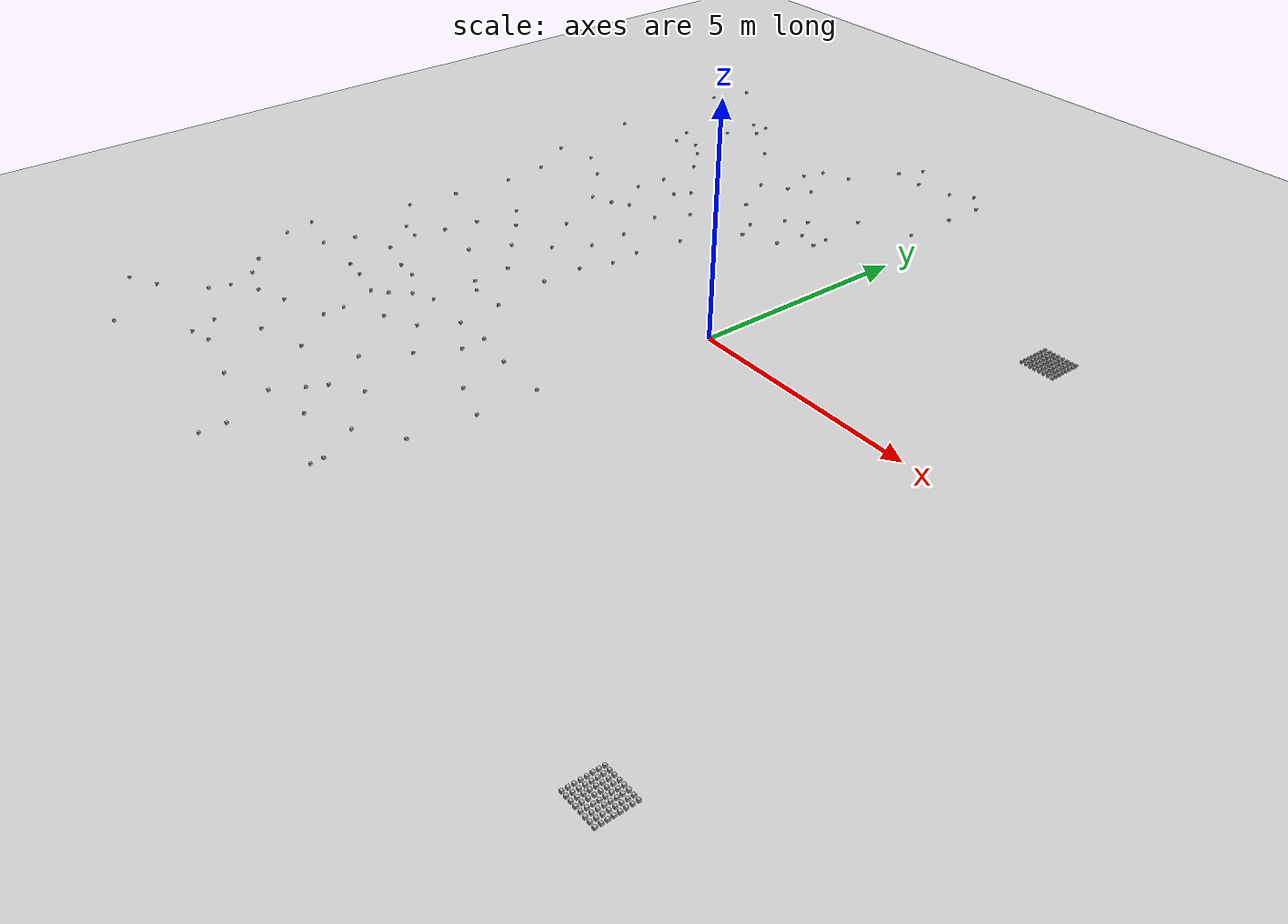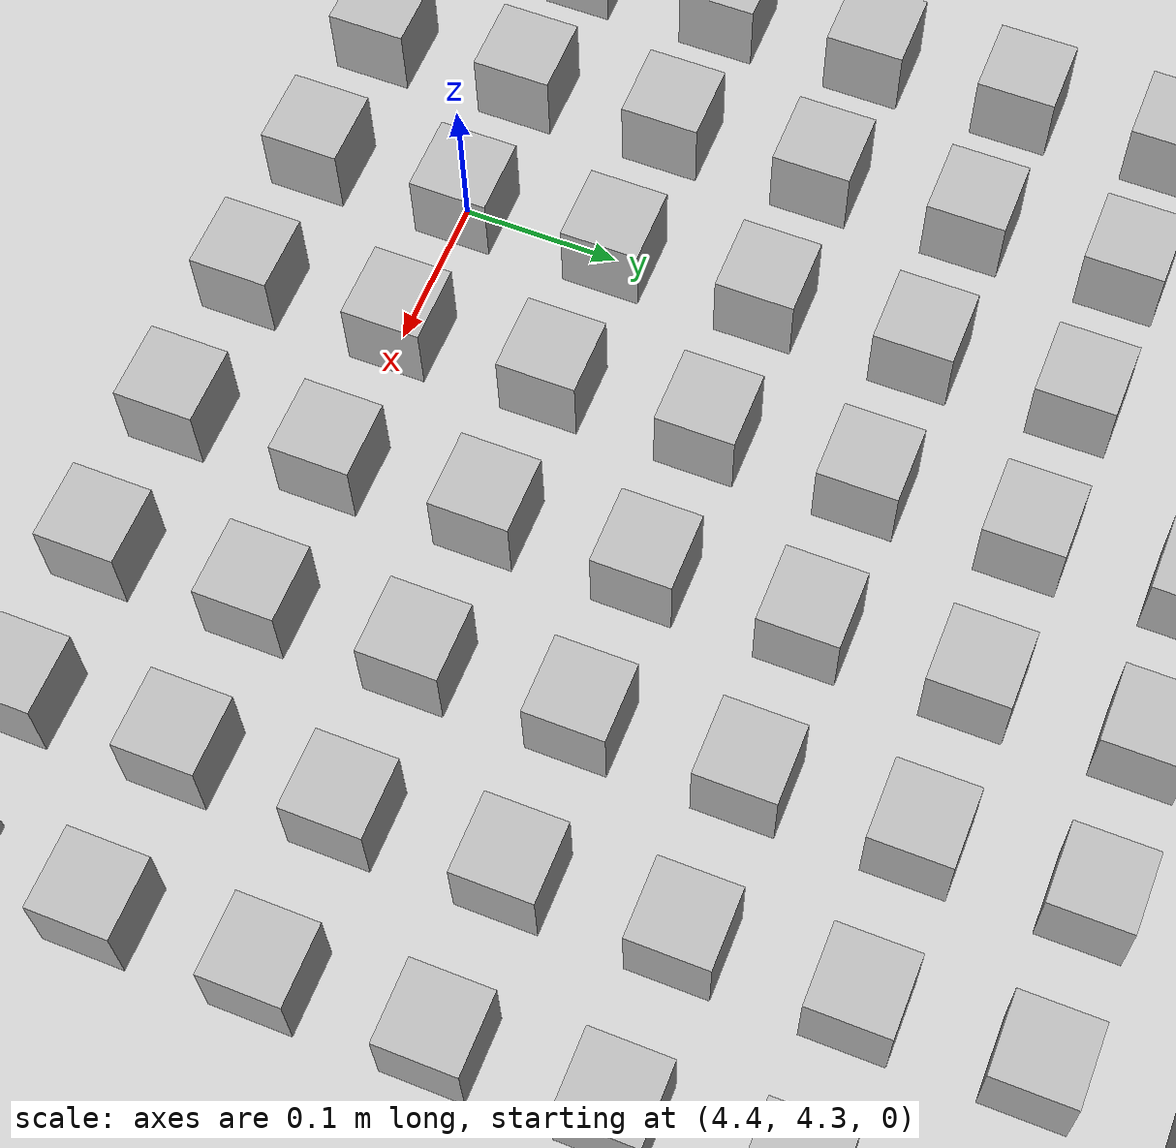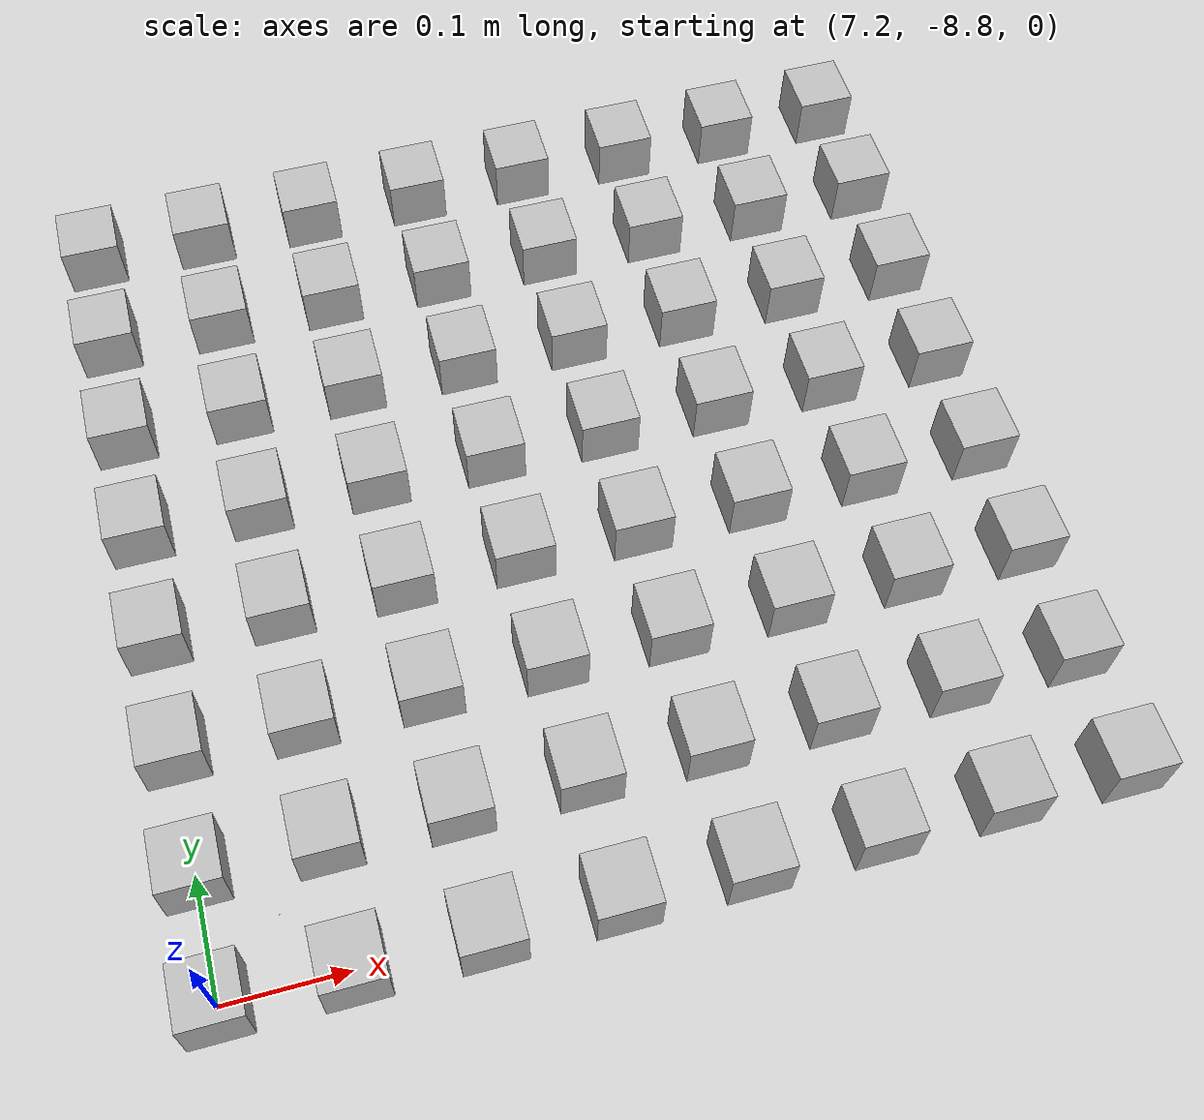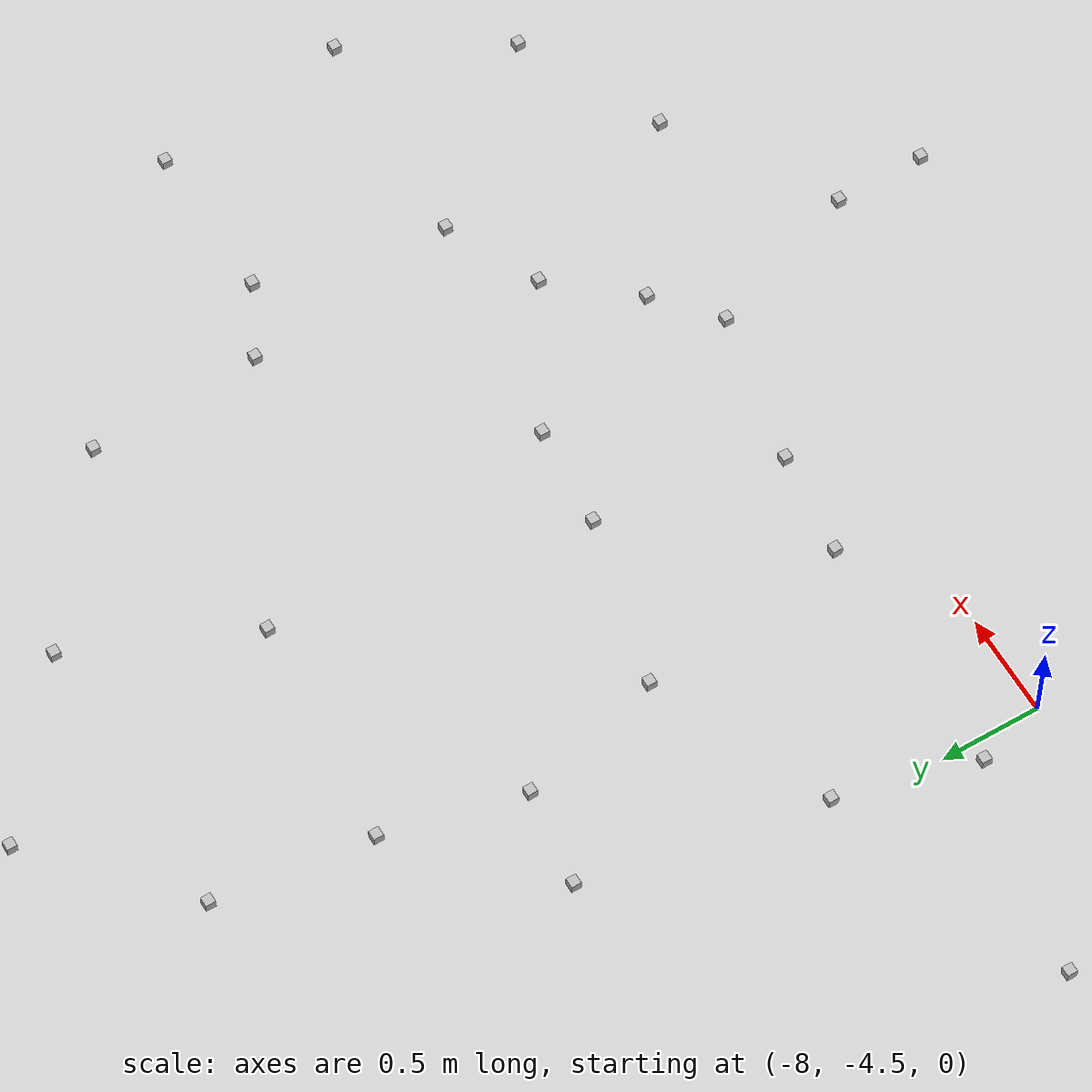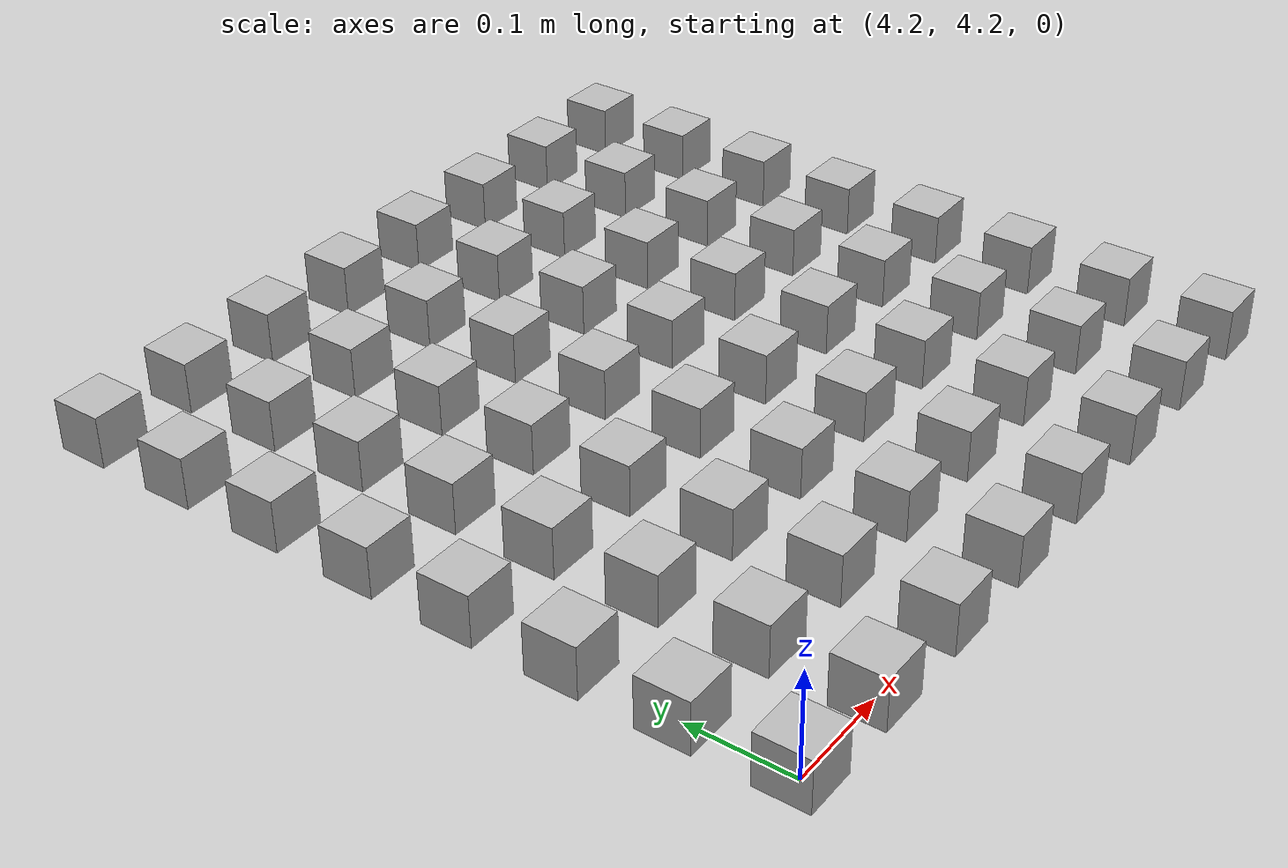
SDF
<sdf version="1.6">
 <world name="default">
  <model name="ground_plane">
   <static>1</static>
   <link name="link">
    <collision name="collision">
     <geometry><plane><normal>0 0 1</normal><size>100 100</size></plane></geometry>
     <surface><friction><ode><mu>100</mu><mu2>50</mu2></ode></friction></surface>
    </collision>
    <visual name="visual">
     <cast_shadows>0</cast_shadows>
     <geometry><plane><normal>0 0 1</normal><size>100 100</size></plane></geometry>
     <material>
      <script><uri>file://media/materials/scripts/gazebo.material</uri><name>Gazebo/Grey</name></script>
     </material>
    </visual>
   </link>
  </model>
  <light name="sun" type="directional">
   <pose>0 0 10 0 -0 0</pose>
   <diffuse>0.8 0.8 0.8 1</diffuse>
   <specular>0.1 0.1 0.1 1</specular>
   <attenuation>
    <range>1000</range>
    <constant>0.9</constant>
    <linear>0.01</linear>
    <quadratic>0.001</quadratic>
   </attenuation>
   <direction>-0.5 0.5 -1</direction>
  </light>
  <plugin name="SetupWorld" filename="libgazebo_plugins.so"/>
  <gravity>0 0 -9.8</gravity>
  <magnetic_field>6e-06 2.3e-05 -4.2e-05</magnetic_field>
  <atmosphere type="adiabatic"/>
  <physics name="default_physics" default="0" type="ode">
   <max_step_size>0.001</max_step_size>
   <real_time_factor>1</real_time_factor>
   <real_time_update_rate>1000</real_time_update_rate>
  </physics>
  <scene><ambient>0.4 0.4 0.4 1</ambient><background>0.7 0.7 0.7 1</background><shadows>1</shadows></scene>
  <spherical_coordinates>
   <surface_model>EARTH_WGS84</surface_model>
   <latitude_deg>0</latitude_deg>
   <longitude_deg>0</longitude_deg>
   <elevation>0</elevation>
   <heading_deg>0</heading_deg>
  </spherical_coordinates>
  <model name="at0">
   <static>0</static>
   <link name="link">
    <inertial>
     <mass>0.01</mass>
     <inertia><ixx>4e-05</ixx><ixy>0</ixy><ixz>0</ixz><iyy>4e-05</iyy><iyz>0</iyz><izz>4e-05</izz></inertia>
    </inertial>
    <visual name="visual">
     <geometry><box><size>0.05 0.05 0.05</size></box></geometry>
     <material>
      <script>
       <uri>model://at0/materials/scripts</uri>
       <uri>model://at0/materials/textures</uri>
       <name>at0/Diffuse</name>
      </script>
     </material>
    </visual>
    <collision name="collision">
     <geometry><box><size>0.05 0.05 0.05</size></box></geometry>
     <surface><friction><ode><mu>0.8</mu><mu2>0.7</mu2></ode></friction></surface>
    </collision>
   </link>
   <pose>-6.39553 1.9856 0.025 0 -0 0</pose>
  </model>
  <model name="at1">
   <static>0</static>
   <link name="link">
    <inertial>
     <mass>0.01</mass>
     <inertia><ixx>4e-05</ixx><ixy>0</ixy><ixz>0</ixz><iyy>4e-05</iyy><iyz>0</iyz><izz>4e-05</izz></inertia>
    </inertial>
    <visual name="visual">
     <geometry><box><size>0.05 0.05 0.05</size></box></geometry>
     <material>
      <script>
       <uri>model://at0/materials/scripts</uri>
       <uri>model://at0/materials/textures</uri>
       <name>at0/Diffuse</name>
      </script>
     </material>
    </visual>
    <collision name="collision">
     <geometry><box><size>0.05 0.05 0.05</size></box></geometry>
     <surface><friction><ode><mu>0.8</mu><mu2>0.7</mu2></ode></friction></surface>
    </collision>
   </link>
   <pose>-5.32227 -5.61067 0.025 0 -0 0</pose>
  </model>
  <model name="at2">
   <static>0</static>
   <link name="link">
    <inertial>
     <mass>0.01</mass>
     <inertia><ixx>4e-05</ixx><ixy>0</ixy><ixz>0</ixz><iyy>4e-05</iyy><iyz>0</iyz><izz>4e-05</izz></inertia>
    </inertial>
    <visual name="visual">
     <geometry><box><size>0.05 0.05 0.05</size></box></geometry>
     <material>
      <script>
       <uri>model://at0/materials/scripts</uri>
       <uri>model://at0/materials/textures</uri>
       <name>at0/Diffuse</name>
      </script>
     </material>
    </visual>
    <collision name="collision">
     <geometry><box><size>0.05 0.05 0.05</size></box></geometry>
     <surface><friction><ode><mu>0.8</mu><mu2>0.7</mu2></ode></friction></surface>
    </collision>
   </link>
   <pose>-7.73897 5.68603 0.025 0 -0 0</pose>
  </model>
  <model name="at3">
   <static>0</static>
   <link name="link">
    <inertial>
     <mass>0.01</mass>
     <inertia><ixx>4e-05</ixx><ixy>0</ixy><ixz>0</ixz><iyy>4e-05</iyy><iyz>0</iyz><izz>4e-05</izz></inertia>
    </inertial>
    <visual name="visual">
     <geometry><box><size>0.05 0.05 0.05</size></box></geometry>
     <material>
      <script>
       <uri>model://at0/materials/scripts</uri>
       <uri>model://at0/materials/textures</uri>
       <name>at0/Diffuse</name>
      </script>
     </material>
    </visual>
    <collision name="collision">
     <geometry><box><size>0.05 0.05 0.05</size></box></geometry>
     <surface><friction><ode><mu>0.8</mu><mu2>0.7</mu2></ode></friction></surface>
    </collision>
   </link>
   <pose>-8.50192 -7.82447 0.025 0 -0 0</pose>
  </model>
  <model name="at4">
   <static>0</static>
   <link name="link">
    <inertial>
     <mass>0.01</mass>
     <inertia><ixx>4e-05</ixx><ixy>0</ixy><ixz>0</ixz><iyy>4e-05</iyy><iyz>0</iyz><izz>4e-05</izz></inertia>
    </inertial>
    <visual name="visual">
     <geometry><box><size>0.05 0.05 0.05</size></box></geometry>
     <material>
      <script>
       <uri>model://at0/materials/scripts</uri>
       <uri>model://at0/materials/textures</uri>
       <name>at0/Diffuse</name>
      </script>
     </material>
    </visual>
    <collision name="collision">
     <geometry><box><size>0.05 0.05 0.05</size></box></geometry>
     <surface><friction><ode><mu>0.8</mu><mu2>0.7</mu2></ode></friction></surface>
    </collision>
   </link>
   <pose>-2.55138 -4.08518 0.025 0 -0 0</pose>
  </model>
  <model name="at5">
   <static>0</static>
   <link name="link">
    <inertial>
     <mass>0.01</mass>
     <inertia><ixx>4e-05</ixx><ixy>0</ixy><ixz>0</ixz><iyy>4e-05</iyy><iyz>0</iyz><izz>4e-05</izz></inertia>
    </inertial>
    <visual name="visual">
     <geometry><box><size>0.05 0.05 0.05</size></box></geometry>
     <material>
      <script>
       <uri>model://at0/materials/scripts</uri>
       <uri>model://at0/materials/textures</uri>
       <name>at0/Diffuse</name>
      </script>
     </material>
    </visual>
    <collision name="collision">
     <geometry><box><size>0.05 0.05 0.05</size></box></geometry>
     <surface><friction><ode><mu>0.8</mu><mu2>0.7</mu2></ode></friction></surface>
    </collision>
   </link>
   <pose>-9.37978 5.29677 0.025 0 -0 0</pose>
  </model>
  <model name="at6">
   <static>0</static>
   <link name="link">
    <inertial>
     <mass>0.01</mass>
     <inertia><ixx>4e-05</ixx><ixy>0</ixy><ixz>0</ixz><iyy>4e-05</iyy><iyz>0</iyz><izz>4e-05</izz></inertia>
    </inertial>
    <visual name="visual">
     <geometry><box><size>0.05 0.05 0.05</size></box></geometry>
     <material>
      <script>
       <uri>model://at0/materials/scripts</uri>
       <uri>model://at0/materials/textures</uri>
       <name>at0/Diffuse</name>
      </script>
     </material>
    </visual>
    <collision name="collision">
     <geometry><box><size>0.05 0.05 0.05</size></box></geometry>
     <surface><friction><ode><mu>0.8</mu><mu2>0.7</mu2></ode></friction></surface>
    </collision>
   </link>
   <pose>-2.11763 3.83461 0.025 0 -0 0</pose>
  </model>
  <model name="at7">
   <static>0</static>
   <link name="link">
    <inertial>
     <mass>0.01</mass>
     <inertia><ixx>4e-05</ixx><ixy>0</ixy><ixz>0</ixz><iyy>4e-05</iyy><iyz>0</iyz><izz>4e-05</izz></inertia>
    </inertial>
    <visual name="visual">
     <geometry><box><size>0.05 0.05 0.05</size></box></geometry>
     <material>
      <script>
       <uri>model://at0/materials/scripts</uri>
       <uri>model://at0/materials/textures</uri>
       <name>at0/Diffuse</name>
      </script>
     </material>
    </visual>
    <collision name="collision">
     <geometry><box><size>0.05 0.05 0.05</size></box></geometry>
     <surface><friction><ode><mu>0.8</mu><mu2>0.7</mu2></ode></friction></surface>
    </collision>
   </link>
   <pose>-4.53461 -4.67095 0.025 0 -0 0</pose>
  </model>
  <model name="at8">
   <static>0</static>
   <link name="link">
    <inertial>
     <mass>0.01</mass>
     <inertia><ixx>4e-05</ixx><ixy>0</ixy><ixz>0</ixz><iyy>4e-05</iyy><iyz>0</iyz><izz>4e-05</izz></inertia>
    </inertial>
    <visual name="visual">
     <geometry><box><size>0.05 0.05 0.05</size></box></geometry>
     <material>
      <script>
       <uri>model://at0/materials/scripts</uri>
       <uri>model://at0/materials/textures</uri>
       <name>at0/Diffuse</name>
      </script>
     </material>
    </visual>
    <collision name="collision">
     <geometry><box><size>0.05 0.05 0.05</size></box></geometry>
     <surface><friction><ode><mu>0.8</mu><mu2>0.7</mu2></ode></friction></surface>
    </collision>
   </link>
   <pose>-0.502806 -5.07438 0.025 0 -0 0</pose>
  </model>
  <model name="at9">
   <static>0</static>
   <link name="link">
    <inertial>
     <mass>0.01</mass>
     <inertia><ixx>4e-05</ixx><ixy>0</ixy><ixz>0</ixz><iyy>4e-05</iyy><iyz>0</iyz><izz>4e-05</izz></inertia>
    </inertial>
    <visual name="visual">
     <geometry><box><size>0.05 0.05 0.05</size></box></geometry>
     <material>
      <script>
       <uri>model://at0/materials/scripts</uri>
       <uri>model://at0/materials/textures</uri>
       <name>at0/Diffuse</name>
      </script>
     </material>
    </visual>
    <collision name="collision">
     <geometry><box><size>0.05 0.05 0.05</size></box></geometry>
     <surface><friction><ode><mu>0.8</mu><mu2>0.7</mu2></ode></friction></surface>
    </collision>
   </link>
   <pose>-5.78522 -7.8777 0.025 0 -0 0</pose>
  </model>
  <model name="at10">
   <static>0</static>
   <link name="link">
    <inertial>
     <mass>0.01</mass>
     <inertia><ixx>4e-05</ixx><ixy>0</ixy><ixz>0</ixz><iyy>4e-05</iyy><iyz>0</iyz><izz>4e-05</izz></inertia>
    </inertial>
    <visual name="visual">
     <geometry><box><size>0.05 0.05 0.05</size></box></geometry>
     <material>
      <script>
       <uri>model://at0/materials/scripts</uri>
       <uri>model://at0/materials/textures</uri>
       <name>at0/Diffuse</name>
      </script>
     </material>
    </visual>
    <collision name="collision">
     <geometry><box><size>0.05 0.05 0.05</size></box></geometry>
     <surface><friction><ode><mu>0.8</mu><mu2>0.7</mu2></ode></friction></surface>
    </collision>
   </link>
   <pose>-7.33637 2.84081 0.025 0 -0 0</pose>
  </model>
  <model name="at11">
   <static>0</static>
   <link name="link">
    <inertial>
     <mass>0.01</mass>
     <inertia><ixx>4e-05</ixx><ixy>0</ixy><ixz>0</ixz><iyy>4e-05</iyy><iyz>0</iyz><izz>4e-05</izz></inertia>
    </inertial>
    <visual name="visual">
     <geometry><box><size>0.05 0.05 0.05</size></box></geometry>
     <material>
      <script>
       <uri>model://at0/materials/scripts</uri>
       <uri>model://at0/materials/textures</uri>
       <name>at0/Diffuse</name>
      </script>
     </material>
    </visual>
    <collision name="collision">
     <geometry><box><size>0.05 0.05 0.05</size></box></geometry>
     <surface><friction><ode><mu>0.8</mu><mu2>0.7</mu2></ode></friction></surface>
    </collision>
   </link>
   <pose>-7.56151 -6.59729 0.025 0 -0 0</pose>
  </model>
  <model name="at12">
   <static>0</static>
   <link name="link">
    <inertial>
     <mass>0.01</mass>
     <inertia><ixx>4e-05</ixx><ixy>0</ixy><ixz>0</ixz><iyy>4e-05</iyy><iyz>0</iyz><izz>4e-05</izz></inertia>
    </inertial>
    <visual name="visual">
     <geometry><box><size>0.05 0.05 0.05</size></box></geometry>
     <material>
      <script>
       <uri>model://at0/materials/scripts</uri>
       <uri>model://at0/materials/textures</uri>
       <name>at0/Diffuse</name>
      </script>
     </material>
    </visual>
    <collision name="collision">
     <geometry><box><size>0.05 0.05 0.05</size></box></geometry>
     <surface><friction><ode><mu>0.8</mu><mu2>0.7</mu2></ode></friction></surface>
    </collision>
   </link>
   <pose>-0.594201 8.66153 0.025 0 -0 0</pose>
  </model>
  <model name="at13">
   <static>0</static>
   <link name="link">
    <inertial>
     <mass>0.01</mass>
     <inertia><ixx>4e-05</ixx><ixy>0</ixy><ixz>0</ixz><iyy>4e-05</iyy><iyz>0</iyz><izz>4e-05</izz></inertia>
    </inertial>
    <visual name="visual">
     <geometry><box><size>0.05 0.05 0.05</size></box></geometry>
     <material>
      <script>
       <uri>model://at0/materials/scripts</uri>
       <uri>model://at0/materials/textures</uri>
       <name>at0/Diffuse</name>
      </script>
     </material>
    </visual>
    <collision name="collision">
     <geometry><box><size>0.05 0.05 0.05</size></box></geometry>
     <surface><friction><ode><mu>0.8</mu><mu2>0.7</mu2></ode></friction></surface>
    </collision>
   </link>
   <pose>-8.09922 -4.1539 0.025 0 -0 0</pose>
  </model>
  <model name="at14">
   <static>0</static>
   <link name="link">
    <inertial>
     <mass>0.01</mass>
     <inertia><ixx>4e-05</ixx><ixy>0</ixy><ixz>0</ixz><iyy>4e-05</iyy><iyz>0</iyz><izz>4e-05</izz></inertia>
    </inertial>
    <visual name="visual">
     <geometry><box><size>0.05 0.05 0.05</size></box></geometry>
     <material>
      <script>
       <uri>model://at0/materials/scripts</uri>
       <uri>model://at0/materials/textures</uri>
       <name>at0/Diffuse</name>
      </script>
     </material>
    </visual>
    <collision name="collision">
     <geometry><box><size>0.05 0.05 0.05</size></box></geometry>
     <surface><friction><ode><mu>0.8</mu><mu2>0.7</mu2></ode></friction></surface>
    </collision>
   </link>
   <pose>-5.63322 0.676383 0.025 0 -0 0</pose>
  </model>
  <model name="at15">
   <static>0</static>
   <link name="link">
    <inertial>
     <mass>0.01</mass>
     <inertia><ixx>4e-05</ixx><ixy>0</ixy><ixz>0</ixz><iyy>4e-05</iyy><iyz>0</iyz><izz>4e-05</izz></inertia>
    </inertial>
    <visual name="visual">
     <geometry><box><size>0.05 0.05 0.05</size></box></geometry>
     <material>
      <script>
       <uri>model://at0/materials/scripts</uri>
       <uri>model://at0/materials/textures</uri>
       <name>at0/Diffuse</name>
      </script>
     </material>
    </visual>
    <collision name="collision">
     <geometry><box><size>0.05 0.05 0.05</size></box></geometry>
     <surface><friction><ode><mu>0.8</mu><mu2>0.7</mu2></ode></friction></surface>
    </collision>
   </link>
   <pose>-3.53179 6.27969 0.025 0 -0 0</pose>
  </model>
  <model name="at16">
   <static>0</static>
   <link name="link">
    <inertial>
     <mass>0.01</mass>
     <inertia><ixx>4e-05</ixx><ixy>0</ixy><ixz>0</ixz><iyy>4e-05</iyy><iyz>0</iyz><izz>4e-05</izz></inertia>
    </inertial>
    <visual name="visual">
     <geometry><box><size>0.05 0.05 0.05</size></box></geometry>
     <material>
      <script>
       <uri>model://at0/materials/scripts</uri>
       <uri>model://at0/materials/textures</uri>
       <name>at0/Diffuse</name>
      </script>
     </material>
    </visual>
    <collision name="collision">
     <geometry><box><size>0.05 0.05 0.05</size></box></geometry>
     <surface><friction><ode><mu>0.8</mu><mu2>0.7</mu2></ode></friction></surface>
    </collision>
   </link>
   <pose>-6.18898 3.18966 0.025 0 -0 0</pose>
  </model>
  <model name="at17">
   <static>0</static>
   <link name="link">
    <inertial>
     <mass>0.01</mass>
     <inertia><ixx>4e-05</ixx><ixy>0</ixy><ixz>0</ixz><iyy>4e-05</iyy><iyz>0</iyz><izz>4e-05</izz></inertia>
    </inertial>
    <visual name="visual">
     <geometry><box><size>0.05 0.05 0.05</size></box></geometry>
     <material>
      <script>
       <uri>model://at0/materials/scripts</uri>
       <uri>model://at0/materials/textures</uri>
       <name>at0/Diffuse</name>
      </script>
     </material>
    </visual>
    <collision name="collision">
     <geometry><box><size>0.05 0.05 0.05</size></box></geometry>
     <surface><friction><ode><mu>0.8</mu><mu2>0.7</mu2></ode></friction></surface>
    </collision>
   </link>
   <pose>-8.5816 -1.66644 0.025 0 -0 0</pose>
  </model>
  <model name="at18">
   <static>0</static>
   <link name="link">
    <inertial>
     <mass>0.01</mass>
     <inertia><ixx>4e-05</ixx><ixy>0</ixy><ixz>0</ixz><iyy>4e-05</iyy><iyz>0</iyz><izz>4e-05</izz></inertia>
    </inertial>
    <visual name="visual">
     <geometry><box><size>0.05 0.05 0.05</size></box></geometry>
     <material>
      <script>
       <uri>model://at0/materials/scripts</uri>
       <uri>model://at0/materials/textures</uri>
       <name>at0/Diffuse</name>
      </script>
     </material>
    </visual>
    <collision name="collision">
     <geometry><box><size>0.05 0.05 0.05</size></box></geometry>
     <surface><friction><ode><mu>0.8</mu><mu2>0.7</mu2></ode></friction></surface>
    </collision>
   </link>
   <pose>-2.95732 -6.74311 0.025 0 -0 0</pose>
  </model>
  <model name="at19">
   <static>0</static>
   <link name="link">
    <inertial>
     <mass>0.01</mass>
     <inertia><ixx>4e-05</ixx><ixy>0</ixy><ixz>0</ixz><iyy>4e-05</iyy><iyz>0</iyz><izz>4e-05</izz></inertia>
    </inertial>
    <visual name="visual">
     <geometry><box><size>0.05 0.05 0.05</size></box></geometry>
     <material>
      <script>
       <uri>model://at0/materials/scripts</uri>
       <uri>model://at0/materials/textures</uri>
       <name>at0/Diffuse</name>
      </script>
     </material>
    </visual>
    <collision name="collision">
     <geometry><box><size>0.05 0.05 0.05</size></box></geometry>
     <surface><friction><ode><mu>0.8</mu><mu2>0.7</mu2></ode></friction></surface>
    </collision>
   </link>
   <pose>-3.46331 -7.72627 0.025 0 -0 0</pose>
  </model>
  <model name="at20">
   <static>0</static>
   <link name="link">
    <inertial>
     <mass>0.01</mass>
     <inertia><ixx>4e-05</ixx><ixy>0</ixy><ixz>0</ixz><iyy>4e-05</iyy><iyz>0</iyz><izz>4e-05</izz></inertia>
    </inertial>
    <visual name="visual">
     <geometry><box><size>0.05 0.05 0.05</size></box></geometry>
     <material>
      <script>
       <uri>model://at0/materials/scripts</uri>
       <uri>model://at0/materials/textures</uri>
       <name>at0/Diffuse</name>
      </script>
     </material>
    </visual>
    <collision name="collision">
     <geometry><box><size>0.05 0.05 0.05</size></box></geometry>
     <surface><friction><ode><mu>0.8</mu><mu2>0.7</mu2></ode></friction></surface>
    </collision>
   </link>
   <pose>-3.94673 4.59401 0.025 0 -0 0</pose>
  </model>
  <model name="at21">
   <static>0</static>
   <link name="link">
    <inertial>
     <mass>0.01</mass>
     <inertia><ixx>4e-05</ixx><ixy>0</ixy><ixz>0</ixz><iyy>4e-05</iyy><iyz>0</iyz><izz>4e-05</izz></inertia>
    </inertial>
    <visual name="visual">
     <geometry><box><size>0.05 0.05 0.05</size></box></geometry>
     <material>
      <script>
       <uri>model://at0/materials/scripts</uri>
       <uri>model://at0/materials/textures</uri>
       <name>at0/Diffuse</name>
      </script>
     </material>
    </visual>
    <collision name="collision">
     <geometry><box><size>0.05 0.05 0.05</size></box></geometry>
     <surface><friction><ode><mu>0.8</mu><mu2>0.7</mu2></ode></friction></surface>
    </collision>
   </link>
   <pose>-1.67535 -3.70538 0.025 0 -0 0</pose>
  </model>
  <model name="at22">
   <static>0</static>
   <link name="link">
    <inertial>
     <mass>0.01</mass>
     <inertia><ixx>4e-05</ixx><ixy>0</ixy><ixz>0</ixz><iyy>4e-05</iyy><iyz>0</iyz><izz>4e-05</izz></inertia>
    </inertial>
    <visual name="visual">
     <geometry><box><size>0.05 0.05 0.05</size></box></geometry>
     <material>
      <script>
       <uri>model://at0/materials/scripts</uri>
       <uri>model://at0/materials/textures</uri>
       <name>at0/Diffuse</name>
      </script>
     </material>
    </visual>
    <collision name="collision">
     <geometry><box><size>0.05 0.05 0.05</size></box></geometry>
     <surface><friction><ode><mu>0.8</mu><mu2>0.7</mu2></ode></friction></surface>
    </collision>
   </link>
   <pose>-5.37684 3.61979 0.025 0 -0 0</pose>
  </model>
  <model name="at23">
   <static>0</static>
   <link name="link">
    <inertial>
     <mass>0.01</mass>
     <inertia><ixx>4e-05</ixx><ixy>0</ixy><ixz>0</ixz><iyy>4e-05</iyy><iyz>0</iyz><izz>4e-05</izz></inertia>
    </inertial>
    <visual name="visual">
     <geometry><box><size>0.05 0.05 0.05</size></box></geometry>
     <material>
      <script>
       <uri>model://at0/materials/scripts</uri>
       <uri>model://at0/materials/textures</uri>
       <name>at0/Diffuse</name>
      </script>
     </material>
    </visual>
    <collision name="collision">
     <geometry><box><size>0.05 0.05 0.05</size></box></geometry>
     <surface><friction><ode><mu>0.8</mu><mu2>0.7</mu2></ode></friction></surface>
    </collision>
   </link>
   <pose>-5.54676 2.40735 0.025 0 -0 0</pose>
  </model>
  <model name="at24">
   <static>0</static>
   <link name="link">
    <inertial>
     <mass>0.01</mass>
     <inertia><ixx>4e-05</ixx><ixy>0</ixy><ixz>0</ixz><iyy>4e-05</iyy><iyz>0</iyz><izz>4e-05</izz></inertia>
    </inertial>
    <visual name="visual">
     <geometry><box><size>0.05 0.05 0.05</size></box></geometry>
     <material>
      <script>
       <uri>model://at0/materials/scripts</uri>
       <uri>model://at0/materials/textures</uri>
       <name>at0/Diffuse</name>
      </script>
     </material>
    </visual>
    <collision name="collision">
     <geometry><box><size>0.05 0.05 0.05</size></box></geometry>
     <surface><friction><ode><mu>0.8</mu><mu2>0.7</mu2></ode></friction></surface>
    </collision>
   </link>
   <pose>-9.11333 -8.17807 0.025 0 -0 0</pose>
  </model>
  <model name="at25">
   <static>0</static>
   <link name="link">
    <inertial>
     <mass>0.01</mass>
     <inertia><ixx>4e-05</ixx><ixy>0</ixy><ixz>0</ixz><iyy>4e-05</iyy><iyz>0</iyz><izz>4e-05</izz></inertia>
    </inertial>
    <visual name="visual">
     <geometry><box><size>0.05 0.05 0.05</size></box></geometry>
     <material>
      <script>
       <uri>model://at0/materials/scripts</uri>
       <uri>model://at0/materials/textures</uri>
       <name>at0/Diffuse</name>
      </script>
     </material>
    </visual>
    <collision name="collision">
     <geometry><box><size>0.05 0.05 0.05</size></box></geometry>
     <surface><friction><ode><mu>0.8</mu><mu2>0.7</mu2></ode></friction></surface>
    </collision>
   </link>
   <pose>-3.46757 2.19606 0.025 0 -0 0</pose>
  </model>
  <model name="at26">
   <static>0</static>
   <link name="link">
    <inertial>
     <mass>0.01</mass>
     <inertia><ixx>4e-05</ixx><ixy>0</ixy><ixz>0</ixz><iyy>4e-05</iyy><iyz>0</iyz><izz>4e-05</izz></inertia>
    </inertial>
    <visual name="visual">
     <geometry><box><size>0.05 0.05 0.05</size></box></geometry>
     <material>
      <script>
       <uri>model://at0/materials/scripts</uri>
       <uri>model://at0/materials/textures</uri>
       <name>at0/Diffuse</name>
      </script>
     </material>
    </visual>
    <collision name="collision">
     <geometry><box><size>0.05 0.05 0.05</size></box></geometry>
     <surface><friction><ode><mu>0.8</mu><mu2>0.7</mu2></ode></friction></surface>
    </collision>
   </link>
   <pose>-4.69569 2.46913 0.025 0 -0 0</pose>
  </model>
  <model name="at27">
   <static>0</static>
   <link name="link">
    <inertial>
     <mass>0.01</mass>
     <inertia><ixx>4e-05</ixx><ixy>0</ixy><ixz>0</ixz><iyy>4e-05</iyy><iyz>0</iyz><izz>4e-05</izz></inertia>
    </inertial>
    <visual name="visual">
     <geometry><box><size>0.05 0.05 0.05</size></box></geometry>
     <material>
      <script>
       <uri>model://at0/materials/scripts</uri>
       <uri>model://at0/materials/textures</uri>
       <name>at0/Diffuse</name>
      </script>
     </material>
    </visual>
    <collision name="collision">
     <geometry><box><size>0.05 0.05 0.05</size></box></geometry>
     <surface><friction><ode><mu>0.8</mu><mu2>0.7</mu2></ode></friction></surface>
    </collision>
   </link>
   <pose>-1.58838 4.80504 0.025 0 -0 0</pose>
  </model>
  <model name="at28">
   <static>0</static>
   <link name="link">
    <inertial>
     <mass>0.01</mass>
     <inertia><ixx>4e-05</ixx><ixy>0</ixy><ixz>0</ixz><iyy>4e-05</iyy><iyz>0</iyz><izz>4e-05</izz></inertia>
    </inertial>
    <visual name="visual">
     <geometry><box><size>0.05 0.05 0.05</size></box></geometry>
     <material>
      <script>
       <uri>model://at0/materials/scripts</uri>
       <uri>model://at0/materials/textures</uri>
       <name>at0/Diffuse</name>
      </script>
     </material>
    </visual>
    <collision name="collision">
     <geometry><box><size>0.05 0.05 0.05</size></box></geometry>
     <surface><friction><ode><mu>0.8</mu><mu2>0.7</mu2></ode></friction></surface>
    </collision>
   </link>
   <pose>-5.5986 -4.3739 0.025 0 -0 0</pose>
  </model>
  <model name="at29">
   <static>0</static>
   <link name="link">
    <inertial>
     <mass>0.01</mass>
     <inertia><ixx>4e-05</ixx><ixy>0</ixy><ixz>0</ixz><iyy>4e-05</iyy><iyz>0</iyz><izz>4e-05</izz></inertia>
    </inertial>
    <visual name="visual">
     <geometry><box><size>0.05 0.05 0.05</size></box></geometry>
     <material>
      <script>
       <uri>model://at0/materials/scripts</uri>
       <uri>model://at0/materials/textures</uri>
       <name>at0/Diffuse</name>
      </script>
     </material>
    </visual>
    <collision name="collision">
     <geometry><box><size>0.05 0.05 0.05</size></box></geometry>
     <surface><friction><ode><mu>0.8</mu><mu2>0.7</mu2></ode></friction></surface>
    </collision>
   </link>
   <pose>-2.9434 -8.78722 0.025 0 -0 0</pose>
  </model>
  <model name="at30">
   <static>0</static>
   <link name="link">
    <inertial>
     <mass>0.01</mass>
     <inertia><ixx>4e-05</ixx><ixy>0</ixy><ixz>0</ixz><iyy>4e-05</iyy><iyz>0</iyz><izz>4e-05</izz></inertia>
    </inertial>
    <visual name="visual">
     <geometry><box><size>0.05 0.05 0.05</size></box></geometry>
     <material>
      <script>
       <uri>model://at0/materials/scripts</uri>
       <uri>model://at0/materials/textures</uri>
       <name>at0/Diffuse</name>
      </script>
     </material>
    </visual>
    <collision name="collision">
     <geometry><box><size>0.05 0.05 0.05</size></box></geometry>
     <surface><friction><ode><mu>0.8</mu><mu2>0.7</mu2></ode></friction></surface>
    </collision>
   </link>
   <pose>-3.3863 -3.5805 0.025 0 -0 0</pose>
  </model>
  <model name="at31">
   <static>0</static>
   <link name="link">
    <inertial>
     <mass>0.01</mass>
     <inertia><ixx>4e-05</ixx><ixy>0</ixy><ixz>0</ixz><iyy>4e-05</iyy><iyz>0</iyz><izz>4e-05</izz></inertia>
    </inertial>
    <visual name="visual">
     <geometry><box><size>0.05 0.05 0.05</size></box></geometry>
     <material>
      <script>
       <uri>model://at0/materials/scripts</uri>
       <uri>model://at0/materials/textures</uri>
       <name>at0/Diffuse</name>
      </script>
     </material>
    </visual>
    <collision name="collision">
     <geometry><box><size>0.05 0.05 0.05</size></box></geometry>
     <surface><friction><ode><mu>0.8</mu><mu2>0.7</mu2></ode></friction></surface>
    </collision>
   </link>
   <pose>-1.37839 -4.80492 0.025 0 -0 0</pose>
  </model>
  <model name="at32">
   <static>0</static>
   <link name="link">
    <inertial>
     <mass>0.01</mass>
     <inertia><ixx>4e-05</ixx><ixy>0</ixy><ixz>0</ixz><iyy>4e-05</iyy><iyz>0</iyz><izz>4e-05</izz></inertia>
    </inertial>
    <visual name="visual">
     <geometry><box><size>0.05 0.05 0.05</size></box></geometry>
     <material>
      <script>
       <uri>model://at0/materials/scripts</uri>
       <uri>model://at0/materials/textures</uri>
       <name>at0/Diffuse</name>
      </script>
     </material>
    </visual>
    <collision name="collision">
     <geometry><box><size>0.05 0.05 0.05</size></box></geometry>
     <surface><friction><ode><mu>0.8</mu><mu2>0.7</mu2></ode></friction></surface>
    </collision>
   </link>
   <pose>-2.59525 -3.54425 0.025 0 -0 0</pose>
  </model>
  <model name="at33">
   <static>0</static>
   <link name="link">
    <inertial>
     <mass>0.01</mass>
     <inertia><ixx>4e-05</ixx><ixy>0</ixy><ixz>0</ixz><iyy>4e-05</iyy><iyz>0</iyz><izz>4e-05</izz></inertia>
    </inertial>
    <visual name="visual">
     <geometry><box><size>0.05 0.05 0.05</size></box></geometry>
     <material>
      <script>
       <uri>model://at0/materials/scripts</uri>
       <uri>model://at0/materials/textures</uri>
       <name>at0/Diffuse</name>
      </script>
     </material>
    </visual>
    <collision name="collision">
     <geometry><box><size>0.05 0.05 0.05</size></box></geometry>
     <surface><friction><ode><mu>0.8</mu><mu2>0.7</mu2></ode></friction></surface>
    </collision>
   </link>
   <pose>-7.33117 7.04119 0.025 0 -0 0</pose>
  </model>
  <model name="at34">
   <static>0</static>
   <link name="link">
    <inertial>
     <mass>0.01</mass>
     <inertia><ixx>4e-05</ixx><ixy>0</ixy><ixz>0</ixz><iyy>4e-05</iyy><iyz>0</iyz><izz>4e-05</izz></inertia>
    </inertial>
    <visual name="visual">
     <geometry><box><size>0.05 0.05 0.05</size></box></geometry>
     <material>
      <script>
       <uri>model://at0/materials/scripts</uri>
       <uri>model://at0/materials/textures</uri>
       <name>at0/Diffuse</name>
      </script>
     </material>
    </visual>
    <collision name="collision">
     <geometry><box><size>0.05 0.05 0.05</size></box></geometry>
     <surface><friction><ode><mu>0.8</mu><mu2>0.7</mu2></ode></friction></surface>
    </collision>
   </link>
   <pose>-9.35862 8.38372 0.025 0 -0 0</pose>
  </model>
  <model name="at35">
   <static>0</static>
   <link name="link">
    <inertial>
     <mass>0.01</mass>
     <inertia><ixx>4e-05</ixx><ixy>0</ixy><ixz>0</ixz><iyy>4e-05</iyy><iyz>0</iyz><izz>4e-05</izz></inertia>
    </inertial>
    <visual name="visual">
     <geometry><box><size>0.05 0.05 0.05</size></box></geometry>
     <material>
      <script>
       <uri>model://at0/materials/scripts</uri>
       <uri>model://at0/materials/textures</uri>
       <name>at0/Diffuse</name>
      </script>
     </material>
    </visual>
    <collision name="collision">
     <geometry><box><size>0.05 0.05 0.05</size></box></geometry>
     <surface><friction><ode><mu>0.8</mu><mu2>0.7</mu2></ode></friction></surface>
    </collision>
   </link>
   <pose>-6.96615 8.04022 0.025 0 -0 0</pose>
  </model>
  <model name="at36">
   <static>0</static>
   <link name="link">
    <inertial>
     <mass>0.01</mass>
     <inertia><ixx>4e-05</ixx><ixy>0</ixy><ixz>0</ixz><iyy>4e-05</iyy><iyz>0</iyz><izz>4e-05</izz></inertia>
    </inertial>
    <visual name="visual">
     <geometry><box><size>0.05 0.05 0.05</size></box></geometry>
     <material>
      <script>
       <uri>model://at0/materials/scripts</uri>
       <uri>model://at0/materials/textures</uri>
       <name>at0/Diffuse</name>
      </script>
     </material>
    </visual>
    <collision name="collision">
     <geometry><box><size>0.05 0.05 0.05</size></box></geometry>
     <surface><friction><ode><mu>0.8</mu><mu2>0.7</mu2></ode></friction></surface>
    </collision>
   </link>
   <pose>-1.76517 6.009 0.025 0 -0 0</pose>
  </model>
  <model name="at37">
   <static>0</static>
   <link name="link">
    <inertial>
     <mass>0.01</mass>
     <inertia><ixx>4e-05</ixx><ixy>0</ixy><ixz>0</ixz><iyy>4e-05</iyy><iyz>0</iyz><izz>4e-05</izz></inertia>
    </inertial>
    <visual name="visual">
     <geometry><box><size>0.05 0.05 0.05</size></box></geometry>
     <material>
      <script>
       <uri>model://at0/materials/scripts</uri>
       <uri>model://at0/materials/textures</uri>
       <name>at0/Diffuse</name>
      </script>
     </material>
    </visual>
    <collision name="collision">
     <geometry><box><size>0.05 0.05 0.05</size></box></geometry>
     <surface><friction><ode><mu>0.8</mu><mu2>0.7</mu2></ode></friction></surface>
    </collision>
   </link>
   <pose>-7.7649 -6.01027 0.025 0 -0 0</pose>
  </model>
  <model name="at38">
   <static>0</static>
   <link name="link">
    <inertial>
     <mass>0.01</mass>
     <inertia><ixx>4e-05</ixx><ixy>0</ixy><ixz>0</ixz><iyy>4e-05</iyy><iyz>0</iyz><izz>4e-05</izz></inertia>
    </inertial>
    <visual name="visual">
     <geometry><box><size>0.05 0.05 0.05</size></box></geometry>
     <material>
      <script>
       <uri>model://at0/materials/scripts</uri>
       <uri>model://at0/materials/textures</uri>
       <name>at0/Diffuse</name>
      </script>
     </material>
    </visual>
    <collision name="collision">
     <geometry><box><size>0.05 0.05 0.05</size></box></geometry>
     <surface><friction><ode><mu>0.8</mu><mu2>0.7</mu2></ode></friction></surface>
    </collision>
   </link>
   <pose>-4.46938 0.510681 0.025 0 -0 0</pose>
  </model>
  <model name="at39">
   <static>0</static>
   <link name="link">
    <inertial>
     <mass>0.01</mass>
     <inertia><ixx>4e-05</ixx><ixy>0</ixy><ixz>0</ixz><iyy>4e-05</iyy><iyz>0</iyz><izz>4e-05</izz></inertia>
    </inertial>
    <visual name="visual">
     <geometry><box><size>0.05 0.05 0.05</size></box></geometry>
     <material>
      <script>
       <uri>model://at0/materials/scripts</uri>
       <uri>model://at0/materials/textures</uri>
       <name>at0/Diffuse</name>
      </script>
     </material>
    </visual>
    <collision name="collision">
     <geometry><box><size>0.05 0.05 0.05</size></box></geometry>
     <surface><friction><ode><mu>0.8</mu><mu2>0.7</mu2></ode></friction></surface>
    </collision>
   </link>
   <pose>-3.52288 7.52677 0.025 0 -0 0</pose>
  </model>
  <model name="at40">
   <static>0</static>
   <link name="link">
    <inertial>
     <mass>0.01</mass>
     <inertia><ixx>4e-05</ixx><ixy>0</ixy><ixz>0</ixz><iyy>4e-05</iyy><iyz>0</iyz><izz>4e-05</izz></inertia>
    </inertial>
    <visual name="visual">
     <geometry><box><size>0.05 0.05 0.05</size></box></geometry>
     <material>
      <script>
       <uri>model://at0/materials/scripts</uri>
       <uri>model://at0/materials/textures</uri>
       <name>at0/Diffuse</name>
      </script>
     </material>
    </visual>
    <collision name="collision">
     <geometry><box><size>0.05 0.05 0.05</size></box></geometry>
     <surface><friction><ode><mu>0.8</mu><mu2>0.7</mu2></ode></friction></surface>
    </collision>
   </link>
   <pose>-0.51663 -3.74511 0.025 0 -0 0</pose>
  </model>
  <model name="at41">
   <static>0</static>
   <link name="link">
    <inertial>
     <mass>0.01</mass>
     <inertia><ixx>4e-05</ixx><ixy>0</ixy><ixz>0</ixz><iyy>4e-05</iyy><iyz>0</iyz><izz>4e-05</izz></inertia>
    </inertial>
    <visual name="visual">
     <geometry><box><size>0.05 0.05 0.05</size></box></geometry>
     <material>
      <script>
       <uri>model://at0/materials/scripts</uri>
       <uri>model://at0/materials/textures</uri>
       <name>at0/Diffuse</name>
      </script>
     </material>
    </visual>
    <collision name="collision">
     <geometry><box><size>0.05 0.05 0.05</size></box></geometry>
     <surface><friction><ode><mu>0.8</mu><mu2>0.7</mu2></ode></friction></surface>
    </collision>
   </link>
   <pose>-1.44706 -7.09914 0.025 0 -0 0</pose>
  </model>
  <model name="at42">
   <static>0</static>
   <link name="link">
    <inertial>
     <mass>0.01</mass>
     <inertia><ixx>4e-05</ixx><ixy>0</ixy><ixz>0</ixz><iyy>4e-05</iyy><iyz>0</iyz><izz>4e-05</izz></inertia>
    </inertial>
    <visual name="visual">
     <geometry><box><size>0.05 0.05 0.05</size></box></geometry>
     <material>
      <script>
       <uri>model://at0/materials/scripts</uri>
       <uri>model://at0/materials/textures</uri>
       <name>at0/Diffuse</name>
      </script>
     </material>
    </visual>
    <collision name="collision">
     <geometry><box><size>0.05 0.05 0.05</size></box></geometry>
     <surface><friction><ode><mu>0.8</mu><mu2>0.7</mu2></ode></friction></surface>
    </collision>
   </link>
   <pose>-4.65881 -2.42351 0.025 0 -0 0</pose>
  </model>
  <model name="at43">
   <static>0</static>
   <link name="link">
    <inertial>
     <mass>0.01</mass>
     <inertia><ixx>4e-05</ixx><ixy>0</ixy><ixz>0</ixz><iyy>4e-05</iyy><iyz>0</iyz><izz>4e-05</izz></inertia>
    </inertial>
    <visual name="visual">
     <geometry><box><size>0.05 0.05 0.05</size></box></geometry>
     <material>
      <script>
       <uri>model://at0/materials/scripts</uri>
       <uri>model://at0/materials/textures</uri>
       <name>at0/Diffuse</name>
      </script>
     </material>
    </visual>
    <collision name="collision">
     <geometry><box><size>0.05 0.05 0.05</size></box></geometry>
     <surface><friction><ode><mu>0.8</mu><mu2>0.7</mu2></ode></friction></surface>
    </collision>
   </link>
   <pose>-6.26488 -7.99708 0.025 0 -0 0</pose>
  </model>
  <model name="at44">
   <static>0</static>
   <link name="link">
    <inertial>
     <mass>0.01</mass>
     <inertia><ixx>4e-05</ixx><ixy>0</ixy><ixz>0</ixz><iyy>4e-05</iyy><iyz>0</iyz><izz>4e-05</izz></inertia>
    </inertial>
    <visual name="visual">
     <geometry><box><size>0.05 0.05 0.05</size></box></geometry>
     <material>
      <script>
       <uri>model://at0/materials/scripts</uri>
       <uri>model://at0/materials/textures</uri>
       <name>at0/Diffuse</name>
      </script>
     </material>
    </visual>
    <collision name="collision">
     <geometry><box><size>0.05 0.05 0.05</size></box></geometry>
     <surface><friction><ode><mu>0.8</mu><mu2>0.7</mu2></ode></friction></surface>
    </collision>
   </link>
   <pose>-7.0175 -6.22351 0.025 0 -0 0</pose>
  </model>
  <model name="at45">
   <static>0</static>
   <link name="link">
    <inertial>
     <mass>0.01</mass>
     <inertia><ixx>4e-05</ixx><ixy>0</ixy><ixz>0</ixz><iyy>4e-05</iyy><iyz>0</iyz><izz>4e-05</izz></inertia>
    </inertial>
    <visual name="visual">
     <geometry><box><size>0.05 0.05 0.05</size></box></geometry>
     <material>
      <script>
       <uri>model://at0/materials/scripts</uri>
       <uri>model://at0/materials/textures</uri>
       <name>at0/Diffuse</name>
      </script>
     </material>
    </visual>
    <collision name="collision">
     <geometry><box><size>0.05 0.05 0.05</size></box></geometry>
     <surface><friction><ode><mu>0.8</mu><mu2>0.7</mu2></ode></friction></surface>
    </collision>
   </link>
   <pose>-9.01336 -4.58365 0.025 0 -0 0</pose>
  </model>
  <model name="at46">
   <static>0</static>
   <link name="link">
    <inertial>
     <mass>0.01</mass>
     <inertia><ixx>4e-05</ixx><ixy>0</ixy><ixz>0</ixz><iyy>4e-05</iyy><iyz>0</iyz><izz>4e-05</izz></inertia>
    </inertial>
    <visual name="visual">
     <geometry><box><size>0.05 0.05 0.05</size></box></geometry>
     <material>
      <script>
       <uri>model://at0/materials/scripts</uri>
       <uri>model://at0/materials/textures</uri>
       <name>at0/Diffuse</name>
      </script>
     </material>
    </visual>
    <collision name="collision">
     <geometry><box><size>0.05 0.05 0.05</size></box></geometry>
     <surface><friction><ode><mu>0.8</mu><mu2>0.7</mu2></ode></friction></surface>
    </collision>
   </link>
   <pose>-7.58329 -9.0916 0.025 0 -0 0</pose>
  </model>
  <model name="at47">
   <static>0</static>
   <link name="link">
    <inertial>
     <mass>0.01</mass>
     <inertia><ixx>4e-05</ixx><ixy>0</ixy><ixz>0</ixz><iyy>4e-05</iyy><iyz>0</iyz><izz>4e-05</izz></inertia>
    </inertial>
    <visual name="visual">
     <geometry><box><size>0.05 0.05 0.05</size></box></geometry>
     <material>
      <script>
       <uri>model://at0/materials/scripts</uri>
       <uri>model://at0/materials/textures</uri>
       <name>at0/Diffuse</name>
      </script>
     </material>
    </visual>
    <collision name="collision">
     <geometry><box><size>0.05 0.05 0.05</size></box></geometry>
     <surface><friction><ode><mu>0.8</mu><mu2>0.7</mu2></ode></friction></surface>
    </collision>
   </link>
   <pose>-4.90591 -0.256277 0.025 0 -0 0</pose>
  </model>
  <model name="at48">
   <static>0</static>
   <link name="link">
    <inertial>
     <mass>0.01</mass>
     <inertia><ixx>4e-05</ixx><ixy>0</ixy><ixz>0</ixz><iyy>4e-05</iyy><iyz>0</iyz><izz>4e-05</izz></inertia>
    </inertial>
    <visual name="visual">
     <geometry><box><size>0.05 0.05 0.05</size></box></geometry>
     <material>
      <script>
       <uri>model://at0/materials/scripts</uri>
       <uri>model://at0/materials/textures</uri>
       <name>at0/Diffuse</name>
      </script>
     </material>
    </visual>
    <collision name="collision">
     <geometry><box><size>0.05 0.05 0.05</size></box></geometry>
     <surface><friction><ode><mu>0.8</mu><mu2>0.7</mu2></ode></friction></surface>
    </collision>
   </link>
   <pose>-7.31224 7.9525 0.025 0 -0 0</pose>
  </model>
  <model name="at49">
   <static>0</static>
   <link name="link">
    <inertial>
     <mass>0.01</mass>
     <inertia><ixx>4e-05</ixx><ixy>0</ixy><ixz>0</ixz><iyy>4e-05</iyy><iyz>0</iyz><izz>4e-05</izz></inertia>
    </inertial>
    <visual name="visual">
     <geometry><box><size>0.05 0.05 0.05</size></box></geometry>
     <material>
      <script>
       <uri>model://at0/materials/scripts</uri>
       <uri>model://at0/materials/textures</uri>
       <name>at0/Diffuse</name>
      </script>
     </material>
    </visual>
    <collision name="collision">
     <geometry><box><size>0.05 0.05 0.05</size></box></geometry>
     <surface><friction><ode><mu>0.8</mu><mu2>0.7</mu2></ode></friction></surface>
    </collision>
   </link>
   <pose>-2.81449 4.73677 0.025 0 -0 0</pose>
  </model>
  <model name="at50">
   <static>0</static>
   <link name="link">
    <inertial>
     <mass>0.01</mass>
     <inertia><ixx>4e-05</ixx><ixy>0</ixy><ixz>0</ixz><iyy>4e-05</iyy><iyz>0</iyz><izz>4e-05</izz></inertia>
    </inertial>
    <visual name="visual">
     <geometry><box><size>0.05 0.05 0.05</size></box></geometry>
     <material>
      <script>
       <uri>model://at0/materials/scripts</uri>
       <uri>model://at0/materials/textures</uri>
       <name>at0/Diffuse</name>
      </script>
     </material>
    </visual>
    <collision name="collision">
     <geometry><box><size>0.05 0.05 0.05</size></box></geometry>
     <surface><friction><ode><mu>0.8</mu><mu2>0.7</mu2></ode></friction></surface>
    </collision>
   </link>
   <pose>-2.43422 5.09222 0.025 0 -0 0</pose>
  </model>
  <model name="at51">
   <static>0</static>
   <link name="link">
    <inertial>
     <mass>0.01</mass>
     <inertia><ixx>4e-05</ixx><ixy>0</ixy><ixz>0</ixz><iyy>4e-05</iyy><iyz>0</iyz><izz>4e-05</izz></inertia>
    </inertial>
    <visual name="visual">
     <geometry><box><size>0.05 0.05 0.05</size></box></geometry>
     <material>
      <script>
       <uri>model://at0/materials/scripts</uri>
       <uri>model://at0/materials/textures</uri>
       <name>at0/Diffuse</name>
      </script>
     </material>
    </visual>
    <collision name="collision">
     <geometry><box><size>0.05 0.05 0.05</size></box></geometry>
     <surface><friction><ode><mu>0.8</mu><mu2>0.7</mu2></ode></friction></surface>
    </collision>
   </link>
   <pose>-3.77166 3.4429 0.025 0 -0 0</pose>
  </model>
  <model name="at52">
   <static>0</static>
   <link name="link">
    <inertial>
     <mass>0.01</mass>
     <inertia><ixx>4e-05</ixx><ixy>0</ixy><ixz>0</ixz><iyy>4e-05</iyy><iyz>0</iyz><izz>4e-05</izz></inertia>
    </inertial>
    <visual name="visual">
     <geometry><box><size>0.05 0.05 0.05</size></box></geometry>
     <material>
      <script>
       <uri>model://at0/materials/scripts</uri>
       <uri>model://at0/materials/textures</uri>
       <name>at0/Diffuse</name>
      </script>
     </material>
    </visual>
    <collision name="collision">
     <geometry><box><size>0.05 0.05 0.05</size></box></geometry>
     <surface><friction><ode><mu>0.8</mu><mu2>0.7</mu2></ode></friction></surface>
    </collision>
   </link>
   <pose>-4.12225 7.27033 0.025 0 -0 0</pose>
  </model>
  <model name="at53">
   <static>0</static>
   <link name="link">
    <inertial>
     <mass>0.01</mass>
     <inertia><ixx>4e-05</ixx><ixy>0</ixy><ixz>0</ixz><iyy>4e-05</iyy><iyz>0</iyz><izz>4e-05</izz></inertia>
    </inertial>
    <visual name="visual">
     <geometry><box><size>0.05 0.05 0.05</size></box></geometry>
     <material>
      <script>
       <uri>model://at0/materials/scripts</uri>
       <uri>model://at0/materials/textures</uri>
       <name>at0/Diffuse</name>
      </script>
     </material>
    </visual>
    <collision name="collision">
     <geometry><box><size>0.05 0.05 0.05</size></box></geometry>
     <surface><friction><ode><mu>0.8</mu><mu2>0.7</mu2></ode></friction></surface>
    </collision>
   </link>
   <pose>-8.35318 0.92275 0.025 0 -0 0</pose>
  </model>
  <model name="at54">
   <static>0</static>
   <link name="link">
    <inertial>
     <mass>0.01</mass>
     <inertia><ixx>4e-05</ixx><ixy>0</ixy><ixz>0</ixz><iyy>4e-05</iyy><iyz>0</iyz><izz>4e-05</izz></inertia>
    </inertial>
    <visual name="visual">
     <geometry><box><size>0.05 0.05 0.05</size></box></geometry>
     <material>
      <script>
       <uri>model://at0/materials/scripts</uri>
       <uri>model://at0/materials/textures</uri>
       <name>at0/Diffuse</name>
      </script>
     </material>
    </visual>
    <collision name="collision">
     <geometry><box><size>0.05 0.05 0.05</size></box></geometry>
     <surface><friction><ode><mu>0.8</mu><mu2>0.7</mu2></ode></friction></surface>
    </collision>
   </link>
   <pose>-6.26497 5.00284 0.025 0 -0 0</pose>
  </model>
  <model name="at55">
   <static>0</static>
   <link name="link">
    <inertial>
     <mass>0.01</mass>
     <inertia><ixx>4e-05</ixx><ixy>0</ixy><ixz>0</ixz><iyy>4e-05</iyy><iyz>0</iyz><izz>4e-05</izz></inertia>
    </inertial>
    <visual name="visual">
     <geometry><box><size>0.05 0.05 0.05</size></box></geometry>
     <material>
      <script>
       <uri>model://at0/materials/scripts</uri>
       <uri>model://at0/materials/textures</uri>
       <name>at0/Diffuse</name>
      </script>
     </material>
    </visual>
    <collision name="collision">
     <geometry><box><size>0.05 0.05 0.05</size></box></geometry>
     <surface><friction><ode><mu>0.8</mu><mu2>0.7</mu2></ode></friction></surface>
    </collision>
   </link>
   <pose>-3.55431 0.378807 0.025 0 -0 0</pose>
  </model>
  <model name="at56">
   <static>0</static>
   <link name="link">
    <inertial>
     <mass>0.01</mass>
     <inertia><ixx>4e-05</ixx><ixy>0</ixy><ixz>0</ixz><iyy>4e-05</iyy><iyz>0</iyz><izz>4e-05</izz></inertia>
    </inertial>
    <visual name="visual">
     <geometry><box><size>0.05 0.05 0.05</size></box></geometry>
     <material>
      <script>
       <uri>model://at0/materials/scripts</uri>
       <uri>model://at0/materials/textures</uri>
       <name>at0/Diffuse</name>
      </script>
     </material>
    </visual>
    <collision name="collision">
     <geometry><box><size>0.05 0.05 0.05</size></box></geometry>
     <surface><friction><ode><mu>0.8</mu><mu2>0.7</mu2></ode></friction></surface>
    </collision>
   </link>
   <pose>-3.98724 5.96795 0.025 0 -0 0</pose>
  </model>
  <model name="at57">
   <static>0</static>
   <link name="link">
    <inertial>
     <mass>0.01</mass>
     <inertia><ixx>4e-05</ixx><ixy>0</ixy><ixz>0</ixz><iyy>4e-05</iyy><iyz>0</iyz><izz>4e-05</izz></inertia>
    </inertial>
    <visual name="visual">
     <geometry><box><size>0.05 0.05 0.05</size></box></geometry>
     <material>
      <script>
       <uri>model://at0/materials/scripts</uri>
       <uri>model://at0/materials/textures</uri>
       <name>at0/Diffuse</name>
      </script>
     </material>
    </visual>
    <collision name="collision">
     <geometry><box><size>0.05 0.05 0.05</size></box></geometry>
     <surface><friction><ode><mu>0.8</mu><mu2>0.7</mu2></ode></friction></surface>
    </collision>
   </link>
   <pose>-2.29027 8.63175 0.025 0 -0 0</pose>
  </model>
  <model name="at58">
   <static>0</static>
   <link name="link">
    <inertial>
     <mass>0.01</mass>
     <inertia><ixx>4e-05</ixx><ixy>0</ixy><ixz>0</ixz><iyy>4e-05</iyy><iyz>0</iyz><izz>4e-05</izz></inertia>
    </inertial>
    <visual name="visual">
     <geometry><box><size>0.05 0.05 0.05</size></box></geometry>
     <material>
      <script>
       <uri>model://at0/materials/scripts</uri>
       <uri>model://at0/materials/textures</uri>
       <name>at0/Diffuse</name>
      </script>
     </material>
    </visual>
    <collision name="collision">
     <geometry><box><size>0.05 0.05 0.05</size></box></geometry>
     <surface><friction><ode><mu>0.8</mu><mu2>0.7</mu2></ode></friction></surface>
    </collision>
   </link>
   <pose>-3.52473 -2.59002 0.025 0 -0 0</pose>
  </model>
  <model name="at59">
   <static>0</static>
   <link name="link">
    <inertial>
     <mass>0.01</mass>
     <inertia><ixx>4e-05</ixx><ixy>0</ixy><ixz>0</ixz><iyy>4e-05</iyy><iyz>0</iyz><izz>4e-05</izz></inertia>
    </inertial>
    <visual name="visual">
     <geometry><box><size>0.05 0.05 0.05</size></box></geometry>
     <material>
      <script>
       <uri>model://at0/materials/scripts</uri>
       <uri>model://at0/materials/textures</uri>
       <name>at0/Diffuse</name>
      </script>
     </material>
    </visual>
    <collision name="collision">
     <geometry><box><size>0.05 0.05 0.05</size></box></geometry>
     <surface><friction><ode><mu>0.8</mu><mu2>0.7</mu2></ode></friction></surface>
    </collision>
   </link>
   <pose>-4.69693 -1.55907 0.025 0 -0 0</pose>
  </model>
  <model name="at60">
   <static>0</static>
   <link name="link">
    <inertial>
     <mass>0.01</mass>
     <inertia><ixx>4e-05</ixx><ixy>0</ixy><ixz>0</ixz><iyy>4e-05</iyy><iyz>0</iyz><izz>4e-05</izz></inertia>
    </inertial>
    <visual name="visual">
     <geometry><box><size>0.05 0.05 0.05</size></box></geometry>
     <material>
      <script>
       <uri>model://at0/materials/scripts</uri>
       <uri>model://at0/materials/textures</uri>
       <name>at0/Diffuse</name>
      </script>
     </material>
    </visual>
    <collision name="collision">
     <geometry><box><size>0.05 0.05 0.05</size></box></geometry>
     <surface><friction><ode><mu>0.8</mu><mu2>0.7</mu2></ode></friction></surface>
    </collision>
   </link>
   <pose>-4.33771 3.22656 0.025 0 -0 0</pose>
  </model>
  <model name="at61">
   <static>0</static>
   <link name="link">
    <inertial>
     <mass>0.01</mass>
     <inertia><ixx>4e-05</ixx><ixy>0</ixy><ixz>0</ixz><iyy>4e-05</iyy><iyz>0</iyz><izz>4e-05</izz></inertia>
    </inertial>
    <visual name="visual">
     <geometry><box><size>0.05 0.05 0.05</size></box></geometry>
     <material>
      <script>
       <uri>model://at0/materials/scripts</uri>
       <uri>model://at0/materials/textures</uri>
       <name>at0/Diffuse</name>
      </script>
     </material>
    </visual>
    <collision name="collision">
     <geometry><box><size>0.05 0.05 0.05</size></box></geometry>
     <surface><friction><ode><mu>0.8</mu><mu2>0.7</mu2></ode></friction></surface>
    </collision>
   </link>
   <pose>-4.52024 5.5984 0.025 0 -0 0</pose>
  </model>
  <model name="at62">
   <static>0</static>
   <link name="link">
    <inertial>
     <mass>0.01</mass>
     <inertia><ixx>4e-05</ixx><ixy>0</ixy><ixz>0</ixz><iyy>4e-05</iyy><iyz>0</iyz><izz>4e-05</izz></inertia>
    </inertial>
    <visual name="visual">
     <geometry><box><size>0.05 0.05 0.05</size></box></geometry>
     <material>
      <script>
       <uri>model://at0/materials/scripts</uri>
       <uri>model://at0/materials/textures</uri>
       <name>at0/Diffuse</name>
      </script>
     </material>
    </visual>
    <collision name="collision">
     <geometry><box><size>0.05 0.05 0.05</size></box></geometry>
     <surface><friction><ode><mu>0.8</mu><mu2>0.7</mu2></ode></friction></surface>
    </collision>
   </link>
   <pose>-7.91319 -3.47342 0.025 0 -0 0</pose>
  </model>
  <model name="at63">
   <static>0</static>
   <link name="link">
    <inertial>
     <mass>0.01</mass>
     <inertia><ixx>4e-05</ixx><ixy>0</ixy><ixz>0</ixz><iyy>4e-05</iyy><iyz>0</iyz><izz>4e-05</izz></inertia>
    </inertial>
    <visual name="visual">
     <geometry><box><size>0.05 0.05 0.05</size></box></geometry>
     <material>
      <script>
       <uri>model://at0/materials/scripts</uri>
       <uri>model://at0/materials/textures</uri>
       <name>at0/Diffuse</name>
      </script>
     </material>
    </visual>
    <collision name="collision">
     <geometry><box><size>0.05 0.05 0.05</size></box></geometry>
     <surface><friction><ode><mu>0.8</mu><mu2>0.7</mu2></ode></friction></surface>
    </collision>
   </link>
   <pose>-0.60989 7.7523 0.025 0 -0 0</pose>
  </model>
  <model name="at64">
   <static>0</static>
   <link name="link">
    <inertial>
     <mass>0.01</mass>
     <inertia><ixx>4e-05</ixx><ixy>0</ixy><ixz>0</ixz><iyy>4e-05</iyy><iyz>0</iyz><izz>4e-05</izz></inertia>
    </inertial>
    <visual name="visual">
     <geometry><box><size>0.05 0.05 0.05</size></box></geometry>
     <material>
      <script>
       <uri>model://at0/materials/scripts</uri>
       <uri>model://at0/materials/textures</uri>
       <name>at0/Diffuse</name>
      </script>
     </material>
    </visual>
    <collision name="collision">
     <geometry><box><size>0.05 0.05 0.05</size></box></geometry>
     <surface><friction><ode><mu>0.8</mu><mu2>0.7</mu2></ode></friction></surface>
    </collision>
   </link>
   <pose>-4.51181 -3.52209 0.025 0 -0 0</pose>
  </model>
  <model name="at65">
   <static>0</static>
   <link name="link">
    <inertial>
     <mass>0.01</mass>
     <inertia><ixx>4e-05</ixx><ixy>0</ixy><ixz>0</ixz><iyy>4e-05</iyy><iyz>0</iyz><izz>4e-05</izz></inertia>
    </inertial>
    <visual name="visual">
     <geometry><box><size>0.05 0.05 0.05</size></box></geometry>
     <material>
      <script>
       <uri>model://at0/materials/scripts</uri>
       <uri>model://at0/materials/textures</uri>
       <name>at0/Diffuse</name>
      </script>
     </material>
    </visual>
    <collision name="collision">
     <geometry><box><size>0.05 0.05 0.05</size></box></geometry>
     <surface><friction><ode><mu>0.8</mu><mu2>0.7</mu2></ode></friction></surface>
    </collision>
   </link>
   <pose>-3.13126 3.97098 0.025 0 -0 0</pose>
  </model>
  <model name="at66">
   <static>0</static>
   <link name="link">
    <inertial>
     <mass>0.01</mass>
     <inertia><ixx>4e-05</ixx><ixy>0</ixy><ixz>0</ixz><iyy>4e-05</iyy><iyz>0</iyz><izz>4e-05</izz></inertia>
    </inertial>
    <visual name="visual">
     <geometry><box><size>0.05 0.05 0.05</size></box></geometry>
     <material>
      <script>
       <uri>model://at0/materials/scripts</uri>
       <uri>model://at0/materials/textures</uri>
       <name>at0/Diffuse</name>
      </script>
     </material>
    </visual>
    <collision name="collision">
     <geometry><box><size>0.05 0.05 0.05</size></box></geometry>
     <surface><friction><ode><mu>0.8</mu><mu2>0.7</mu2></ode></friction></surface>
    </collision>
   </link>
   <pose>-5.18442 3.97847 0.025 0 -0 0</pose>
  </model>
  <model name="at67">
   <static>0</static>
   <link name="link">
    <inertial>
     <mass>0.01</mass>
     <inertia><ixx>4e-05</ixx><ixy>0</ixy><ixz>0</ixz><iyy>4e-05</iyy><iyz>0</iyz><izz>4e-05</izz></inertia>
    </inertial>
    <visual name="visual">
     <geometry><box><size>0.05 0.05 0.05</size></box></geometry>
     <material>
      <script>
       <uri>model://at0/materials/scripts</uri>
       <uri>model://at0/materials/textures</uri>
       <name>at0/Diffuse</name>
      </script>
     </material>
    </visual>
    <collision name="collision">
     <geometry><box><size>0.05 0.05 0.05</size></box></geometry>
     <surface><friction><ode><mu>0.8</mu><mu2>0.7</mu2></ode></friction></surface>
    </collision>
   </link>
   <pose>-9.10603 9.33272 0.025 0 -0 0</pose>
  </model>
  <model name="at68">
   <static>0</static>
   <link name="link">
    <inertial>
     <mass>0.01</mass>
     <inertia><ixx>4e-05</ixx><ixy>0</ixy><ixz>0</ixz><iyy>4e-05</iyy><iyz>0</iyz><izz>4e-05</izz></inertia>
    </inertial>
    <visual name="visual">
     <geometry><box><size>0.05 0.05 0.05</size></box></geometry>
     <material>
      <script>
       <uri>model://at0/materials/scripts</uri>
       <uri>model://at0/materials/textures</uri>
       <name>at0/Diffuse</name>
      </script>
     </material>
    </visual>
    <collision name="collision">
     <geometry><box><size>0.05 0.05 0.05</size></box></geometry>
     <surface><friction><ode><mu>0.8</mu><mu2>0.7</mu2></ode></friction></surface>
    </collision>
   </link>
   <pose>-4.97958 -3.74262 0.025 0 -0 0</pose>
  </model>
  <model name="at69">
   <static>0</static>
   <link name="link">
    <inertial>
     <mass>0.01</mass>
     <inertia><ixx>4e-05</ixx><ixy>0</ixy><ixz>0</ixz><iyy>4e-05</iyy><iyz>0</iyz><izz>4e-05</izz></inertia>
    </inertial>
    <visual name="visual">
     <geometry><box><size>0.05 0.05 0.05</size></box></geometry>
     <material>
      <script>
       <uri>model://at0/materials/scripts</uri>
       <uri>model://at0/materials/textures</uri>
       <name>at0/Diffuse</name>
      </script>
     </material>
    </visual>
    <collision name="collision">
     <geometry><box><size>0.05 0.05 0.05</size></box></geometry>
     <surface><friction><ode><mu>0.8</mu><mu2>0.7</mu2></ode></friction></surface>
    </collision>
   </link>
   <pose>-6.80404 5.57329 0.025 0 -0 0</pose>
  </model>
  <model name="at70">
   <static>0</static>
   <link name="link">
    <inertial>
     <mass>0.01</mass>
     <inertia><ixx>4e-05</ixx><ixy>0</ixy><ixz>0</ixz><iyy>4e-05</iyy><iyz>0</iyz><izz>4e-05</izz></inertia>
    </inertial>
    <visual name="visual">
     <geometry><box><size>0.05 0.05 0.05</size></box></geometry>
     <material>
      <script>
       <uri>model://at0/materials/scripts</uri>
       <uri>model://at0/materials/textures</uri>
       <name>at0/Diffuse</name>
      </script>
     </material>
    </visual>
    <collision name="collision">
     <geometry><box><size>0.05 0.05 0.05</size></box></geometry>
     <surface><friction><ode><mu>0.8</mu><mu2>0.7</mu2></ode></friction></surface>
    </collision>
   </link>
   <pose>-5.52075 -0.903191 0.025 0 -0 0</pose>
  </model>
  <model name="at71">
   <static>0</static>
   <link name="link">
    <inertial>
     <mass>0.01</mass>
     <inertia><ixx>4e-05</ixx><ixy>0</ixy><ixz>0</ixz><iyy>4e-05</iyy><iyz>0</iyz><izz>4e-05</izz></inertia>
    </inertial>
    <visual name="visual">
     <geometry><box><size>0.05 0.05 0.05</size></box></geometry>
     <material>
      <script>
       <uri>model://at0/materials/scripts</uri>
       <uri>model://at0/materials/textures</uri>
       <name>at0/Diffuse</name>
      </script>
     </material>
    </visual>
    <collision name="collision">
     <geometry><box><size>0.05 0.05 0.05</size></box></geometry>
     <surface><friction><ode><mu>0.8</mu><mu2>0.7</mu2></ode></friction></surface>
    </collision>
   </link>
   <pose>-7.70129 -7.0308 0.025 0 -0 0</pose>
  </model>
  <model name="at72">
   <static>0</static>
   <link name="link">
    <inertial>
     <mass>0.01</mass>
     <inertia><ixx>4e-05</ixx><ixy>0</ixy><ixz>0</ixz><iyy>4e-05</iyy><iyz>0</iyz><izz>4e-05</izz></inertia>
    </inertial>
    <visual name="visual">
     <geometry><box><size>0.05 0.05 0.05</size></box></geometry>
     <material>
      <script>
       <uri>model://at0/materials/scripts</uri>
       <uri>model://at0/materials/textures</uri>
       <name>at0/Diffuse</name>
      </script>
     </material>
    </visual>
    <collision name="collision">
     <geometry><box><size>0.05 0.05 0.05</size></box></geometry>
     <surface><friction><ode><mu>0.8</mu><mu2>0.7</mu2></ode></friction></surface>
    </collision>
   </link>
   <pose>-6.85408 0.142902 0.025 0 -0 0</pose>
  </model>
  <model name="at73">
   <static>0</static>
   <link name="link">
    <inertial>
     <mass>0.01</mass>
     <inertia><ixx>4e-05</ixx><ixy>0</ixy><ixz>0</ixz><iyy>4e-05</iyy><iyz>0</iyz><izz>4e-05</izz></inertia>
    </inertial>
    <visual name="visual">
     <geometry><box><size>0.05 0.05 0.05</size></box></geometry>
     <material>
      <script>
       <uri>model://at0/materials/scripts</uri>
       <uri>model://at0/materials/textures</uri>
       <name>at0/Diffuse</name>
      </script>
     </material>
    </visual>
    <collision name="collision">
     <geometry><box><size>0.05 0.05 0.05</size></box></geometry>
     <surface><friction><ode><mu>0.8</mu><mu2>0.7</mu2></ode></friction></surface>
    </collision>
   </link>
   <pose>-4.27794 6.78571 0.025 0 -0 0</pose>
  </model>
  <model name="at74">
   <static>0</static>
   <link name="link">
    <inertial>
     <mass>0.01</mass>
     <inertia><ixx>4e-05</ixx><ixy>0</ixy><ixz>0</ixz><iyy>4e-05</iyy><iyz>0</iyz><izz>4e-05</izz></inertia>
    </inertial>
    <visual name="visual">
     <geometry><box><size>0.05 0.05 0.05</size></box></geometry>
     <material>
      <script>
       <uri>model://at0/materials/scripts</uri>
       <uri>model://at0/materials/textures</uri>
       <name>at0/Diffuse</name>
      </script>
     </material>
    </visual>
    <collision name="collision">
     <geometry><box><size>0.05 0.05 0.05</size></box></geometry>
     <surface><friction><ode><mu>0.8</mu><mu2>0.7</mu2></ode></friction></surface>
    </collision>
   </link>
   <pose>-3.81393 -4.33127 0.025 0 -0 0</pose>
  </model>
  <model name="at75">
   <static>0</static>
   <link name="link">
    <inertial>
     <mass>0.01</mass>
     <inertia><ixx>4e-05</ixx><ixy>0</ixy><ixz>0</ixz><iyy>4e-05</iyy><iyz>0</iyz><izz>4e-05</izz></inertia>
    </inertial>
    <visual name="visual">
     <geometry><box><size>0.05 0.05 0.05</size></box></geometry>
     <material>
      <script>
       <uri>model://at0/materials/scripts</uri>
       <uri>model://at0/materials/textures</uri>
       <name>at0/Diffuse</name>
      </script>
     </material>
    </visual>
    <collision name="collision">
     <geometry><box><size>0.05 0.05 0.05</size></box></geometry>
     <surface><friction><ode><mu>0.8</mu><mu2>0.7</mu2></ode></friction></surface>
    </collision>
   </link>
   <pose>-6.35691 -4.21594 0.025 0 -0 0</pose>
  </model>
  <model name="at76">
   <static>0</static>
   <link name="link">
    <inertial>
     <mass>0.01</mass>
     <inertia><ixx>4e-05</ixx><ixy>0</ixy><ixz>0</ixz><iyy>4e-05</iyy><iyz>0</iyz><izz>4e-05</izz></inertia>
    </inertial>
    <visual name="visual">
     <geometry><box><size>0.05 0.05 0.05</size></box></geometry>
     <material>
      <script>
       <uri>model://at0/materials/scripts</uri>
       <uri>model://at0/materials/textures</uri>
       <name>at0/Diffuse</name>
      </script>
     </material>
    </visual>
    <collision name="collision">
     <geometry><box><size>0.05 0.05 0.05</size></box></geometry>
     <surface><friction><ode><mu>0.8</mu><mu2>0.7</mu2></ode></friction></surface>
    </collision>
   </link>
   <pose>-7.67951 -2.29539 0.025 0 -0 0</pose>
  </model>
  <model name="at77">
   <static>0</static>
   <link name="link">
    <inertial>
     <mass>0.01</mass>
     <inertia><ixx>4e-05</ixx><ixy>0</ixy><ixz>0</ixz><iyy>4e-05</iyy><iyz>0</iyz><izz>4e-05</izz></inertia>
    </inertial>
    <visual name="visual">
     <geometry><box><size>0.05 0.05 0.05</size></box></geometry>
     <material>
      <script>
       <uri>model://at0/materials/scripts</uri>
       <uri>model://at0/materials/textures</uri>
       <name>at0/Diffuse</name>
      </script>
     </material>
    </visual>
    <collision name="collision">
     <geometry><box><size>0.05 0.05 0.05</size></box></geometry>
     <surface><friction><ode><mu>0.8</mu><mu2>0.7</mu2></ode></friction></surface>
    </collision>
   </link>
   <pose>-6.33236 -5.9808 0.025 0 -0 0</pose>
  </model>
  <model name="at78">
   <static>0</static>
   <link name="link">
    <inertial>
     <mass>0.01</mass>
     <inertia><ixx>4e-05</ixx><ixy>0</ixy><ixz>0</ixz><iyy>4e-05</iyy><iyz>0</iyz><izz>4e-05</izz></inertia>
    </inertial>
    <visual name="visual">
     <geometry><box><size>0.05 0.05 0.05</size></box></geometry>
     <material>
      <script>
       <uri>model://at0/materials/scripts</uri>
       <uri>model://at0/materials/textures</uri>
       <name>at0/Diffuse</name>
      </script>
     </material>
    </visual>
    <collision name="collision">
     <geometry><box><size>0.05 0.05 0.05</size></box></geometry>
     <surface><friction><ode><mu>0.8</mu><mu2>0.7</mu2></ode></friction></surface>
    </collision>
   </link>
   <pose>-2.047 4.53256 0.025 0 -0 0</pose>
  </model>
  <model name="at79">
   <static>0</static>
   <link name="link">
    <inertial>
     <mass>0.01</mass>
     <inertia><ixx>4e-05</ixx><ixy>0</ixy><ixz>0</ixz><iyy>4e-05</iyy><iyz>0</iyz><izz>4e-05</izz></inertia>
    </inertial>
    <visual name="visual">
     <geometry><box><size>0.05 0.05 0.05</size></box></geometry>
     <material>
      <script>
       <uri>model://at0/materials/scripts</uri>
       <uri>model://at0/materials/textures</uri>
       <name>at0/Diffuse</name>
      </script>
     </material>
    </visual>
    <collision name="collision">
     <geometry><box><size>0.05 0.05 0.05</size></box></geometry>
     <surface><friction><ode><mu>0.8</mu><mu2>0.7</mu2></ode></friction></surface>
    </collision>
   </link>
   <pose>-1.57112 4.40933 0.025 0 -0 0</pose>
  </model>
  <model name="at80">
   <static>0</static>
   <link name="link">
    <inertial>
     <mass>0.01</mass>
     <inertia><ixx>4e-05</ixx><ixy>0</ixy><ixz>0</ixz><iyy>4e-05</iyy><iyz>0</iyz><izz>4e-05</izz></inertia>
    </inertial>
    <visual name="visual">
     <geometry><box><size>0.05 0.05 0.05</size></box></geometry>
     <material>
      <script>
       <uri>model://at0/materials/scripts</uri>
       <uri>model://at0/materials/textures</uri>
       <name>at0/Diffuse</name>
      </script>
     </material>
    </visual>
    <collision name="collision">
     <geometry><box><size>0.05 0.05 0.05</size></box></geometry>
     <surface><friction><ode><mu>0.8</mu><mu2>0.7</mu2></ode></friction></surface>
    </collision>
   </link>
   <pose>-2.98444 -4.92142 0.025 0 -0 0</pose>
  </model>
  <model name="at81">
   <static>0</static>
   <link name="link">
    <inertial>
     <mass>0.01</mass>
     <inertia><ixx>4e-05</ixx><ixy>0</ixy><ixz>0</ixz><iyy>4e-05</iyy><iyz>0</iyz><izz>4e-05</izz></inertia>
    </inertial>
    <visual name="visual">
     <geometry><box><size>0.05 0.05 0.05</size></box></geometry>
     <material>
      <script>
       <uri>model://at0/materials/scripts</uri>
       <uri>model://at0/materials/textures</uri>
       <name>at0/Diffuse</name>
      </script>
     </material>
    </visual>
    <collision name="collision">
     <geometry><box><size>0.05 0.05 0.05</size></box></geometry>
     <surface><friction><ode><mu>0.8</mu><mu2>0.7</mu2></ode></friction></surface>
    </collision>
   </link>
   <pose>-7.20109 -2.36251 0.025 0 -0 0</pose>
  </model>
  <model name="at82">
   <static>0</static>
   <link name="link">
    <inertial>
     <mass>0.01</mass>
     <inertia><ixx>4e-05</ixx><ixy>0</ixy><ixz>0</ixz><iyy>4e-05</iyy><iyz>0</iyz><izz>4e-05</izz></inertia>
    </inertial>
    <visual name="visual">
     <geometry><box><size>0.05 0.05 0.05</size></box></geometry>
     <material>
      <script>
       <uri>model://at0/materials/scripts</uri>
       <uri>model://at0/materials/textures</uri>
       <name>at0/Diffuse</name>
      </script>
     </material>
    </visual>
    <collision name="collision">
     <geometry><box><size>0.05 0.05 0.05</size></box></geometry>
     <surface><friction><ode><mu>0.8</mu><mu2>0.7</mu2></ode></friction></surface>
    </collision>
   </link>
   <pose>-4.31197 -2.6067 0.025 0 -0 0</pose>
  </model>
  <model name="at83">
   <static>0</static>
   <link name="link">
    <inertial>
     <mass>0.01</mass>
     <inertia><ixx>4e-05</ixx><ixy>0</ixy><ixz>0</ixz><iyy>4e-05</iyy><iyz>0</iyz><izz>4e-05</izz></inertia>
    </inertial>
    <visual name="visual">
     <geometry><box><size>0.05 0.05 0.05</size></box></geometry>
     <material>
      <script>
       <uri>model://at0/materials/scripts</uri>
       <uri>model://at0/materials/textures</uri>
       <name>at0/Diffuse</name>
      </script>
     </material>
    </visual>
    <collision name="collision">
     <geometry><box><size>0.05 0.05 0.05</size></box></geometry>
     <surface><friction><ode><mu>0.8</mu><mu2>0.7</mu2></ode></friction></surface>
    </collision>
   </link>
   <pose>-9.11508 3.04103 0.025 0 -0 0</pose>
  </model>
  <model name="at84">
   <static>0</static>
   <link name="link">
    <inertial>
     <mass>0.01</mass>
     <inertia><ixx>4e-05</ixx><ixy>0</ixy><ixz>0</ixz><iyy>4e-05</iyy><iyz>0</iyz><izz>4e-05</izz></inertia>
    </inertial>
    <visual name="visual">
     <geometry><box><size>0.05 0.05 0.05</size></box></geometry>
     <material>
      <script>
       <uri>model://at0/materials/scripts</uri>
       <uri>model://at0/materials/textures</uri>
       <name>at0/Diffuse</name>
      </script>
     </material>
    </visual>
    <collision name="collision">
     <geometry><box><size>0.05 0.05 0.05</size></box></geometry>
     <surface><friction><ode><mu>0.8</mu><mu2>0.7</mu2></ode></friction></surface>
    </collision>
   </link>
   <pose>-7.47413 6.8418 0.025 0 -0 0</pose>
  </model>
  <model name="at85">
   <static>0</static>
   <link name="link">
    <inertial>
     <mass>0.01</mass>
     <inertia><ixx>4e-05</ixx><ixy>0</ixy><ixz>0</ixz><iyy>4e-05</iyy><iyz>0</iyz><izz>4e-05</izz></inertia>
    </inertial>
    <visual name="visual">
     <geometry><box><size>0.05 0.05 0.05</size></box></geometry>
     <material>
      <script>
       <uri>model://at0/materials/scripts</uri>
       <uri>model://at0/materials/textures</uri>
       <name>at0/Diffuse</name>
      </script>
     </material>
    </visual>
    <collision name="collision">
     <geometry><box><size>0.05 0.05 0.05</size></box></geometry>
     <surface><friction><ode><mu>0.8</mu><mu2>0.7</mu2></ode></friction></surface>
    </collision>
   </link>
   <pose>-5.3257 -5.15846 0.025 0 -0 0</pose>
  </model>
  <model name="at86">
   <static>0</static>
   <link name="link">
    <inertial>
     <mass>0.01</mass>
     <inertia><ixx>4e-05</ixx><ixy>0</ixy><ixz>0</ixz><iyy>4e-05</iyy><iyz>0</iyz><izz>4e-05</izz></inertia>
    </inertial>
    <visual name="visual">
     <geometry><box><size>0.05 0.05 0.05</size></box></geometry>
     <material>
      <script>
       <uri>model://at0/materials/scripts</uri>
       <uri>model://at0/materials/textures</uri>
       <name>at0/Diffuse</name>
      </script>
     </material>
    </visual>
    <collision name="collision">
     <geometry><box><size>0.05 0.05 0.05</size></box></geometry>
     <surface><friction><ode><mu>0.8</mu><mu2>0.7</mu2></ode></friction></surface>
    </collision>
   </link>
   <pose>-6.87206 -4.15491 0.025 0 -0 0</pose>
  </model>
  <model name="at87">
   <static>0</static>
   <link name="link">
    <inertial>
     <mass>0.01</mass>
     <inertia><ixx>4e-05</ixx><ixy>0</ixy><ixz>0</ixz><iyy>4e-05</iyy><iyz>0</iyz><izz>4e-05</izz></inertia>
    </inertial>
    <visual name="visual">
     <geometry><box><size>0.05 0.05 0.05</size></box></geometry>
     <material>
      <script>
       <uri>model://at0/materials/scripts</uri>
       <uri>model://at0/materials/textures</uri>
       <name>at0/Diffuse</name>
      </script>
     </material>
    </visual>
    <collision name="collision">
     <geometry><box><size>0.05 0.05 0.05</size></box></geometry>
     <surface><friction><ode><mu>0.8</mu><mu2>0.7</mu2></ode></friction></surface>
    </collision>
   </link>
   <pose>-9.14558 -3.90869 0.025 0 -0 0</pose>
  </model>
  <model name="at88">
   <static>0</static>
   <link name="link">
    <inertial>
     <mass>0.01</mass>
     <inertia><ixx>4e-05</ixx><ixy>0</ixy><ixz>0</ixz><iyy>4e-05</iyy><iyz>0</iyz><izz>4e-05</izz></inertia>
    </inertial>
    <visual name="visual">
     <geometry><box><size>0.05 0.05 0.05</size></box></geometry>
     <material>
      <script>
       <uri>model://at0/materials/scripts</uri>
       <uri>model://at0/materials/textures</uri>
       <name>at0/Diffuse</name>
      </script>
     </material>
    </visual>
    <collision name="collision">
     <geometry><box><size>0.05 0.05 0.05</size></box></geometry>
     <surface><friction><ode><mu>0.8</mu><mu2>0.7</mu2></ode></friction></surface>
    </collision>
   </link>
   <pose>-6.86541 7.63431 0.025 0 -0 0</pose>
  </model>
  <model name="at89">
   <static>0</static>
   <link name="link">
    <inertial>
     <mass>0.01</mass>
     <inertia><ixx>4e-05</ixx><ixy>0</ixy><ixz>0</ixz><iyy>4e-05</iyy><iyz>0</iyz><izz>4e-05</izz></inertia>
    </inertial>
    <visual name="visual">
     <geometry><box><size>0.05 0.05 0.05</size></box></geometry>
     <material>
      <script>
       <uri>model://at0/materials/scripts</uri>
       <uri>model://at0/materials/textures</uri>
       <name>at0/Diffuse</name>
      </script>
     </material>
    </visual>
    <collision name="collision">
     <geometry><box><size>0.05 0.05 0.05</size></box></geometry>
     <surface><friction><ode><mu>0.8</mu><mu2>0.7</mu2></ode></friction></surface>
    </collision>
   </link>
   <pose>-5.81099 6.924 0.025 0 -0 0</pose>
  </model>
  <model name="at90">
   <static>0</static>
   <link name="link">
    <inertial>
     <mass>0.01</mass>
     <inertia><ixx>4e-05</ixx><ixy>0</ixy><ixz>0</ixz><iyy>4e-05</iyy><iyz>0</iyz><izz>4e-05</izz></inertia>
    </inertial>
    <visual name="visual">
     <geometry><box><size>0.05 0.05 0.05</size></box></geometry>
     <material>
      <script>
       <uri>model://at0/materials/scripts</uri>
       <uri>model://at0/materials/textures</uri>
       <name>at0/Diffuse</name>
      </script>
     </material>
    </visual>
    <collision name="collision">
     <geometry><box><size>0.05 0.05 0.05</size></box></geometry>
     <surface><friction><ode><mu>0.8</mu><mu2>0.7</mu2></ode></friction></surface>
    </collision>
   </link>
   <pose>-3.61104 1.07987 0.025 0 -0 0</pose>
  </model>
  <model name="at91">
   <static>0</static>
   <link name="link">
    <inertial>
     <mass>0.01</mass>
     <inertia><ixx>4e-05</ixx><ixy>0</ixy><ixz>0</ixz><iyy>4e-05</iyy><iyz>0</iyz><izz>4e-05</izz></inertia>
    </inertial>
    <visual name="visual">
     <geometry><box><size>0.05 0.05 0.05</size></box></geometry>
     <material>
      <script>
       <uri>model://at0/materials/scripts</uri>
       <uri>model://at0/materials/textures</uri>
       <name>at0/Diffuse</name>
      </script>
     </material>
    </visual>
    <collision name="collision">
     <geometry><box><size>0.05 0.05 0.05</size></box></geometry>
     <surface><friction><ode><mu>0.8</mu><mu2>0.7</mu2></ode></friction></surface>
    </collision>
   </link>
   <pose>-4.46913 1.39585 0.025 0 -0 0</pose>
  </model>
  <model name="at92">
   <static>0</static>
   <link name="link">
    <inertial>
     <mass>0.01</mass>
     <inertia><ixx>4e-05</ixx><ixy>0</ixy><ixz>0</ixz><iyy>4e-05</iyy><iyz>0</iyz><izz>4e-05</izz></inertia>
    </inertial>
    <visual name="visual">
     <geometry><box><size>0.05 0.05 0.05</size></box></geometry>
     <material>
      <script>
       <uri>model://at0/materials/scripts</uri>
       <uri>model://at0/materials/textures</uri>
       <name>at0/Diffuse</name>
      </script>
     </material>
    </visual>
    <collision name="collision">
     <geometry><box><size>0.05 0.05 0.05</size></box></geometry>
     <surface><friction><ode><mu>0.8</mu><mu2>0.7</mu2></ode></friction></surface>
    </collision>
   </link>
   <pose>-8.46839 1.97495 0.025 0 -0 0</pose>
  </model>
  <model name="at93">
   <static>0</static>
   <link name="link">
    <inertial>
     <mass>0.01</mass>
     <inertia><ixx>4e-05</ixx><ixy>0</ixy><ixz>0</ixz><iyy>4e-05</iyy><iyz>0</iyz><izz>4e-05</izz></inertia>
    </inertial>
    <visual name="visual">
     <geometry><box><size>0.05 0.05 0.05</size></box></geometry>
     <material>
      <script>
       <uri>model://at0/materials/scripts</uri>
       <uri>model://at0/materials/textures</uri>
       <name>at0/Diffuse</name>
      </script>
     </material>
    </visual>
    <collision name="collision">
     <geometry><box><size>0.05 0.05 0.05</size></box></geometry>
     <surface><friction><ode><mu>0.8</mu><mu2>0.7</mu2></ode></friction></surface>
    </collision>
   </link>
   <pose>-8.46138 -0.488769 0.025 0 -0 0</pose>
  </model>
  <model name="at94">
   <static>0</static>
   <link name="link">
    <inertial>
     <mass>0.01</mass>
     <inertia><ixx>4e-05</ixx><ixy>0</ixy><ixz>0</ixz><iyy>4e-05</iyy><iyz>0</iyz><izz>4e-05</izz></inertia>
    </inertial>
    <visual name="visual">
     <geometry><box><size>0.05 0.05 0.05</size></box></geometry>
     <material>
      <script>
       <uri>model://at0/materials/scripts</uri>
       <uri>model://at0/materials/textures</uri>
       <name>at0/Diffuse</name>
      </script>
     </material>
    </visual>
    <collision name="collision">
     <geometry><box><size>0.05 0.05 0.05</size></box></geometry>
     <surface><friction><ode><mu>0.8</mu><mu2>0.7</mu2></ode></friction></surface>
    </collision>
   </link>
   <pose>-4.49489 -6.52296 0.025 0 -0 0</pose>
  </model>
  <model name="at95">
   <static>0</static>
   <link name="link">
    <inertial>
     <mass>0.01</mass>
     <inertia><ixx>4e-05</ixx><ixy>0</ixy><ixz>0</ixz><iyy>4e-05</iyy><iyz>0</iyz><izz>4e-05</izz></inertia>
    </inertial>
    <visual name="visual">
     <geometry><box><size>0.05 0.05 0.05</size></box></geometry>
     <material>
      <script>
       <uri>model://at0/materials/scripts</uri>
       <uri>model://at0/materials/textures</uri>
       <name>at0/Diffuse</name>
      </script>
     </material>
    </visual>
    <collision name="collision">
     <geometry><box><size>0.05 0.05 0.05</size></box></geometry>
     <surface><friction><ode><mu>0.8</mu><mu2>0.7</mu2></ode></friction></surface>
    </collision>
   </link>
   <pose>-7.96608 6.21059 0.025 0 -0 0</pose>
  </model>
  <model name="at96">
   <static>0</static>
   <link name="link">
    <inertial>
     <mass>0.01</mass>
     <inertia><ixx>4e-05</ixx><ixy>0</ixy><ixz>0</ixz><iyy>4e-05</iyy><iyz>0</iyz><izz>4e-05</izz></inertia>
    </inertial>
    <visual name="visual">
     <geometry><box><size>0.05 0.05 0.05</size></box></geometry>
     <material>
      <script>
       <uri>model://at0/materials/scripts</uri>
       <uri>model://at0/materials/textures</uri>
       <name>at0/Diffuse</name>
      </script>
     </material>
    </visual>
    <collision name="collision">
     <geometry><box><size>0.05 0.05 0.05</size></box></geometry>
     <surface><friction><ode><mu>0.8</mu><mu2>0.7</mu2></ode></friction></surface>
    </collision>
   </link>
   <pose>-6.14326 3.93242 0.025 0 -0 0</pose>
  </model>
  <model name="at97">
   <static>0</static>
   <link name="link">
    <inertial>
     <mass>0.01</mass>
     <inertia><ixx>4e-05</ixx><ixy>0</ixy><ixz>0</ixz><iyy>4e-05</iyy><iyz>0</iyz><izz>4e-05</izz></inertia>
    </inertial>
    <visual name="visual">
     <geometry><box><size>0.05 0.05 0.05</size></box></geometry>
     <material>
      <script>
       <uri>model://at0/materials/scripts</uri>
       <uri>model://at0/materials/textures</uri>
       <name>at0/Diffuse</name>
      </script>
     </material>
    </visual>
    <collision name="collision">
     <geometry><box><size>0.05 0.05 0.05</size></box></geometry>
     <surface><friction><ode><mu>0.8</mu><mu2>0.7</mu2></ode></friction></surface>
    </collision>
   </link>
   <pose>-2.99195 8.71704 0.025 0 -0 0</pose>
  </model>
  <model name="at98">
   <static>0</static>
   <link name="link">
    <inertial>
     <mass>0.01</mass>
     <inertia><ixx>4e-05</ixx><ixy>0</ixy><ixz>0</ixz><iyy>4e-05</iyy><iyz>0</iyz><izz>4e-05</izz></inertia>
    </inertial>
    <visual name="visual">
     <geometry><box><size>0.05 0.05 0.05</size></box></geometry>
     <material>
      <script>
       <uri>model://at0/materials/scripts</uri>
       <uri>model://at0/materials/textures</uri>
       <name>at0/Diffuse</name>
      </script>
     </material>
    </visual>
    <collision name="collision">
     <geometry><box><size>0.05 0.05 0.05</size></box></geometry>
     <surface><friction><ode><mu>0.8</mu><mu2>0.7</mu2></ode></friction></surface>
    </collision>
   </link>
   <pose>-2.36812 -6.31875 0.025 0 -0 0</pose>
  </model>
  <model name="at99">
   <static>0</static>
   <link name="link">
    <inertial>
     <mass>0.01</mass>
     <inertia><ixx>4e-05</ixx><ixy>0</ixy><ixz>0</ixz><iyy>4e-05</iyy><iyz>0</iyz><izz>4e-05</izz></inertia>
    </inertial>
    <visual name="visual">
     <geometry><box><size>0.05 0.05 0.05</size></box></geometry>
     <material>
      <script>
       <uri>model://at0/materials/scripts</uri>
       <uri>model://at0/materials/textures</uri>
       <name>at0/Diffuse</name>
      </script>
     </material>
    </visual>
    <collision name="collision">
     <geometry><box><size>0.05 0.05 0.05</size></box></geometry>
     <surface><friction><ode><mu>0.8</mu><mu2>0.7</mu2></ode></friction></surface>
    </collision>
   </link>
   <pose>-5.30653 -4.12588 0.025 0 -0 0</pose>
  </model>
  <model name="at100">
   <static>0</static>
   <link name="link">
    <inertial>
     <mass>0.01</mass>
     <inertia><ixx>4e-05</ixx><ixy>0</ixy><ixz>0</ixz><iyy>4e-05</iyy><iyz>0</iyz><izz>4e-05</izz></inertia>
    </inertial>
    <visual name="visual">
     <geometry><box><size>0.05 0.05 0.05</size></box></geometry>
     <material>
      <script>
       <uri>model://at0/materials/scripts</uri>
       <uri>model://at0/materials/textures</uri>
       <name>at0/Diffuse</name>
      </script>
     </material>
    </visual>
    <collision name="collision">
     <geometry><box><size>0.05 0.05 0.05</size></box></geometry>
     <surface><friction><ode><mu>0.8</mu><mu2>0.7</mu2></ode></friction></surface>
    </collision>
   </link>
   <pose>-0.617504 6.49119 0.025 0 -0 0</pose>
  </model>
  <model name="at101">
   <static>0</static>
   <link name="link">
    <inertial>
     <mass>0.01</mass>
     <inertia><ixx>4e-05</ixx><ixy>0</ixy><ixz>0</ixz><iyy>4e-05</iyy><iyz>0</iyz><izz>4e-05</izz></inertia>
    </inertial>
    <visual name="visual">
     <geometry><box><size>0.05 0.05 0.05</size></box></geometry>
     <material>
      <script>
       <uri>model://at0/materials/scripts</uri>
       <uri>model://at0/materials/textures</uri>
       <name>at0/Diffuse</name>
      </script>
     </material>
    </visual>
    <collision name="collision">
     <geometry><box><size>0.05 0.05 0.05</size></box></geometry>
     <surface><friction><ode><mu>0.8</mu><mu2>0.7</mu2></ode></friction></surface>
    </collision>
   </link>
   <pose>-1.04148 9.12591 0.025 0 -0 0</pose>
  </model>
  <model name="at102">
   <static>0</static>
   <link name="link">
    <inertial>
     <mass>0.01</mass>
     <inertia><ixx>4e-05</ixx><ixy>0</ixy><ixz>0</ixz><iyy>4e-05</iyy><iyz>0</iyz><izz>4e-05</izz></inertia>
    </inertial>
    <visual name="visual">
     <geometry><box><size>0.05 0.05 0.05</size></box></geometry>
     <material>
      <script>
       <uri>model://at0/materials/scripts</uri>
       <uri>model://at0/materials/textures</uri>
       <name>at0/Diffuse</name>
      </script>
     </material>
    </visual>
    <collision name="collision">
     <geometry><box><size>0.05 0.05 0.05</size></box></geometry>
     <surface><friction><ode><mu>0.8</mu><mu2>0.7</mu2></ode></friction></surface>
    </collision>
   </link>
   <pose>-0.983547 -7.88831 0.025 0 -0 0</pose>
  </model>
  <model name="at103">
   <static>0</static>
   <link name="link">
    <inertial>
     <mass>0.01</mass>
     <inertia><ixx>4e-05</ixx><ixy>0</ixy><ixz>0</ixz><iyy>4e-05</iyy><iyz>0</iyz><izz>4e-05</izz></inertia>
    </inertial>
    <visual name="visual">
     <geometry><box><size>0.05 0.05 0.05</size></box></geometry>
     <material>
      <script>
       <uri>model://at0/materials/scripts</uri>
       <uri>model://at0/materials/textures</uri>
       <name>at0/Diffuse</name>
      </script>
     </material>
    </visual>
    <collision name="collision">
     <geometry><box><size>0.05 0.05 0.05</size></box></geometry>
     <surface><friction><ode><mu>0.8</mu><mu2>0.7</mu2></ode></friction></surface>
    </collision>
   </link>
   <pose>-3.49654 -5.82396 0.025 0 -0 0</pose>
  </model>
  <model name="at104">
   <static>0</static>
   <link name="link">
    <inertial>
     <mass>0.01</mass>
     <inertia><ixx>4e-05</ixx><ixy>0</ixy><ixz>0</ixz><iyy>4e-05</iyy><iyz>0</iyz><izz>4e-05</izz></inertia>
    </inertial>
    <visual name="visual">
     <geometry><box><size>0.05 0.05 0.05</size></box></geometry>
     <material>
      <script>
       <uri>model://at0/materials/scripts</uri>
       <uri>model://at0/materials/textures</uri>
       <name>at0/Diffuse</name>
      </script>
     </material>
    </visual>
    <collision name="collision">
     <geometry><box><size>0.05 0.05 0.05</size></box></geometry>
     <surface><friction><ode><mu>0.8</mu><mu2>0.7</mu2></ode></friction></surface>
    </collision>
   </link>
   <pose>-2.74271 9.28711 0.025 0 -0 0</pose>
  </model>
  <model name="at105">
   <static>0</static>
   <link name="link">
    <inertial>
     <mass>0.01</mass>
     <inertia><ixx>4e-05</ixx><ixy>0</ixy><ixz>0</ixz><iyy>4e-05</iyy><iyz>0</iyz><izz>4e-05</izz></inertia>
    </inertial>
    <visual name="visual">
     <geometry><box><size>0.05 0.05 0.05</size></box></geometry>
     <material>
      <script>
       <uri>model://at0/materials/scripts</uri>
       <uri>model://at0/materials/textures</uri>
       <name>at0/Diffuse</name>
      </script>
     </material>
    </visual>
    <collision name="collision">
     <geometry><box><size>0.05 0.05 0.05</size></box></geometry>
     <surface><friction><ode><mu>0.8</mu><mu2>0.7</mu2></ode></friction></surface>
    </collision>
   </link>
   <pose>-0.619644 -6.4655 0.025 0 -0 0</pose>
  </model>
  <model name="at106">
   <static>0</static>
   <link name="link">
    <inertial>
     <mass>0.01</mass>
     <inertia><ixx>4e-05</ixx><ixy>0</ixy><ixz>0</ixz><iyy>4e-05</iyy><iyz>0</iyz><izz>4e-05</izz></inertia>
    </inertial>
    <visual name="visual">
     <geometry><box><size>0.05 0.05 0.05</size></box></geometry>
     <material>
      <script>
       <uri>model://at0/materials/scripts</uri>
       <uri>model://at0/materials/textures</uri>
       <name>at0/Diffuse</name>
      </script>
     </material>
    </visual>
    <collision name="collision">
     <geometry><box><size>0.05 0.05 0.05</size></box></geometry>
     <surface><friction><ode><mu>0.8</mu><mu2>0.7</mu2></ode></friction></surface>
    </collision>
   </link>
   <pose>-6.43707 -7.46299 0.025 0 -0 0</pose>
  </model>
  <model name="at107">
   <static>0</static>
   <link name="link">
    <inertial>
     <mass>0.01</mass>
     <inertia><ixx>4e-05</ixx><ixy>0</ixy><ixz>0</ixz><iyy>4e-05</iyy><iyz>0</iyz><izz>4e-05</izz></inertia>
    </inertial>
    <visual name="visual">
     <geometry><box><size>0.05 0.05 0.05</size></box></geometry>
     <material>
      <script>
       <uri>model://at0/materials/scripts</uri>
       <uri>model://at0/materials/textures</uri>
       <name>at0/Diffuse</name>
      </script>
     </material>
    </visual>
    <collision name="collision">
     <geometry><box><size>0.05 0.05 0.05</size></box></geometry>
     <surface><friction><ode><mu>0.8</mu><mu2>0.7</mu2></ode></friction></surface>
    </collision>
   </link>
   <pose>-5.67566 -3.34287 0.025 0 -0 0</pose>
  </model>
  <model name="at108">
   <static>0</static>
   <link name="link">
    <inertial>
     <mass>0.01</mass>
     <inertia><ixx>4e-05</ixx><ixy>0</ixy><ixz>0</ixz><iyy>4e-05</iyy><iyz>0</iyz><izz>4e-05</izz></inertia>
    </inertial>
    <visual name="visual">
     <geometry><box><size>0.05 0.05 0.05</size></box></geometry>
     <material>
      <script>
       <uri>model://at0/materials/scripts</uri>
       <uri>model://at0/materials/textures</uri>
       <name>at0/Diffuse</name>
      </script>
     </material>
    </visual>
    <collision name="collision">
     <geometry><box><size>0.05 0.05 0.05</size></box></geometry>
     <surface><friction><ode><mu>0.8</mu><mu2>0.7</mu2></ode></friction></surface>
    </collision>
   </link>
   <pose>-3.76566 -1.27522 0.025 0 -0 0</pose>
  </model>
  <model name="at109">
   <static>0</static>
   <link name="link">
    <inertial>
     <mass>0.01</mass>
     <inertia><ixx>4e-05</ixx><ixy>0</ixy><ixz>0</ixz><iyy>4e-05</iyy><iyz>0</iyz><izz>4e-05</izz></inertia>
    </inertial>
    <visual name="visual">
     <geometry><box><size>0.05 0.05 0.05</size></box></geometry>
     <material>
      <script>
       <uri>model://at0/materials/scripts</uri>
       <uri>model://at0/materials/textures</uri>
       <name>at0/Diffuse</name>
      </script>
     </material>
    </visual>
    <collision name="collision">
     <geometry><box><size>0.05 0.05 0.05</size></box></geometry>
     <surface><friction><ode><mu>0.8</mu><mu2>0.7</mu2></ode></friction></surface>
    </collision>
   </link>
   <pose>-3.146 -7.12538 0.025 0 -0 0</pose>
  </model>
  <model name="at110">
   <static>0</static>
   <link name="link">
    <inertial>
     <mass>0.01</mass>
     <inertia><ixx>4e-05</ixx><ixy>0</ixy><ixz>0</ixz><iyy>4e-05</iyy><iyz>0</iyz><izz>4e-05</izz></inertia>
    </inertial>
    <visual name="visual">
     <geometry><box><size>0.05 0.05 0.05</size></box></geometry>
     <material>
      <script>
       <uri>model://at0/materials/scripts</uri>
       <uri>model://at0/materials/textures</uri>
       <name>at0/Diffuse</name>
      </script>
     </material>
    </visual>
    <collision name="collision">
     <geometry><box><size>0.05 0.05 0.05</size></box></geometry>
     <surface><friction><ode><mu>0.8</mu><mu2>0.7</mu2></ode></friction></surface>
    </collision>
   </link>
   <pose>-2.88213 3.51128 0.025 0 -0 0</pose>
  </model>
  <model name="at111">
   <static>0</static>
   <link name="link">
    <inertial>
     <mass>0.01</mass>
     <inertia><ixx>4e-05</ixx><ixy>0</ixy><ixz>0</ixz><iyy>4e-05</iyy><iyz>0</iyz><izz>4e-05</izz></inertia>
    </inertial>
    <visual name="visual">
     <geometry><box><size>0.05 0.05 0.05</size></box></geometry>
     <material>
      <script>
       <uri>model://at0/materials/scripts</uri>
       <uri>model://at0/materials/textures</uri>
       <name>at0/Diffuse</name>
      </script>
     </material>
    </visual>
    <collision name="collision">
     <geometry><box><size>0.05 0.05 0.05</size></box></geometry>
     <surface><friction><ode><mu>0.8</mu><mu2>0.7</mu2></ode></friction></surface>
    </collision>
   </link>
   <pose>-7.23827 5.89822 0.025 0 -0 0</pose>
  </model>
  <model name="at112">
   <static>0</static>
   <link name="link">
    <inertial>
     <mass>0.01</mass>
     <inertia><ixx>4e-05</ixx><ixy>0</ixy><ixz>0</ixz><iyy>4e-05</iyy><iyz>0</iyz><izz>4e-05</izz></inertia>
    </inertial>
    <visual name="visual">
     <geometry><box><size>0.05 0.05 0.05</size></box></geometry>
     <material>
      <script>
       <uri>model://at0/materials/scripts</uri>
       <uri>model://at0/materials/textures</uri>
       <name>at0/Diffuse</name>
      </script>
     </material>
    </visual>
    <collision name="collision">
     <geometry><box><size>0.05 0.05 0.05</size></box></geometry>
     <surface><friction><ode><mu>0.8</mu><mu2>0.7</mu2></ode></friction></surface>
    </collision>
   </link>
   <pose>-6.1844 -3.3023 0.025 0 -0 0</pose>
  </model>
  <model name="at113">
   <static>0</static>
   <link name="link">
    <inertial>
     <mass>0.01</mass>
     <inertia><ixx>4e-05</ixx><ixy>0</ixy><ixz>0</ixz><iyy>4e-05</iyy><iyz>0</iyz><izz>4e-05</izz></inertia>
    </inertial>
    <visual name="visual">
     <geometry><box><size>0.05 0.05 0.05</size></box></geometry>
     <material>
      <script>
       <uri>model://at0/materials/scripts</uri>
       <uri>model://at0/materials/textures</uri>
       <name>at0/Diffuse</name>
      </script>
     </material>
    </visual>
    <collision name="collision">
     <geometry><box><size>0.05 0.05 0.05</size></box></geometry>
     <surface><friction><ode><mu>0.8</mu><mu2>0.7</mu2></ode></friction></surface>
    </collision>
   </link>
   <pose>-6.93577 -0.891065 0.025 0 -0 0</pose>
  </model>
  <model name="at114">
   <static>0</static>
   <link name="link">
    <inertial>
     <mass>0.01</mass>
     <inertia><ixx>4e-05</ixx><ixy>0</ixy><ixz>0</ixz><iyy>4e-05</iyy><iyz>0</iyz><izz>4e-05</izz></inertia>
    </inertial>
    <visual name="visual">
     <geometry><box><size>0.05 0.05 0.05</size></box></geometry>
     <material>
      <script>
       <uri>model://at0/materials/scripts</uri>
       <uri>model://at0/materials/textures</uri>
       <name>at0/Diffuse</name>
      </script>
     </material>
    </visual>
    <collision name="collision">
     <geometry><box><size>0.05 0.05 0.05</size></box></geometry>
     <surface><friction><ode><mu>0.8</mu><mu2>0.7</mu2></ode></friction></surface>
    </collision>
   </link>
   <pose>-4.49244 -8.13071 0.025 0 -0 0</pose>
  </model>
  <model name="at115">
   <static>0</static>
   <link name="link">
    <inertial>
     <mass>0.01</mass>
     <inertia><ixx>4e-05</ixx><ixy>0</ixy><ixz>0</ixz><iyy>4e-05</iyy><iyz>0</iyz><izz>4e-05</izz></inertia>
    </inertial>
    <visual name="visual">
     <geometry><box><size>0.05 0.05 0.05</size></box></geometry>
     <material>
      <script>
       <uri>model://at0/materials/scripts</uri>
       <uri>model://at0/materials/textures</uri>
       <name>at0/Diffuse</name>
      </script>
     </material>
    </visual>
    <collision name="collision">
     <geometry><box><size>0.05 0.05 0.05</size></box></geometry>
     <surface><friction><ode><mu>0.8</mu><mu2>0.7</mu2></ode></friction></surface>
    </collision>
   </link>
   <pose>-0.967127 -8.1483 0.025 0 -0 0</pose>
  </model>
  <model name="at116">
   <static>0</static>
   <link name="link">
    <inertial>
     <mass>0.01</mass>
     <inertia><ixx>4e-05</ixx><ixy>0</ixy><ixz>0</ixz><iyy>4e-05</iyy><iyz>0</iyz><izz>4e-05</izz></inertia>
    </inertial>
    <visual name="visual">
     <geometry><box><size>0.05 0.05 0.05</size></box></geometry>
     <material>
      <script>
       <uri>model://at0/materials/scripts</uri>
       <uri>model://at0/materials/textures</uri>
       <name>at0/Diffuse</name>
      </script>
     </material>
    </visual>
    <collision name="collision">
     <geometry><box><size>0.05 0.05 0.05</size></box></geometry>
     <surface><friction><ode><mu>0.8</mu><mu2>0.7</mu2></ode></friction></surface>
    </collision>
   </link>
   <pose>-8.25563 -5.63334 0.025 0 -0 0</pose>
  </model>
  <model name="at117">
   <static>0</static>
   <link name="link">
    <inertial>
     <mass>0.01</mass>
     <inertia><ixx>4e-05</ixx><ixy>0</ixy><ixz>0</ixz><iyy>4e-05</iyy><iyz>0</iyz><izz>4e-05</izz></inertia>
    </inertial>
    <visual name="visual">
     <geometry><box><size>0.05 0.05 0.05</size></box></geometry>
     <material>
      <script>
       <uri>model://at0/materials/scripts</uri>
       <uri>model://at0/materials/textures</uri>
       <name>at0/Diffuse</name>
      </script>
     </material>
    </visual>
    <collision name="collision">
     <geometry><box><size>0.05 0.05 0.05</size></box></geometry>
     <surface><friction><ode><mu>0.8</mu><mu2>0.7</mu2></ode></friction></surface>
    </collision>
   </link>
   <pose>-5.90581 -1.77655 0.025 0 -0 0</pose>
  </model>
  <model name="at118">
   <static>0</static>
   <link name="link">
    <inertial>
     <mass>0.01</mass>
     <inertia><ixx>4e-05</ixx><ixy>0</ixy><ixz>0</ixz><iyy>4e-05</iyy><iyz>0</iyz><izz>4e-05</izz></inertia>
    </inertial>
    <visual name="visual">
     <geometry><box><size>0.05 0.05 0.05</size></box></geometry>
     <material>
      <script>
       <uri>model://at0/materials/scripts</uri>
       <uri>model://at0/materials/textures</uri>
       <name>at0/Diffuse</name>
      </script>
     </material>
    </visual>
    <collision name="collision">
     <geometry><box><size>0.05 0.05 0.05</size></box></geometry>
     <surface><friction><ode><mu>0.8</mu><mu2>0.7</mu2></ode></friction></surface>
    </collision>
   </link>
   <pose>-2.95538 -9.31164 0.025 0 -0 0</pose>
  </model>
  <model name="at119">
   <static>0</static>
   <link name="link">
    <inertial>
     <mass>0.01</mass>
     <inertia><ixx>4e-05</ixx><ixy>0</ixy><ixz>0</ixz><iyy>4e-05</iyy><iyz>0</iyz><izz>4e-05</izz></inertia>
    </inertial>
    <visual name="visual">
     <geometry><box><size>0.05 0.05 0.05</size></box></geometry>
     <material>
      <script>
       <uri>model://at0/materials/scripts</uri>
       <uri>model://at0/materials/textures</uri>
       <name>at0/Diffuse</name>
      </script>
     </material>
    </visual>
    <collision name="collision">
     <geometry><box><size>0.05 0.05 0.05</size></box></geometry>
     <surface><friction><ode><mu>0.8</mu><mu2>0.7</mu2></ode></friction></surface>
    </collision>
   </link>
   <pose>-8.19401 3.29862 0.025 0 -0 0</pose>
  </model>
  <model name="at120">
   <static>0</static>
   <link name="link">
    <inertial>
     <mass>0.01</mass>
     <inertia><ixx>4e-05</ixx><ixy>0</ixy><ixz>0</ixz><iyy>4e-05</iyy><iyz>0</iyz><izz>4e-05</izz></inertia>
    </inertial>
    <visual name="visual">
     <geometry><box><size>0.05 0.05 0.05</size></box></geometry>
     <material>
      <script>
       <uri>model://at0/materials/scripts</uri>
       <uri>model://at0/materials/textures</uri>
       <name>at0/Diffuse</name>
      </script>
     </material>
    </visual>
    <collision name="collision">
     <geometry><box><size>0.05 0.05 0.05</size></box></geometry>
     <surface><friction><ode><mu>0.8</mu><mu2>0.7</mu2></ode></friction></surface>
    </collision>
   </link>
   <pose>-7.03702 -1.67615 0.025 0 -0 0</pose>
  </model>
  <model name="at121">
   <static>0</static>
   <link name="link">
    <inertial>
     <mass>0.01</mass>
     <inertia><ixx>4e-05</ixx><ixy>0</ixy><ixz>0</ixz><iyy>4e-05</iyy><iyz>0</iyz><izz>4e-05</izz></inertia>
    </inertial>
    <visual name="visual">
     <geometry><box><size>0.05 0.05 0.05</size></box></geometry>
     <material>
      <script>
       <uri>model://at0/materials/scripts</uri>
       <uri>model://at0/materials/textures</uri>
       <name>at0/Diffuse</name>
      </script>
     </material>
    </visual>
    <collision name="collision">
     <geometry><box><size>0.05 0.05 0.05</size></box></geometry>
     <surface><friction><ode><mu>0.8</mu><mu2>0.7</mu2></ode></friction></surface>
    </collision>
   </link>
   <pose>-5.55522 -6.86361 0.025 0 -0 0</pose>
  </model>
  <model name="at122">
   <static>0</static>
   <link name="link">
    <inertial>
     <mass>0.01</mass>
     <inertia><ixx>4e-05</ixx><ixy>0</ixy><ixz>0</ixz><iyy>4e-05</iyy><iyz>0</iyz><izz>4e-05</izz></inertia>
    </inertial>
    <visual name="visual">
     <geometry><box><size>0.05 0.05 0.05</size></box></geometry>
     <material>
      <script>
       <uri>model://at0/materials/scripts</uri>
       <uri>model://at0/materials/textures</uri>
       <name>at0/Diffuse</name>
      </script>
     </material>
    </visual>
    <collision name="collision">
     <geometry><box><size>0.05 0.05 0.05</size></box></geometry>
     <surface><friction><ode><mu>0.8</mu><mu2>0.7</mu2></ode></friction></surface>
    </collision>
   </link>
   <pose>-7.0128 -3.09099 0.025 0 -0 0</pose>
  </model>
  <model name="at123">
   <static>0</static>
   <link name="link">
    <inertial>
     <mass>0.01</mass>
     <inertia><ixx>4e-05</ixx><ixy>0</ixy><ixz>0</ixz><iyy>4e-05</iyy><iyz>0</iyz><izz>4e-05</izz></inertia>
    </inertial>
    <visual name="visual">
     <geometry><box><size>0.05 0.05 0.05</size></box></geometry>
     <material>
      <script>
       <uri>model://at0/materials/scripts</uri>
       <uri>model://at0/materials/textures</uri>
       <name>at0/Diffuse</name>
      </script>
     </material>
    </visual>
    <collision name="collision">
     <geometry><box><size>0.05 0.05 0.05</size></box></geometry>
     <surface><friction><ode><mu>0.8</mu><mu2>0.7</mu2></ode></friction></surface>
    </collision>
   </link>
   <pose>-2.39457 -7.54405 0.025 0 -0 0</pose>
  </model>
  <model name="at124">
   <static>0</static>
   <link name="link">
    <inertial>
     <mass>0.01</mass>
     <inertia><ixx>4e-05</ixx><ixy>0</ixy><ixz>0</ixz><iyy>4e-05</iyy><iyz>0</iyz><izz>4e-05</izz></inertia>
    </inertial>
    <visual name="visual">
     <geometry><box><size>0.05 0.05 0.05</size></box></geometry>
     <material>
      <script>
       <uri>model://at0/materials/scripts</uri>
       <uri>model://at0/materials/textures</uri>
       <name>at0/Diffuse</name>
      </script>
     </material>
    </visual>
    <collision name="collision">
     <geometry><box><size>0.05 0.05 0.05</size></box></geometry>
     <surface><friction><ode><mu>0.8</mu><mu2>0.7</mu2></ode></friction></surface>
    </collision>
   </link>
   <pose>-1.4856 8.78029 0.025 0 -0 0</pose>
  </model>
  <model name="at125">
   <static>0</static>
   <link name="link">
    <inertial>
     <mass>0.01</mass>
     <inertia><ixx>4e-05</ixx><ixy>0</ixy><ixz>0</ixz><iyy>4e-05</iyy><iyz>0</iyz><izz>4e-05</izz></inertia>
    </inertial>
    <visual name="visual">
     <geometry><box><size>0.05 0.05 0.05</size></box></geometry>
     <material>
      <script>
       <uri>model://at0/materials/scripts</uri>
       <uri>model://at0/materials/textures</uri>
       <name>at0/Diffuse</name>
      </script>
     </material>
    </visual>
    <collision name="collision">
     <geometry><box><size>0.05 0.05 0.05</size></box></geometry>
     <surface><friction><ode><mu>0.8</mu><mu2>0.7</mu2></ode></friction></surface>
    </collision>
   </link>
   <pose>-3.77711 -0.341233 0.025 0 -0 0</pose>
  </model>
  <model name="at126">
   <static>0</static>
   <link name="link">
    <inertial>
     <mass>0.01</mass>
     <inertia><ixx>4e-05</ixx><ixy>0</ixy><ixz>0</ixz><iyy>4e-05</iyy><iyz>0</iyz><izz>4e-05</izz></inertia>
    </inertial>
    <visual name="visual">
     <geometry><box><size>0.05 0.05 0.05</size></box></geometry>
     <material>
      <script>
       <uri>model://at0/materials/scripts</uri>
       <uri>model://at0/materials/textures</uri>
       <name>at0/Diffuse</name>
      </script>
     </material>
    </visual>
    <collision name="collision">
     <geometry><box><size>0.05 0.05 0.05</size></box></geometry>
     <surface><friction><ode><mu>0.8</mu><mu2>0.7</mu2></ode></friction></surface>
    </collision>
   </link>
   <pose>-6.25305 -0.282923 0.025 0 -0 0</pose>
  </model>
  <model name="at127">
   <static>0</static>
   <link name="link">
    <inertial>
     <mass>0.01</mass>
     <inertia><ixx>4e-05</ixx><ixy>0</ixy><ixz>0</ixz><iyy>4e-05</iyy><iyz>0</iyz><izz>4e-05</izz></inertia>
    </inertial>
    <visual name="visual">
     <geometry><box><size>0.05 0.05 0.05</size></box></geometry>
     <material>
      <script>
       <uri>model://at0/materials/scripts</uri>
       <uri>model://at0/materials/textures</uri>
       <name>at0/Diffuse</name>
      </script>
     </material>
    </visual>
    <collision name="collision">
     <geometry><box><size>0.05 0.05 0.05</size></box></geometry>
     <surface><friction><ode><mu>0.8</mu><mu2>0.7</mu2></ode></friction></surface>
    </collision>
   </link>
   <pose>-5.90981 2.16842 0.025 0 -0 0</pose>
  </model>
  <model name="at128">
   <static>0</static>
   <link name="link">
    <inertial>
     <mass>0.01</mass>
     <inertia><ixx>4e-05</ixx><ixy>0</ixy><ixz>0</ixz><iyy>4e-05</iyy><iyz>0</iyz><izz>4e-05</izz></inertia>
    </inertial>
    <visual name="visual">
     <geometry><box><size>0.05 0.05 0.05</size></box></geometry>
     <material>
      <script>
       <uri>model://at0/materials/scripts</uri>
       <uri>model://at0/materials/textures</uri>
       <name>at0/Diffuse</name>
      </script>
     </material>
    </visual>
    <collision name="collision">
     <geometry><box><size>0.05 0.05 0.05</size></box></geometry>
     <surface><friction><ode><mu>0.8</mu><mu2>0.7</mu2></ode></friction></surface>
    </collision>
   </link>
   <pose>7.2 -8.8 0.025 0 -0 0</pose>
  </model>
  <model name="at129">
   <static>0</static>
   <link name="link">
    <inertial>
     <mass>0.01</mass>
     <inertia><ixx>4e-05</ixx><ixy>0</ixy><ixz>0</ixz><iyy>4e-05</iyy><iyz>0</iyz><izz>4e-05</izz></inertia>
    </inertial>
    <visual name="visual">
     <geometry><box><size>0.05 0.05 0.05</size></box></geometry>
     <material>
      <script>
       <uri>model://at0/materials/scripts</uri>
       <uri>model://at0/materials/textures</uri>
       <name>at0/Diffuse</name>
      </script>
     </material>
    </visual>
    <collision name="collision">
     <geometry><box><size>0.05 0.05 0.05</size></box></geometry>
     <surface><friction><ode><mu>0.8</mu><mu2>0.7</mu2></ode></friction></surface>
    </collision>
   </link>
   <pose>7.3 -8.8 0.025 0 -0 0</pose>
  </model>
  <model name="at130">
   <static>0</static>
   <link name="link">
    <inertial>
     <mass>0.01</mass>
     <inertia><ixx>4e-05</ixx><ixy>0</ixy><ixz>0</ixz><iyy>4e-05</iyy><iyz>0</iyz><izz>4e-05</izz></inertia>
    </inertial>
    <visual name="visual">
     <geometry><box><size>0.05 0.05 0.05</size></box></geometry>
     <material>
      <script>
       <uri>model://at0/materials/scripts</uri>
       <uri>model://at0/materials/textures</uri>
       <name>at0/Diffuse</name>
      </script>
     </material>
    </visual>
    <collision name="collision">
     <geometry><box><size>0.05 0.05 0.05</size></box></geometry>
     <surface><friction><ode><mu>0.8</mu><mu2>0.7</mu2></ode></friction></surface>
    </collision>
   </link>
   <pose>7.4 -8.8 0.025 0 -0 0</pose>
  </model>
  <model name="at131">
   <static>0</static>
   <link name="link">
    <inertial>
     <mass>0.01</mass>
     <inertia><ixx>4e-05</ixx><ixy>0</ixy><ixz>0</ixz><iyy>4e-05</iyy><iyz>0</iyz><izz>4e-05</izz></inertia>
    </inertial>
    <visual name="visual">
     <geometry><box><size>0.05 0.05 0.05</size></box></geometry>
     <material>
      <script>
       <uri>model://at0/materials/scripts</uri>
       <uri>model://at0/materials/textures</uri>
       <name>at0/Diffuse</name>
      </script>
     </material>
    </visual>
    <collision name="collision">
     <geometry><box><size>0.05 0.05 0.05</size></box></geometry>
     <surface><friction><ode><mu>0.8</mu><mu2>0.7</mu2></ode></friction></surface>
    </collision>
   </link>
   <pose>7.5 -8.8 0.025 0 -0 0</pose>
  </model>
  <model name="at132">
   <static>0</static>
   <link name="link">
    <inertial>
     <mass>0.01</mass>
     <inertia><ixx>4e-05</ixx><ixy>0</ixy><ixz>0</ixz><iyy>4e-05</iyy><iyz>0</iyz><izz>4e-05</izz></inertia>
    </inertial>
    <visual name="visual">
     <geometry><box><size>0.05 0.05 0.05</size></box></geometry>
     <material>
      <script>
       <uri>model://at0/materials/scripts</uri>
       <uri>model://at0/materials/textures</uri>
       <name>at0/Diffuse</name>
      </script>
     </material>
    </visual>
    <collision name="collision">
     <geometry><box><size>0.05 0.05 0.05</size></box></geometry>
     <surface><friction><ode><mu>0.8</mu><mu2>0.7</mu2></ode></friction></surface>
    </collision>
   </link>
   <pose>7.6 -8.8 0.025 0 -0 0</pose>
  </model>
  <model name="at133">
   <static>0</static>
   <link name="link">
    <inertial>
     <mass>0.01</mass>
     <inertia><ixx>4e-05</ixx><ixy>0</ixy><ixz>0</ixz><iyy>4e-05</iyy><iyz>0</iyz><izz>4e-05</izz></inertia>
    </inertial>
    <visual name="visual">
     <geometry><box><size>0.05 0.05 0.05</size></box></geometry>
     <material>
      <script>
       <uri>model://at0/materials/scripts</uri>
       <uri>model://at0/materials/textures</uri>
       <name>at0/Diffuse</name>
      </script>
     </material>
    </visual>
    <collision name="collision">
     <geometry><box><size>0.05 0.05 0.05</size></box></geometry>
     <surface><friction><ode><mu>0.8</mu><mu2>0.7</mu2></ode></friction></surface>
    </collision>
   </link>
   <pose>7.7 -8.8 0.025 0 -0 0</pose>
  </model>
  <model name="at134">
   <static>0</static>
   <link name="link">
    <inertial>
     <mass>0.01</mass>
     <inertia><ixx>4e-05</ixx><ixy>0</ixy><ixz>0</ixz><iyy>4e-05</iyy><iyz>0</iyz><izz>4e-05</izz></inertia>
    </inertial>
    <visual name="visual">
     <geometry><box><size>0.05 0.05 0.05</size></box></geometry>
     <material>
      <script>
       <uri>model://at0/materials/scripts</uri>
       <uri>model://at0/materials/textures</uri>
       <name>at0/Diffuse</name>
      </script>
     </material>
    </visual>
    <collision name="collision">
     <geometry><box><size>0.05 0.05 0.05</size></box></geometry>
     <surface><friction><ode><mu>0.8</mu><mu2>0.7</mu2></ode></friction></surface>
    </collision>
   </link>
   <pose>7.8 -8.8 0.025 0 -0 0</pose>
  </model>
  <model name="at135">
   <static>0</static>
   <link name="link">
    <inertial>
     <mass>0.01</mass>
     <inertia><ixx>4e-05</ixx><ixy>0</ixy><ixz>0</ixz><iyy>4e-05</iyy><iyz>0</iyz><izz>4e-05</izz></inertia>
    </inertial>
    <visual name="visual">
     <geometry><box><size>0.05 0.05 0.05</size></box></geometry>
     <material>
      <script>
       <uri>model://at0/materials/scripts</uri>
       <uri>model://at0/materials/textures</uri>
       <name>at0/Diffuse</name>
      </script>
     </material>
    </visual>
    <collision name="collision">
     <geometry><box><size>0.05 0.05 0.05</size></box></geometry>
     <surface><friction><ode><mu>0.8</mu><mu2>0.7</mu2></ode></friction></surface>
    </collision>
   </link>
   <pose>7.9 -8.8 0.025 0 -0 0</pose>
  </model>
  <model name="at136">
   <static>0</static>
   <link name="link">
    <inertial>
     <mass>0.01</mass>
     <inertia><ixx>4e-05</ixx><ixy>0</ixy><ixz>0</ixz><iyy>4e-05</iyy><iyz>0</iyz><izz>4e-05</izz></inertia>
    </inertial>
    <visual name="visual">
     <geometry><box><size>0.05 0.05 0.05</size></box></geometry>
     <material>
      <script>
       <uri>model://at0/materials/scripts</uri>
       <uri>model://at0/materials/textures</uri>
       <name>at0/Diffuse</name>
      </script>
     </material>
    </visual>
    <collision name="collision">
     <geometry><box><size>0.05 0.05 0.05</size></box></geometry>
     <surface><friction><ode><mu>0.8</mu><mu2>0.7</mu2></ode></friction></surface>
    </collision>
   </link>
   <pose>7.2 -8.7 0.025 0 -0 0</pose>
  </model>
  <model name="at137">
   <static>0</static>
   <link name="link">
    <inertial>
     <mass>0.01</mass>
     <inertia><ixx>4e-05</ixx><ixy>0</ixy><ixz>0</ixz><iyy>4e-05</iyy><iyz>0</iyz><izz>4e-05</izz></inertia>
    </inertial>
    <visual name="visual">
     <geometry><box><size>0.05 0.05 0.05</size></box></geometry>
     <material>
      <script>
       <uri>model://at0/materials/scripts</uri>
       <uri>model://at0/materials/textures</uri>
       <name>at0/Diffuse</name>
      </script>
     </material>
    </visual>
    <collision name="collision">
     <geometry><box><size>0.05 0.05 0.05</size></box></geometry>
     <surface><friction><ode><mu>0.8</mu><mu2>0.7</mu2></ode></friction></surface>
    </collision>
   </link>
   <pose>7.3 -8.7 0.025 0 -0 0</pose>
  </model>
  <model name="at138">
   <static>0</static>
   <link name="link">
    <inertial>
     <mass>0.01</mass>
     <inertia><ixx>4e-05</ixx><ixy>0</ixy><ixz>0</ixz><iyy>4e-05</iyy><iyz>0</iyz><izz>4e-05</izz></inertia>
    </inertial>
    <visual name="visual">
     <geometry><box><size>0.05 0.05 0.05</size></box></geometry>
     <material>
      <script>
       <uri>model://at0/materials/scripts</uri>
       <uri>model://at0/materials/textures</uri>
       <name>at0/Diffuse</name>
      </script>
     </material>
    </visual>
    <collision name="collision">
     <geometry><box><size>0.05 0.05 0.05</size></box></geometry>
     <surface><friction><ode><mu>0.8</mu><mu2>0.7</mu2></ode></friction></surface>
    </collision>
   </link>
   <pose>7.4 -8.7 0.025 0 -0 0</pose>
  </model>
  <model name="at139">
   <static>0</static>
   <link name="link">
    <inertial>
     <mass>0.01</mass>
     <inertia><ixx>4e-05</ixx><ixy>0</ixy><ixz>0</ixz><iyy>4e-05</iyy><iyz>0</iyz><izz>4e-05</izz></inertia>
    </inertial>
    <visual name="visual">
     <geometry><box><size>0.05 0.05 0.05</size></box></geometry>
     <material>
      <script>
       <uri>model://at0/materials/scripts</uri>
       <uri>model://at0/materials/textures</uri>
       <name>at0/Diffuse</name>
      </script>
     </material>
    </visual>
    <collision name="collision">
     <geometry><box><size>0.05 0.05 0.05</size></box></geometry>
     <surface><friction><ode><mu>0.8</mu><mu2>0.7</mu2></ode></friction></surface>
    </collision>
   </link>
   <pose>7.5 -8.7 0.025 0 -0 0</pose>
  </model>
  <model name="at140">
   <static>0</static>
   <link name="link">
    <inertial>
     <mass>0.01</mass>
     <inertia><ixx>4e-05</ixx><ixy>0</ixy><ixz>0</ixz><iyy>4e-05</iyy><iyz>0</iyz><izz>4e-05</izz></inertia>
    </inertial>
    <visual name="visual">
     <geometry><box><size>0.05 0.05 0.05</size></box></geometry>
     <material>
      <script>
       <uri>model://at0/materials/scripts</uri>
       <uri>model://at0/materials/textures</uri>
       <name>at0/Diffuse</name>
      </script>
     </material>
    </visual>
    <collision name="collision">
     <geometry><box><size>0.05 0.05 0.05</size></box></geometry>
     <surface><friction><ode><mu>0.8</mu><mu2>0.7</mu2></ode></friction></surface>
    </collision>
   </link>
   <pose>7.6 -8.7 0.025 0 -0 0</pose>
  </model>
  <model name="at141">
   <static>0</static>
   <link name="link">
    <inertial>
     <mass>0.01</mass>
     <inertia><ixx>4e-05</ixx><ixy>0</ixy><ixz>0</ixz><iyy>4e-05</iyy><iyz>0</iyz><izz>4e-05</izz></inertia>
    </inertial>
    <visual name="visual">
     <geometry><box><size>0.05 0.05 0.05</size></box></geometry>
     <material>
      <script>
       <uri>model://at0/materials/scripts</uri>
       <uri>model://at0/materials/textures</uri>
       <name>at0/Diffuse</name>
      </script>
     </material>
    </visual>
    <collision name="collision">
     <geometry><box><size>0.05 0.05 0.05</size></box></geometry>
     <surface><friction><ode><mu>0.8</mu><mu2>0.7</mu2></ode></friction></surface>
    </collision>
   </link>
   <pose>7.7 -8.7 0.025 0 -0 0</pose>
  </model>
  <model name="at142">
   <static>0</static>
   <link name="link">
    <inertial>
     <mass>0.01</mass>
     <inertia><ixx>4e-05</ixx><ixy>0</ixy><ixz>0</ixz><iyy>4e-05</iyy><iyz>0</iyz><izz>4e-05</izz></inertia>
    </inertial>
    <visual name="visual">
     <geometry><box><size>0.05 0.05 0.05</size></box></geometry>
     <material>
      <script>
       <uri>model://at0/materials/scripts</uri>
       <uri>model://at0/materials/textures</uri>
       <name>at0/Diffuse</name>
      </script>
     </material>
    </visual>
    <collision name="collision">
     <geometry><box><size>0.05 0.05 0.05</size></box></geometry>
     <surface><friction><ode><mu>0.8</mu><mu2>0.7</mu2></ode></friction></surface>
    </collision>
   </link>
   <pose>7.8 -8.7 0.025 0 -0 0</pose>
  </model>
  <model name="at143">
   <static>0</static>
   <link name="link">
    <inertial>
     <mass>0.01</mass>
     <inertia><ixx>4e-05</ixx><ixy>0</ixy><ixz>0</ixz><iyy>4e-05</iyy><iyz>0</iyz><izz>4e-05</izz></inertia>
    </inertial>
    <visual name="visual">
     <geometry><box><size>0.05 0.05 0.05</size></box></geometry>
     <material>
      <script>
       <uri>model://at0/materials/scripts</uri>
       <uri>model://at0/materials/textures</uri>
       <name>at0/Diffuse</name>
      </script>
     </material>
    </visual>
    <collision name="collision">
     <geometry><box><size>0.05 0.05 0.05</size></box></geometry>
     <surface><friction><ode><mu>0.8</mu><mu2>0.7</mu2></ode></friction></surface>
    </collision>
   </link>
   <pose>7.9 -8.7 0.025 0 -0 0</pose>
  </model>
  <model name="at144">
   <static>0</static>
   <link name="link">
    <inertial>
     <mass>0.01</mass>
     <inertia><ixx>4e-05</ixx><ixy>0</ixy><ixz>0</ixz><iyy>4e-05</iyy><iyz>0</iyz><izz>4e-05</izz></inertia>
    </inertial>
    <visual name="visual">
     <geometry><box><size>0.05 0.05 0.05</size></box></geometry>
     <material>
      <script>
       <uri>model://at0/materials/scripts</uri>
       <uri>model://at0/materials/textures</uri>
       <name>at0/Diffuse</name>
      </script>
     </material>
    </visual>
    <collision name="collision">
     <geometry><box><size>0.05 0.05 0.05</size></box></geometry>
     <surface><friction><ode><mu>0.8</mu><mu2>0.7</mu2></ode></friction></surface>
    </collision>
   </link>
   <pose>7.2 -8.6 0.025 0 -0 0</pose>
  </model>
  <model name="at145">
   <static>0</static>
   <link name="link">
    <inertial>
     <mass>0.01</mass>
     <inertia><ixx>4e-05</ixx><ixy>0</ixy><ixz>0</ixz><iyy>4e-05</iyy><iyz>0</iyz><izz>4e-05</izz></inertia>
    </inertial>
    <visual name="visual">
     <geometry><box><size>0.05 0.05 0.05</size></box></geometry>
     <material>
      <script>
       <uri>model://at0/materials/scripts</uri>
       <uri>model://at0/materials/textures</uri>
       <name>at0/Diffuse</name>
      </script>
     </material>
    </visual>
    <collision name="collision">
     <geometry><box><size>0.05 0.05 0.05</size></box></geometry>
     <surface><friction><ode><mu>0.8</mu><mu2>0.7</mu2></ode></friction></surface>
    </collision>
   </link>
   <pose>7.3 -8.6 0.025 0 -0 0</pose>
  </model>
  <model name="at146">
   <static>0</static>
   <link name="link">
    <inertial>
     <mass>0.01</mass>
     <inertia><ixx>4e-05</ixx><ixy>0</ixy><ixz>0</ixz><iyy>4e-05</iyy><iyz>0</iyz><izz>4e-05</izz></inertia>
    </inertial>
    <visual name="visual">
     <geometry><box><size>0.05 0.05 0.05</size></box></geometry>
     <material>
      <script>
       <uri>model://at0/materials/scripts</uri>
       <uri>model://at0/materials/textures</uri>
       <name>at0/Diffuse</name>
      </script>
     </material>
    </visual>
    <collision name="collision">
     <geometry><box><size>0.05 0.05 0.05</size></box></geometry>
     <surface><friction><ode><mu>0.8</mu><mu2>0.7</mu2></ode></friction></surface>
    </collision>
   </link>
   <pose>7.4 -8.6 0.025 0 -0 0</pose>
  </model>
  <model name="at147">
   <static>0</static>
   <link name="link">
    <inertial>
     <mass>0.01</mass>
     <inertia><ixx>4e-05</ixx><ixy>0</ixy><ixz>0</ixz><iyy>4e-05</iyy><iyz>0</iyz><izz>4e-05</izz></inertia>
    </inertial>
    <visual name="visual">
     <geometry><box><size>0.05 0.05 0.05</size></box></geometry>
     <material>
      <script>
       <uri>model://at0/materials/scripts</uri>
       <uri>model://at0/materials/textures</uri>
       <name>at0/Diffuse</name>
      </script>
     </material>
    </visual>
    <collision name="collision">
     <geometry><box><size>0.05 0.05 0.05</size></box></geometry>
     <surface><friction><ode><mu>0.8</mu><mu2>0.7</mu2></ode></friction></surface>
    </collision>
   </link>
   <pose>7.5 -8.6 0.025 0 -0 0</pose>
  </model>
  <model name="at148">
   <static>0</static>
   <link name="link">
    <inertial>
     <mass>0.01</mass>
     <inertia><ixx>4e-05</ixx><ixy>0</ixy><ixz>0</ixz><iyy>4e-05</iyy><iyz>0</iyz><izz>4e-05</izz></inertia>
    </inertial>
    <visual name="visual">
     <geometry><box><size>0.05 0.05 0.05</size></box></geometry>
     <material>
      <script>
       <uri>model://at0/materials/scripts</uri>
       <uri>model://at0/materials/textures</uri>
       <name>at0/Diffuse</name>
      </script>
     </material>
    </visual>
    <collision name="collision">
     <geometry><box><size>0.05 0.05 0.05</size></box></geometry>
     <surface><friction><ode><mu>0.8</mu><mu2>0.7</mu2></ode></friction></surface>
    </collision>
   </link>
   <pose>7.6 -8.6 0.025 0 -0 0</pose>
  </model>
  <model name="at149">
   <static>0</static>
   <link name="link">
    <inertial>
     <mass>0.01</mass>
     <inertia><ixx>4e-05</ixx><ixy>0</ixy><ixz>0</ixz><iyy>4e-05</iyy><iyz>0</iyz><izz>4e-05</izz></inertia>
    </inertial>
    <visual name="visual">
     <geometry><box><size>0.05 0.05 0.05</size></box></geometry>
     <material>
      <script>
       <uri>model://at0/materials/scripts</uri>
       <uri>model://at0/materials/textures</uri>
       <name>at0/Diffuse</name>
      </script>
     </material>
    </visual>
    <collision name="collision">
     <geometry><box><size>0.05 0.05 0.05</size></box></geometry>
     <surface><friction><ode><mu>0.8</mu><mu2>0.7</mu2></ode></friction></surface>
    </collision>
   </link>
   <pose>7.7 -8.6 0.025 0 -0 0</pose>
  </model>
  <model name="at150">
   <static>0</static>
   <link name="link">
    <inertial>
     <mass>0.01</mass>
     <inertia><ixx>4e-05</ixx><ixy>0</ixy><ixz>0</ixz><iyy>4e-05</iyy><iyz>0</iyz><izz>4e-05</izz></inertia>
    </inertial>
    <visual name="visual">
     <geometry><box><size>0.05 0.05 0.05</size></box></geometry>
     <material>
      <script>
       <uri>model://at0/materials/scripts</uri>
       <uri>model://at0/materials/textures</uri>
       <name>at0/Diffuse</name>
      </script>
     </material>
    </visual>
    <collision name="collision">
     <geometry><box><size>0.05 0.05 0.05</size></box></geometry>
     <surface><friction><ode><mu>0.8</mu><mu2>0.7</mu2></ode></friction></surface>
    </collision>
   </link>
   <pose>7.8 -8.6 0.025 0 -0 0</pose>
  </model>
  <model name="at151">
   <static>0</static>
   <link name="link">
    <inertial>
     <mass>0.01</mass>
     <inertia><ixx>4e-05</ixx><ixy>0</ixy><ixz>0</ixz><iyy>4e-05</iyy><iyz>0</iyz><izz>4e-05</izz></inertia>
    </inertial>
    <visual name="visual">
     <geometry><box><size>0.05 0.05 0.05</size></box></geometry>
     <material>
      <script>
       <uri>model://at0/materials/scripts</uri>
       <uri>model://at0/materials/textures</uri>
       <name>at0/Diffuse</name>
      </script>
     </material>
    </visual>
    <collision name="collision">
     <geometry><box><size>0.05 0.05 0.05</size></box></geometry>
     <surface><friction><ode><mu>0.8</mu><mu2>0.7</mu2></ode></friction></surface>
    </collision>
   </link>
   <pose>7.9 -8.6 0.025 0 -0 0</pose>
  </model>
  <model name="at152">
   <static>0</static>
   <link name="link">
    <inertial>
     <mass>0.01</mass>
     <inertia><ixx>4e-05</ixx><ixy>0</ixy><ixz>0</ixz><iyy>4e-05</iyy><iyz>0</iyz><izz>4e-05</izz></inertia>
    </inertial>
    <visual name="visual">
     <geometry><box><size>0.05 0.05 0.05</size></box></geometry>
     <material>
      <script>
       <uri>model://at0/materials/scripts</uri>
       <uri>model://at0/materials/textures</uri>
       <name>at0/Diffuse</name>
      </script>
     </material>
    </visual>
    <collision name="collision">
     <geometry><box><size>0.05 0.05 0.05</size></box></geometry>
     <surface><friction><ode><mu>0.8</mu><mu2>0.7</mu2></ode></friction></surface>
    </collision>
   </link>
   <pose>7.2 -8.5 0.025 0 -0 0</pose>
  </model>
  <model name="at153">
   <static>0</static>
   <link name="link">
    <inertial>
     <mass>0.01</mass>
     <inertia><ixx>4e-05</ixx><ixy>0</ixy><ixz>0</ixz><iyy>4e-05</iyy><iyz>0</iyz><izz>4e-05</izz></inertia>
    </inertial>
    <visual name="visual">
     <geometry><box><size>0.05 0.05 0.05</size></box></geometry>
     <material>
      <script>
       <uri>model://at0/materials/scripts</uri>
       <uri>model://at0/materials/textures</uri>
       <name>at0/Diffuse</name>
      </script>
     </material>
    </visual>
    <collision name="collision">
     <geometry><box><size>0.05 0.05 0.05</size></box></geometry>
     <surface><friction><ode><mu>0.8</mu><mu2>0.7</mu2></ode></friction></surface>
    </collision>
   </link>
   <pose>7.3 -8.5 0.025 0 -0 0</pose>
  </model>
  <model name="at154">
   <static>0</static>
   <link name="link">
    <inertial>
     <mass>0.01</mass>
     <inertia><ixx>4e-05</ixx><ixy>0</ixy><ixz>0</ixz><iyy>4e-05</iyy><iyz>0</iyz><izz>4e-05</izz></inertia>
    </inertial>
    <visual name="visual">
     <geometry><box><size>0.05 0.05 0.05</size></box></geometry>
     <material>
      <script>
       <uri>model://at0/materials/scripts</uri>
       <uri>model://at0/materials/textures</uri>
       <name>at0/Diffuse</name>
      </script>
     </material>
    </visual>
    <collision name="collision">
     <geometry><box><size>0.05 0.05 0.05</size></box></geometry>
     <surface><friction><ode><mu>0.8</mu><mu2>0.7</mu2></ode></friction></surface>
    </collision>
   </link>
   <pose>7.4 -8.5 0.025 0 -0 0</pose>
  </model>
  <model name="at155">
   <static>0</static>
   <link name="link">
    <inertial>
     <mass>0.01</mass>
     <inertia><ixx>4e-05</ixx><ixy>0</ixy><ixz>0</ixz><iyy>4e-05</iyy><iyz>0</iyz><izz>4e-05</izz></inertia>
    </inertial>
    <visual name="visual">
     <geometry><box><size>0.05 0.05 0.05</size></box></geometry>
     <material>
      <script>
       <uri>model://at0/materials/scripts</uri>
       <uri>model://at0/materials/textures</uri>
       <name>at0/Diffuse</name>
      </script>
     </material>
    </visual>
    <collision name="collision">
     <geometry><box><size>0.05 0.05 0.05</size></box></geometry>
     <surface><friction><ode><mu>0.8</mu><mu2>0.7</mu2></ode></friction></surface>
    </collision>
   </link>
   <pose>7.5 -8.5 0.025 0 -0 0</pose>
  </model>
  <model name="at156">
   <static>0</static>
   <link name="link">
    <inertial>
     <mass>0.01</mass>
     <inertia><ixx>4e-05</ixx><ixy>0</ixy><ixz>0</ixz><iyy>4e-05</iyy><iyz>0</iyz><izz>4e-05</izz></inertia>
    </inertial>
    <visual name="visual">
     <geometry><box><size>0.05 0.05 0.05</size></box></geometry>
     <material>
      <script>
       <uri>model://at0/materials/scripts</uri>
       <uri>model://at0/materials/textures</uri>
       <name>at0/Diffuse</name>
      </script>
     </material>
    </visual>
    <collision name="collision">
     <geometry><box><size>0.05 0.05 0.05</size></box></geometry>
     <surface><friction><ode><mu>0.8</mu><mu2>0.7</mu2></ode></friction></surface>
    </collision>
   </link>
   <pose>7.6 -8.5 0.025 0 -0 0</pose>
  </model>
  <model name="at157">
   <static>0</static>
   <link name="link">
    <inertial>
     <mass>0.01</mass>
     <inertia><ixx>4e-05</ixx><ixy>0</ixy><ixz>0</ixz><iyy>4e-05</iyy><iyz>0</iyz><izz>4e-05</izz></inertia>
    </inertial>
    <visual name="visual">
     <geometry><box><size>0.05 0.05 0.05</size></box></geometry>
     <material>
      <script>
       <uri>model://at0/materials/scripts</uri>
       <uri>model://at0/materials/textures</uri>
       <name>at0/Diffuse</name>
      </script>
     </material>
    </visual>
    <collision name="collision">
     <geometry><box><size>0.05 0.05 0.05</size></box></geometry>
     <surface><friction><ode><mu>0.8</mu><mu2>0.7</mu2></ode></friction></surface>
    </collision>
   </link>
   <pose>7.7 -8.5 0.025 0 -0 0</pose>
  </model>
  <model name="at158">
   <static>0</static>
   <link name="link">
    <inertial>
     <mass>0.01</mass>
     <inertia><ixx>4e-05</ixx><ixy>0</ixy><ixz>0</ixz><iyy>4e-05</iyy><iyz>0</iyz><izz>4e-05</izz></inertia>
    </inertial>
    <visual name="visual">
     <geometry><box><size>0.05 0.05 0.05</size></box></geometry>
     <material>
      <script>
       <uri>model://at0/materials/scripts</uri>
       <uri>model://at0/materials/textures</uri>
       <name>at0/Diffuse</name>
      </script>
     </material>
    </visual>
    <collision name="collision">
     <geometry><box><size>0.05 0.05 0.05</size></box></geometry>
     <surface><friction><ode><mu>0.8</mu><mu2>0.7</mu2></ode></friction></surface>
    </collision>
   </link>
   <pose>7.8 -8.5 0.025 0 -0 0</pose>
  </model>
  <model name="at159">
   <static>0</static>
   <link name="link">
    <inertial>
     <mass>0.01</mass>
     <inertia><ixx>4e-05</ixx><ixy>0</ixy><ixz>0</ixz><iyy>4e-05</iyy><iyz>0</iyz><izz>4e-05</izz></inertia>
    </inertial>
    <visual name="visual">
     <geometry><box><size>0.05 0.05 0.05</size></box></geometry>
     <material>
      <script>
       <uri>model://at0/materials/scripts</uri>
       <uri>model://at0/materials/textures</uri>
       <name>at0/Diffuse</name>
      </script>
     </material>
    </visual>
    <collision name="collision">
     <geometry><box><size>0.05 0.05 0.05</size></box></geometry>
     <surface><friction><ode><mu>0.8</mu><mu2>0.7</mu2></ode></friction></surface>
    </collision>
   </link>
   <pose>7.9 -8.5 0.025 0 -0 0</pose>
  </model>
  <model name="at160">
   <static>0</static>
   <link name="link">
    <inertial>
     <mass>0.01</mass>
     <inertia><ixx>4e-05</ixx><ixy>0</ixy><ixz>0</ixz><iyy>4e-05</iyy><iyz>0</iyz><izz>4e-05</izz></inertia>
    </inertial>
    <visual name="visual">
     <geometry><box><size>0.05 0.05 0.05</size></box></geometry>
     <material>
      <script>
       <uri>model://at0/materials/scripts</uri>
       <uri>model://at0/materials/textures</uri>
       <name>at0/Diffuse</name>
      </script>
     </material>
    </visual>
    <collision name="collision">
     <geometry><box><size>0.05 0.05 0.05</size></box></geometry>
     <surface><friction><ode><mu>0.8</mu><mu2>0.7</mu2></ode></friction></surface>
    </collision>
   </link>
   <pose>7.2 -8.4 0.025 0 -0 0</pose>
  </model>
  <model name="at161">
   <static>0</static>
   <link name="link">
    <inertial>
     <mass>0.01</mass>
     <inertia><ixx>4e-05</ixx><ixy>0</ixy><ixz>0</ixz><iyy>4e-05</iyy><iyz>0</iyz><izz>4e-05</izz></inertia>
    </inertial>
    <visual name="visual">
     <geometry><box><size>0.05 0.05 0.05</size></box></geometry>
     <material>
      <script>
       <uri>model://at0/materials/scripts</uri>
       <uri>model://at0/materials/textures</uri>
       <name>at0/Diffuse</name>
      </script>
     </material>
    </visual>
    <collision name="collision">
     <geometry><box><size>0.05 0.05 0.05</size></box></geometry>
     <surface><friction><ode><mu>0.8</mu><mu2>0.7</mu2></ode></friction></surface>
    </collision>
   </link>
   <pose>7.3 -8.4 0.025 0 -0 0</pose>
  </model>
  <model name="at162">
   <static>0</static>
   <link name="link">
    <inertial>
     <mass>0.01</mass>
     <inertia><ixx>4e-05</ixx><ixy>0</ixy><ixz>0</ixz><iyy>4e-05</iyy><iyz>0</iyz><izz>4e-05</izz></inertia>
    </inertial>
    <visual name="visual">
     <geometry><box><size>0.05 0.05 0.05</size></box></geometry>
     <material>
      <script>
       <uri>model://at0/materials/scripts</uri>
       <uri>model://at0/materials/textures</uri>
       <name>at0/Diffuse</name>
      </script>
     </material>
    </visual>
    <collision name="collision">
     <geometry><box><size>0.05 0.05 0.05</size></box></geometry>
     <surface><friction><ode><mu>0.8</mu><mu2>0.7</mu2></ode></friction></surface>
    </collision>
   </link>
   <pose>7.4 -8.4 0.025 0 -0 0</pose>
  </model>
  <model name="at163">
   <static>0</static>
   <link name="link">
    <inertial>
     <mass>0.01</mass>
     <inertia><ixx>4e-05</ixx><ixy>0</ixy><ixz>0</ixz><iyy>4e-05</iyy><iyz>0</iyz><izz>4e-05</izz></inertia>
    </inertial>
    <visual name="visual">
     <geometry><box><size>0.05 0.05 0.05</size></box></geometry>
     <material>
      <script>
       <uri>model://at0/materials/scripts</uri>
       <uri>model://at0/materials/textures</uri>
       <name>at0/Diffuse</name>
      </script>
     </material>
    </visual>
    <collision name="collision">
     <geometry><box><size>0.05 0.05 0.05</size></box></geometry>
     <surface><friction><ode><mu>0.8</mu><mu2>0.7</mu2></ode></friction></surface>
    </collision>
   </link>
   <pose>7.5 -8.4 0.025 0 -0 0</pose>
  </model>
  <model name="at164">
   <static>0</static>
   <link name="link">
    <inertial>
     <mass>0.01</mass>
     <inertia><ixx>4e-05</ixx><ixy>0</ixy><ixz>0</ixz><iyy>4e-05</iyy><iyz>0</iyz><izz>4e-05</izz></inertia>
    </inertial>
    <visual name="visual">
     <geometry><box><size>0.05 0.05 0.05</size></box></geometry>
     <material>
      <script>
       <uri>model://at0/materials/scripts</uri>
       <uri>model://at0/materials/textures</uri>
       <name>at0/Diffuse</name>
      </script>
     </material>
    </visual>
    <collision name="collision">
     <geometry><box><size>0.05 0.05 0.05</size></box></geometry>
     <surface><friction><ode><mu>0.8</mu><mu2>0.7</mu2></ode></friction></surface>
    </collision>
   </link>
   <pose>7.6 -8.4 0.025 0 -0 0</pose>
  </model>
  <model name="at165">
   <static>0</static>
   <link name="link">
    <inertial>
     <mass>0.01</mass>
     <inertia><ixx>4e-05</ixx><ixy>0</ixy><ixz>0</ixz><iyy>4e-05</iyy><iyz>0</iyz><izz>4e-05</izz></inertia>
    </inertial>
    <visual name="visual">
     <geometry><box><size>0.05 0.05 0.05</size></box></geometry>
     <material>
      <script>
       <uri>model://at0/materials/scripts</uri>
       <uri>model://at0/materials/textures</uri>
       <name>at0/Diffuse</name>
      </script>
     </material>
    </visual>
    <collision name="collision">
     <geometry><box><size>0.05 0.05 0.05</size></box></geometry>
     <surface><friction><ode><mu>0.8</mu><mu2>0.7</mu2></ode></friction></surface>
    </collision>
   </link>
   <pose>7.7 -8.4 0.025 0 -0 0</pose>
  </model>
  <model name="at166">
   <static>0</static>
   <link name="link">
    <inertial>
     <mass>0.01</mass>
     <inertia><ixx>4e-05</ixx><ixy>0</ixy><ixz>0</ixz><iyy>4e-05</iyy><iyz>0</iyz><izz>4e-05</izz></inertia>
    </inertial>
    <visual name="visual">
     <geometry><box><size>0.05 0.05 0.05</size></box></geometry>
     <material>
      <script>
       <uri>model://at0/materials/scripts</uri>
       <uri>model://at0/materials/textures</uri>
       <name>at0/Diffuse</name>
      </script>
     </material>
    </visual>
    <collision name="collision">
     <geometry><box><size>0.05 0.05 0.05</size></box></geometry>
     <surface><friction><ode><mu>0.8</mu><mu2>0.7</mu2></ode></friction></surface>
    </collision>
   </link>
   <pose>7.8 -8.4 0.025 0 -0 0</pose>
  </model>
  <model name="at167">
   <static>0</static>
   <link name="link">
    <inertial>
     <mass>0.01</mass>
     <inertia><ixx>4e-05</ixx><ixy>0</ixy><ixz>0</ixz><iyy>4e-05</iyy><iyz>0</iyz><izz>4e-05</izz></inertia>
    </inertial>
    <visual name="visual">
     <geometry><box><size>0.05 0.05 0.05</size></box></geometry>
     <material>
      <script>
       <uri>model://at0/materials/scripts</uri>
       <uri>model://at0/materials/textures</uri>
       <name>at0/Diffuse</name>
      </script>
     </material>
    </visual>
    <collision name="collision">
     <geometry><box><size>0.05 0.05 0.05</size></box></geometry>
     <surface><friction><ode><mu>0.8</mu><mu2>0.7</mu2></ode></friction></surface>
    </collision>
   </link>
   <pose>7.9 -8.4 0.025 0 -0 0</pose>
  </model>
  <model name="at168">
   <static>0</static>
   <link name="link">
    <inertial>
     <mass>0.01</mass>
     <inertia><ixx>4e-05</ixx><ixy>0</ixy><ixz>0</ixz><iyy>4e-05</iyy><iyz>0</iyz><izz>4e-05</izz></inertia>
    </inertial>
    <visual name="visual">
     <geometry><box><size>0.05 0.05 0.05</size></box></geometry>
     <material>
      <script>
       <uri>model://at0/materials/scripts</uri>
       <uri>model://at0/materials/textures</uri>
       <name>at0/Diffuse</name>
      </script>
     </material>
    </visual>
    <collision name="collision">
     <geometry><box><size>0.05 0.05 0.05</size></box></geometry>
     <surface><friction><ode><mu>0.8</mu><mu2>0.7</mu2></ode></friction></surface>
    </collision>
   </link>
   <pose>7.2 -8.3 0.025 0 -0 0</pose>
  </model>
  <model name="at169">
   <static>0</static>
   <link name="link">
    <inertial>
     <mass>0.01</mass>
     <inertia><ixx>4e-05</ixx><ixy>0</ixy><ixz>0</ixz><iyy>4e-05</iyy><iyz>0</iyz><izz>4e-05</izz></inertia>
    </inertial>
    <visual name="visual">
     <geometry><box><size>0.05 0.05 0.05</size></box></geometry>
     <material>
      <script>
       <uri>model://at0/materials/scripts</uri>
       <uri>model://at0/materials/textures</uri>
       <name>at0/Diffuse</name>
      </script>
     </material>
    </visual>
    <collision name="collision">
     <geometry><box><size>0.05 0.05 0.05</size></box></geometry>
     <surface><friction><ode><mu>0.8</mu><mu2>0.7</mu2></ode></friction></surface>
    </collision>
   </link>
   <pose>7.3 -8.3 0.025 0 -0 0</pose>
  </model>
  <model name="at170">
   <static>0</static>
   <link name="link">
    <inertial>
     <mass>0.01</mass>
     <inertia><ixx>4e-05</ixx><ixy>0</ixy><ixz>0</ixz><iyy>4e-05</iyy><iyz>0</iyz><izz>4e-05</izz></inertia>
    </inertial>
    <visual name="visual">
     <geometry><box><size>0.05 0.05 0.05</size></box></geometry>
     <material>
      <script>
       <uri>model://at0/materials/scripts</uri>
       <uri>model://at0/materials/textures</uri>
       <name>at0/Diffuse</name>
      </script>
     </material>
    </visual>
    <collision name="collision">
     <geometry><box><size>0.05 0.05 0.05</size></box></geometry>
     <surface><friction><ode><mu>0.8</mu><mu2>0.7</mu2></ode></friction></surface>
    </collision>
   </link>
   <pose>7.4 -8.3 0.025 0 -0 0</pose>
  </model>
  <model name="at171">
   <static>0</static>
   <link name="link">
    <inertial>
     <mass>0.01</mass>
     <inertia><ixx>4e-05</ixx><ixy>0</ixy><ixz>0</ixz><iyy>4e-05</iyy><iyz>0</iyz><izz>4e-05</izz></inertia>
    </inertial>
    <visual name="visual">
     <geometry><box><size>0.05 0.05 0.05</size></box></geometry>
     <material>
      <script>
       <uri>model://at0/materials/scripts</uri>
       <uri>model://at0/materials/textures</uri>
       <name>at0/Diffuse</name>
      </script>
     </material>
    </visual>
    <collision name="collision">
     <geometry><box><size>0.05 0.05 0.05</size></box></geometry>
     <surface><friction><ode><mu>0.8</mu><mu2>0.7</mu2></ode></friction></surface>
    </collision>
   </link>
   <pose>7.5 -8.3 0.025 0 -0 0</pose>
  </model>
  <model name="at172">
   <static>0</static>
   <link name="link">
    <inertial>
     <mass>0.01</mass>
     <inertia><ixx>4e-05</ixx><ixy>0</ixy><ixz>0</ixz><iyy>4e-05</iyy><iyz>0</iyz><izz>4e-05</izz></inertia>
    </inertial>
    <visual name="visual">
     <geometry><box><size>0.05 0.05 0.05</size></box></geometry>
     <material>
      <script>
       <uri>model://at0/materials/scripts</uri>
       <uri>model://at0/materials/textures</uri>
       <name>at0/Diffuse</name>
      </script>
     </material>
    </visual>
    <collision name="collision">
     <geometry><box><size>0.05 0.05 0.05</size></box></geometry>
     <surface><friction><ode><mu>0.8</mu><mu2>0.7</mu2></ode></friction></surface>
    </collision>
   </link>
   <pose>7.6 -8.3 0.025 0 -0 0</pose>
  </model>
  <model name="at173">
   <static>0</static>
   <link name="link">
    <inertial>
     <mass>0.01</mass>
     <inertia><ixx>4e-05</ixx><ixy>0</ixy><ixz>0</ixz><iyy>4e-05</iyy><iyz>0</iyz><izz>4e-05</izz></inertia>
    </inertial>
    <visual name="visual">
     <geometry><box><size>0.05 0.05 0.05</size></box></geometry>
     <material>
      <script>
       <uri>model://at0/materials/scripts</uri>
       <uri>model://at0/materials/textures</uri>
       <name>at0/Diffuse</name>
      </script>
     </material>
    </visual>
    <collision name="collision">
     <geometry><box><size>0.05 0.05 0.05</size></box></geometry>
     <surface><friction><ode><mu>0.8</mu><mu2>0.7</mu2></ode></friction></surface>
    </collision>
   </link>
   <pose>7.7 -8.3 0.025 0 -0 0</pose>
  </model>
  <model name="at174">
   <static>0</static>
   <link name="link">
    <inertial>
     <mass>0.01</mass>
     <inertia><ixx>4e-05</ixx><ixy>0</ixy><ixz>0</ixz><iyy>4e-05</iyy><iyz>0</iyz><izz>4e-05</izz></inertia>
    </inertial>
    <visual name="visual">
     <geometry><box><size>0.05 0.05 0.05</size></box></geometry>
     <material>
      <script>
       <uri>model://at0/materials/scripts</uri>
       <uri>model://at0/materials/textures</uri>
       <name>at0/Diffuse</name>
      </script>
     </material>
    </visual>
    <collision name="collision">
     <geometry><box><size>0.05 0.05 0.05</size></box></geometry>
     <surface><friction><ode><mu>0.8</mu><mu2>0.7</mu2></ode></friction></surface>
    </collision>
   </link>
   <pose>7.8 -8.3 0.025 0 -0 0</pose>
  </model>
  <model name="at175">
   <static>0</static>
   <link name="link">
    <inertial>
     <mass>0.01</mass>
     <inertia><ixx>4e-05</ixx><ixy>0</ixy><ixz>0</ixz><iyy>4e-05</iyy><iyz>0</iyz><izz>4e-05</izz></inertia>
    </inertial>
    <visual name="visual">
     <geometry><box><size>0.05 0.05 0.05</size></box></geometry>
     <material>
      <script>
       <uri>model://at0/materials/scripts</uri>
       <uri>model://at0/materials/textures</uri>
       <name>at0/Diffuse</name>
      </script>
     </material>
    </visual>
    <collision name="collision">
     <geometry><box><size>0.05 0.05 0.05</size></box></geometry>
     <surface><friction><ode><mu>0.8</mu><mu2>0.7</mu2></ode></friction></surface>
    </collision>
   </link>
   <pose>7.9 -8.3 0.025 0 -0 0</pose>
  </model>
  <model name="at176">
   <static>0</static>
   <link name="link">
    <inertial>
     <mass>0.01</mass>
     <inertia><ixx>4e-05</ixx><ixy>0</ixy><ixz>0</ixz><iyy>4e-05</iyy><iyz>0</iyz><izz>4e-05</izz></inertia>
    </inertial>
    <visual name="visual">
     <geometry><box><size>0.05 0.05 0.05</size></box></geometry>
     <material>
      <script>
       <uri>model://at0/materials/scripts</uri>
       <uri>model://at0/materials/textures</uri>
       <name>at0/Diffuse</name>
      </script>
     </material>
    </visual>
    <collision name="collision">
     <geometry><box><size>0.05 0.05 0.05</size></box></geometry>
     <surface><friction><ode><mu>0.8</mu><mu2>0.7</mu2></ode></friction></surface>
    </collision>
   </link>
   <pose>7.2 -8.2 0.025 0 -0 0</pose>
  </model>
  <model name="at177">
   <static>0</static>
   <link name="link">
    <inertial>
     <mass>0.01</mass>
     <inertia><ixx>4e-05</ixx><ixy>0</ixy><ixz>0</ixz><iyy>4e-05</iyy><iyz>0</iyz><izz>4e-05</izz></inertia>
    </inertial>
    <visual name="visual">
     <geometry><box><size>0.05 0.05 0.05</size></box></geometry>
     <material>
      <script>
       <uri>model://at0/materials/scripts</uri>
       <uri>model://at0/materials/textures</uri>
       <name>at0/Diffuse</name>
      </script>
     </material>
    </visual>
    <collision name="collision">
     <geometry><box><size>0.05 0.05 0.05</size></box></geometry>
     <surface><friction><ode><mu>0.8</mu><mu2>0.7</mu2></ode></friction></surface>
    </collision>
   </link>
   <pose>7.3 -8.2 0.025 0 -0 0</pose>
  </model>
  <model name="at178">
   <static>0</static>
   <link name="link">
    <inertial>
     <mass>0.01</mass>
     <inertia><ixx>4e-05</ixx><ixy>0</ixy><ixz>0</ixz><iyy>4e-05</iyy><iyz>0</iyz><izz>4e-05</izz></inertia>
    </inertial>
    <visual name="visual">
     <geometry><box><size>0.05 0.05 0.05</size></box></geometry>
     <material>
      <script>
       <uri>model://at0/materials/scripts</uri>
       <uri>model://at0/materials/textures</uri>
       <name>at0/Diffuse</name>
      </script>
     </material>
    </visual>
    <collision name="collision">
     <geometry><box><size>0.05 0.05 0.05</size></box></geometry>
     <surface><friction><ode><mu>0.8</mu><mu2>0.7</mu2></ode></friction></surface>
    </collision>
   </link>
   <pose>7.4 -8.2 0.025 0 -0 0</pose>
  </model>
  <model name="at179">
   <static>0</static>
   <link name="link">
    <inertial>
     <mass>0.01</mass>
     <inertia><ixx>4e-05</ixx><ixy>0</ixy><ixz>0</ixz><iyy>4e-05</iyy><iyz>0</iyz><izz>4e-05</izz></inertia>
    </inertial>
    <visual name="visual">
     <geometry><box><size>0.05 0.05 0.05</size></box></geometry>
     <material>
      <script>
       <uri>model://at0/materials/scripts</uri>
       <uri>model://at0/materials/textures</uri>
       <name>at0/Diffuse</name>
      </script>
     </material>
    </visual>
    <collision name="collision">
     <geometry><box><size>0.05 0.05 0.05</size></box></geometry>
     <surface><friction><ode><mu>0.8</mu><mu2>0.7</mu2></ode></friction></surface>
    </collision>
   </link>
   <pose>7.5 -8.2 0.025 0 -0 0</pose>
  </model>
  <model name="at180">
   <static>0</static>
   <link name="link">
    <inertial>
     <mass>0.01</mass>
     <inertia><ixx>4e-05</ixx><ixy>0</ixy><ixz>0</ixz><iyy>4e-05</iyy><iyz>0</iyz><izz>4e-05</izz></inertia>
    </inertial>
    <visual name="visual">
     <geometry><box><size>0.05 0.05 0.05</size></box></geometry>
     <material>
      <script>
       <uri>model://at0/materials/scripts</uri>
       <uri>model://at0/materials/textures</uri>
       <name>at0/Diffuse</name>
      </script>
     </material>
    </visual>
    <collision name="collision">
     <geometry><box><size>0.05 0.05 0.05</size></box></geometry>
     <surface><friction><ode><mu>0.8</mu><mu2>0.7</mu2></ode></friction></surface>
    </collision>
   </link>
   <pose>7.6 -8.2 0.025 0 -0 0</pose>
  </model>
  <model name="at181">
   <static>0</static>
   <link name="link">
    <inertial>
     <mass>0.01</mass>
     <inertia><ixx>4e-05</ixx><ixy>0</ixy><ixz>0</ixz><iyy>4e-05</iyy><iyz>0</iyz><izz>4e-05</izz></inertia>
    </inertial>
    <visual name="visual">
     <geometry><box><size>0.05 0.05 0.05</size></box></geometry>
     <material>
      <script>
       <uri>model://at0/materials/scripts</uri>
       <uri>model://at0/materials/textures</uri>
       <name>at0/Diffuse</name>
      </script>
     </material>
    </visual>
    <collision name="collision">
     <geometry><box><size>0.05 0.05 0.05</size></box></geometry>
     <surface><friction><ode><mu>0.8</mu><mu2>0.7</mu2></ode></friction></surface>
    </collision>
   </link>
   <pose>7.7 -8.2 0.025 0 -0 0</pose>
  </model>
  <model name="at182">
   <static>0</static>
   <link name="link">
    <inertial>
     <mass>0.01</mass>
     <inertia><ixx>4e-05</ixx><ixy>0</ixy><ixz>0</ixz><iyy>4e-05</iyy><iyz>0</iyz><izz>4e-05</izz></inertia>
    </inertial>
    <visual name="visual">
     <geometry><box><size>0.05 0.05 0.05</size></box></geometry>
     <material>
      <script>
       <uri>model://at0/materials/scripts</uri>
       <uri>model://at0/materials/textures</uri>
       <name>at0/Diffuse</name>
      </script>
     </material>
    </visual>
    <collision name="collision">
     <geometry><box><size>0.05 0.05 0.05</size></box></geometry>
     <surface><friction><ode><mu>0.8</mu><mu2>0.7</mu2></ode></friction></surface>
    </collision>
   </link>
   <pose>7.8 -8.2 0.025 0 -0 0</pose>
  </model>
  <model name="at183">
   <static>0</static>
   <link name="link">
    <inertial>
     <mass>0.01</mass>
     <inertia><ixx>4e-05</ixx><ixy>0</ixy><ixz>0</ixz><iyy>4e-05</iyy><iyz>0</iyz><izz>4e-05</izz></inertia>
    </inertial>
    <visual name="visual">
     <geometry><box><size>0.05 0.05 0.05</size></box></geometry>
     <material>
      <script>
       <uri>model://at0/materials/scripts</uri>
       <uri>model://at0/materials/textures</uri>
       <name>at0/Diffuse</name>
      </script>
     </material>
    </visual>
    <collision name="collision">
     <geometry><box><size>0.05 0.05 0.05</size></box></geometry>
     <surface><friction><ode><mu>0.8</mu><mu2>0.7</mu2></ode></friction></surface>
    </collision>
   </link>
   <pose>7.9 -8.2 0.025 0 -0 0</pose>
  </model>
  <model name="at184">
   <static>0</static>
   <link name="link">
    <inertial>
     <mass>0.01</mass>
     <inertia><ixx>4e-05</ixx><ixy>0</ixy><ixz>0</ixz><iyy>4e-05</iyy><iyz>0</iyz><izz>4e-05</izz></inertia>
    </inertial>
    <visual name="visual">
     <geometry><box><size>0.05 0.05 0.05</size></box></geometry>
     <material>
      <script>
       <uri>model://at0/materials/scripts</uri>
       <uri>model://at0/materials/textures</uri>
       <name>at0/Diffuse</name>
      </script>
     </material>
    </visual>
    <collision name="collision">
     <geometry><box><size>0.05 0.05 0.05</size></box></geometry>
     <surface><friction><ode><mu>0.8</mu><mu2>0.7</mu2></ode></friction></surface>
    </collision>
   </link>
   <pose>7.2 -8.1 0.025 0 -0 0</pose>
  </model>
  <model name="at185">
   <static>0</static>
   <link name="link">
    <inertial>
     <mass>0.01</mass>
     <inertia><ixx>4e-05</ixx><ixy>0</ixy><ixz>0</ixz><iyy>4e-05</iyy><iyz>0</iyz><izz>4e-05</izz></inertia>
    </inertial>
    <visual name="visual">
     <geometry><box><size>0.05 0.05 0.05</size></box></geometry>
     <material>
      <script>
       <uri>model://at0/materials/scripts</uri>
       <uri>model://at0/materials/textures</uri>
       <name>at0/Diffuse</name>
      </script>
     </material>
    </visual>
    <collision name="collision">
     <geometry><box><size>0.05 0.05 0.05</size></box></geometry>
     <surface><friction><ode><mu>0.8</mu><mu2>0.7</mu2></ode></friction></surface>
    </collision>
   </link>
   <pose>7.3 -8.1 0.025 0 -0 0</pose>
  </model>
  <model name="at186">
   <static>0</static>
   <link name="link">
    <inertial>
     <mass>0.01</mass>
     <inertia><ixx>4e-05</ixx><ixy>0</ixy><ixz>0</ixz><iyy>4e-05</iyy><iyz>0</iyz><izz>4e-05</izz></inertia>
    </inertial>
    <visual name="visual">
     <geometry><box><size>0.05 0.05 0.05</size></box></geometry>
     <material>
      <script>
       <uri>model://at0/materials/scripts</uri>
       <uri>model://at0/materials/textures</uri>
       <name>at0/Diffuse</name>
      </script>
     </material>
    </visual>
    <collision name="collision">
     <geometry><box><size>0.05 0.05 0.05</size></box></geometry>
     <surface><friction><ode><mu>0.8</mu><mu2>0.7</mu2></ode></friction></surface>
    </collision>
   </link>
   <pose>7.4 -8.1 0.025 0 -0 0</pose>
  </model>
  <model name="at187">
   <static>0</static>
   <link name="link">
    <inertial>
     <mass>0.01</mass>
     <inertia><ixx>4e-05</ixx><ixy>0</ixy><ixz>0</ixz><iyy>4e-05</iyy><iyz>0</iyz><izz>4e-05</izz></inertia>
    </inertial>
    <visual name="visual">
     <geometry><box><size>0.05 0.05 0.05</size></box></geometry>
     <material>
      <script>
       <uri>model://at0/materials/scripts</uri>
       <uri>model://at0/materials/textures</uri>
       <name>at0/Diffuse</name>
      </script>
     </material>
    </visual>
    <collision name="collision">
     <geometry><box><size>0.05 0.05 0.05</size></box></geometry>
     <surface><friction><ode><mu>0.8</mu><mu2>0.7</mu2></ode></friction></surface>
    </collision>
   </link>
   <pose>7.5 -8.1 0.025 0 -0 0</pose>
  </model>
  <model name="at188">
   <static>0</static>
   <link name="link">
    <inertial>
     <mass>0.01</mass>
     <inertia><ixx>4e-05</ixx><ixy>0</ixy><ixz>0</ixz><iyy>4e-05</iyy><iyz>0</iyz><izz>4e-05</izz></inertia>
    </inertial>
    <visual name="visual">
     <geometry><box><size>0.05 0.05 0.05</size></box></geometry>
     <material>
      <script>
       <uri>model://at0/materials/scripts</uri>
       <uri>model://at0/materials/textures</uri>
       <name>at0/Diffuse</name>
      </script>
     </material>
    </visual>
    <collision name="collision">
     <geometry><box><size>0.05 0.05 0.05</size></box></geometry>
     <surface><friction><ode><mu>0.8</mu><mu2>0.7</mu2></ode></friction></surface>
    </collision>
   </link>
   <pose>7.6 -8.1 0.025 0 -0 0</pose>
  </model>
  <model name="at189">
   <static>0</static>
   <link name="link">
    <inertial>
     <mass>0.01</mass>
     <inertia><ixx>4e-05</ixx><ixy>0</ixy><ixz>0</ixz><iyy>4e-05</iyy><iyz>0</iyz><izz>4e-05</izz></inertia>
    </inertial>
    <visual name="visual">
     <geometry><box><size>0.05 0.05 0.05</size></box></geometry>
     <material>
      <script>
       <uri>model://at0/materials/scripts</uri>
       <uri>model://at0/materials/textures</uri>
       <name>at0/Diffuse</name>
      </script>
     </material>
    </visual>
    <collision name="collision">
     <geometry><box><size>0.05 0.05 0.05</size></box></geometry>
     <surface><friction><ode><mu>0.8</mu><mu2>0.7</mu2></ode></friction></surface>
    </collision>
   </link>
   <pose>7.7 -8.1 0.025 0 -0 0</pose>
  </model>
  <model name="at190">
   <static>0</static>
   <link name="link">
    <inertial>
     <mass>0.01</mass>
     <inertia><ixx>4e-05</ixx><ixy>0</ixy><ixz>0</ixz><iyy>4e-05</iyy><iyz>0</iyz><izz>4e-05</izz></inertia>
    </inertial>
    <visual name="visual">
     <geometry><box><size>0.05 0.05 0.05</size></box></geometry>
     <material>
      <script>
       <uri>model://at0/materials/scripts</uri>
       <uri>model://at0/materials/textures</uri>
       <name>at0/Diffuse</name>
      </script>
     </material>
    </visual>
    <collision name="collision">
     <geometry><box><size>0.05 0.05 0.05</size></box></geometry>
     <surface><friction><ode><mu>0.8</mu><mu2>0.7</mu2></ode></friction></surface>
    </collision>
   </link>
   <pose>7.8 -8.1 0.025 0 -0 0</pose>
  </model>
  <model name="at191">
   <static>0</static>
   <link name="link">
    <inertial>
     <mass>0.01</mass>
     <inertia><ixx>4e-05</ixx><ixy>0</ixy><ixz>0</ixz><iyy>4e-05</iyy><iyz>0</iyz><izz>4e-05</izz></inertia>
    </inertial>
    <visual name="visual">
     <geometry><box><size>0.05 0.05 0.05</size></box></geometry>
     <material>
      <script>
       <uri>model://at0/materials/scripts</uri>
       <uri>model://at0/materials/textures</uri>
       <name>at0/Diffuse</name>
      </script>
     </material>
    </visual>
    <collision name="collision">
     <geometry><box><size>0.05 0.05 0.05</size></box></geometry>
     <surface><friction><ode><mu>0.8</mu><mu2>0.7</mu2></ode></friction></surface>
    </collision>
   </link>
   <pose>7.9 -8.1 0.025 0 -0 0</pose>
  </model>
  <model name="at192">
   <static>0</static>
   <link name="link">
    <inertial>
     <mass>0.01</mass>
     <inertia><ixx>4e-05</ixx><ixy>0</ixy><ixz>0</ixz><iyy>4e-05</iyy><iyz>0</iyz><izz>4e-05</izz></inertia>
    </inertial>
    <visual name="visual">
     <geometry><box><size>0.05 0.05 0.05</size></box></geometry>
     <material>
      <script>
       <uri>model://at0/materials/scripts</uri>
       <uri>model://at0/materials/textures</uri>
       <name>at0/Diffuse</name>
      </script>
     </material>
    </visual>
    <collision name="collision">
     <geometry><box><size>0.05 0.05 0.05</size></box></geometry>
     <surface><friction><ode><mu>0.8</mu><mu2>0.7</mu2></ode></friction></surface>
    </collision>
   </link>
   <pose>4.2 4.2 0.025 0 -0 0</pose>
  </model>
  <model name="at193">
   <static>0</static>
   <link name="link">
    <inertial>
     <mass>0.01</mass>
     <inertia><ixx>4e-05</ixx><ixy>0</ixy><ixz>0</ixz><iyy>4e-05</iyy><iyz>0</iyz><izz>4e-05</izz></inertia>
    </inertial>
    <visual name="visual">
     <geometry><box><size>0.05 0.05 0.05</size></box></geometry>
     <material>
      <script>
       <uri>model://at0/materials/scripts</uri>
       <uri>model://at0/materials/textures</uri>
       <name>at0/Diffuse</name>
      </script>
     </material>
    </visual>
    <collision name="collision">
     <geometry><box><size>0.05 0.05 0.05</size></box></geometry>
     <surface><friction><ode><mu>0.8</mu><mu2>0.7</mu2></ode></friction></surface>
    </collision>
   </link>
   <pose>4.3 4.2 0.025 0 -0 0</pose>
  </model>
  <model name="at194">
   <static>0</static>
   <link name="link">
    <inertial>
     <mass>0.01</mass>
     <inertia><ixx>4e-05</ixx><ixy>0</ixy><ixz>0</ixz><iyy>4e-05</iyy><iyz>0</iyz><izz>4e-05</izz></inertia>
    </inertial>
    <visual name="visual">
     <geometry><box><size>0.05 0.05 0.05</size></box></geometry>
     <material>
      <script>
       <uri>model://at0/materials/scripts</uri>
       <uri>model://at0/materials/textures</uri>
       <name>at0/Diffuse</name>
      </script>
     </material>
    </visual>
    <collision name="collision">
     <geometry><box><size>0.05 0.05 0.05</size></box></geometry>
     <surface><friction><ode><mu>0.8</mu><mu2>0.7</mu2></ode></friction></surface>
    </collision>
   </link>
   <pose>4.4 4.2 0.025 0 -0 0</pose>
  </model>
  <model name="at195">
   <static>0</static>
   <link name="link">
    <inertial>
     <mass>0.01</mass>
     <inertia><ixx>4e-05</ixx><ixy>0</ixy><ixz>0</ixz><iyy>4e-05</iyy><iyz>0</iyz><izz>4e-05</izz></inertia>
    </inertial>
    <visual name="visual">
     <geometry><box><size>0.05 0.05 0.05</size></box></geometry>
     <material>
      <script>
       <uri>model://at0/materials/scripts</uri>
       <uri>model://at0/materials/textures</uri>
       <name>at0/Diffuse</name>
      </script>
     </material>
    </visual>
    <collision name="collision">
     <geometry><box><size>0.05 0.05 0.05</size></box></geometry>
     <surface><friction><ode><mu>0.8</mu><mu2>0.7</mu2></ode></friction></surface>
    </collision>
   </link>
   <pose>4.5 4.2 0.025 0 -0 0</pose>
  </model>
  <model name="at196">
   <static>0</static>
   <link name="link">
    <inertial>
     <mass>0.01</mass>
     <inertia><ixx>4e-05</ixx><ixy>0</ixy><ixz>0</ixz><iyy>4e-05</iyy><iyz>0</iyz><izz>4e-05</izz></inertia>
    </inertial>
    <visual name="visual">
     <geometry><box><size>0.05 0.05 0.05</size></box></geometry>
     <material>
      <script>
       <uri>model://at0/materials/scripts</uri>
       <uri>model://at0/materials/textures</uri>
       <name>at0/Diffuse</name>
      </script>
     </material>
    </visual>
    <collision name="collision">
     <geometry><box><size>0.05 0.05 0.05</size></box></geometry>
     <surface><friction><ode><mu>0.8</mu><mu2>0.7</mu2></ode></friction></surface>
    </collision>
   </link>
   <pose>4.6 4.2 0.025 0 -0 0</pose>
  </model>
  <model name="at197">
   <static>0</static>
   <link name="link">
    <inertial>
     <mass>0.01</mass>
     <inertia><ixx>4e-05</ixx><ixy>0</ixy><ixz>0</ixz><iyy>4e-05</iyy><iyz>0</iyz><izz>4e-05</izz></inertia>
    </inertial>
    <visual name="visual">
     <geometry><box><size>0.05 0.05 0.05</size></box></geometry>
     <material>
      <script>
       <uri>model://at0/materials/scripts</uri>
       <uri>model://at0/materials/textures</uri>
       <name>at0/Diffuse</name>
      </script>
     </material>
    </visual>
    <collision name="collision">
     <geometry><box><size>0.05 0.05 0.05</size></box></geometry>
     <surface><friction><ode><mu>0.8</mu><mu2>0.7</mu2></ode></friction></surface>
    </collision>
   </link>
   <pose>4.7 4.2 0.025 0 -0 0</pose>
  </model>
  <model name="at198">
   <static>0</static>
   <link name="link">
    <inertial>
     <mass>0.01</mass>
     <inertia><ixx>4e-05</ixx><ixy>0</ixy><ixz>0</ixz><iyy>4e-05</iyy><iyz>0</iyz><izz>4e-05</izz></inertia>
    </inertial>
    <visual name="visual">
     <geometry><box><size>0.05 0.05 0.05</size></box></geometry>
     <material>
      <script>
       <uri>model://at0/materials/scripts</uri>
       <uri>model://at0/materials/textures</uri>
       <name>at0/Diffuse</name>
      </script>
     </material>
    </visual>
    <collision name="collision">
     <geometry><box><size>0.05 0.05 0.05</size></box></geometry>
     <surface><friction><ode><mu>0.8</mu><mu2>0.7</mu2></ode></friction></surface>
    </collision>
   </link>
   <pose>4.8 4.2 0.025 0 -0 0</pose>
  </model>
  <model name="at199">
   <static>0</static>
   <link name="link">
    <inertial>
     <mass>0.01</mass>
     <inertia><ixx>4e-05</ixx><ixy>0</ixy><ixz>0</ixz><iyy>4e-05</iyy><iyz>0</iyz><izz>4e-05</izz></inertia>
    </inertial>
    <visual name="visual">
     <geometry><box><size>0.05 0.05 0.05</size></box></geometry>
     <material>
      <script>
       <uri>model://at0/materials/scripts</uri>
       <uri>model://at0/materials/textures</uri>
       <name>at0/Diffuse</name>
      </script>
     </material>
    </visual>
    <collision name="collision">
     <geometry><box><size>0.05 0.05 0.05</size></box></geometry>
     <surface><friction><ode><mu>0.8</mu><mu2>0.7</mu2></ode></friction></surface>
    </collision>
   </link>
   <pose>4.9 4.2 0.025 0 -0 0</pose>
  </model>
  <model name="at200">
   <static>0</static>
   <link name="link">
    <inertial>
     <mass>0.01</mass>
     <inertia><ixx>4e-05</ixx><ixy>0</ixy><ixz>0</ixz><iyy>4e-05</iyy><iyz>0</iyz><izz>4e-05</izz></inertia>
    </inertial>
    <visual name="visual">
     <geometry><box><size>0.05 0.05 0.05</size></box></geometry>
     <material>
      <script>
       <uri>model://at0/materials/scripts</uri>
       <uri>model://at0/materials/textures</uri>
       <name>at0/Diffuse</name>
      </script>
     </material>
    </visual>
    <collision name="collision">
     <geometry><box><size>0.05 0.05 0.05</size></box></geometry>
     <surface><friction><ode><mu>0.8</mu><mu2>0.7</mu2></ode></friction></surface>
    </collision>
   </link>
   <pose>4.2 4.3 0.025 0 -0 0</pose>
  </model>
  <model name="at201">
   <static>0</static>
   <link name="link">
    <inertial>
     <mass>0.01</mass>
     <inertia><ixx>4e-05</ixx><ixy>0</ixy><ixz>0</ixz><iyy>4e-05</iyy><iyz>0</iyz><izz>4e-05</izz></inertia>
    </inertial>
    <visual name="visual">
     <geometry><box><size>0.05 0.05 0.05</size></box></geometry>
     <material>
      <script>
       <uri>model://at0/materials/scripts</uri>
       <uri>model://at0/materials/textures</uri>
       <name>at0/Diffuse</name>
      </script>
     </material>
    </visual>
    <collision name="collision">
     <geometry><box><size>0.05 0.05 0.05</size></box></geometry>
     <surface><friction><ode><mu>0.8</mu><mu2>0.7</mu2></ode></friction></surface>
    </collision>
   </link>
   <pose>4.3 4.3 0.025 0 -0 0</pose>
  </model>
  <model name="at202">
   <static>0</static>
   <link name="link">
    <inertial>
     <mass>0.01</mass>
     <inertia><ixx>4e-05</ixx><ixy>0</ixy><ixz>0</ixz><iyy>4e-05</iyy><iyz>0</iyz><izz>4e-05</izz></inertia>
    </inertial>
    <visual name="visual">
     <geometry><box><size>0.05 0.05 0.05</size></box></geometry>
     <material>
      <script>
       <uri>model://at0/materials/scripts</uri>
       <uri>model://at0/materials/textures</uri>
       <name>at0/Diffuse</name>
      </script>
     </material>
    </visual>
    <collision name="collision">
     <geometry><box><size>0.05 0.05 0.05</size></box></geometry>
     <surface><friction><ode><mu>0.8</mu><mu2>0.7</mu2></ode></friction></surface>
    </collision>
   </link>
   <pose>4.4 4.3 0.025 0 -0 0</pose>
  </model>
  <model name="at203">
   <static>0</static>
   <link name="link">
    <inertial>
     <mass>0.01</mass>
     <inertia><ixx>4e-05</ixx><ixy>0</ixy><ixz>0</ixz><iyy>4e-05</iyy><iyz>0</iyz><izz>4e-05</izz></inertia>
    </inertial>
    <visual name="visual">
     <geometry><box><size>0.05 0.05 0.05</size></box></geometry>
     <material>
      <script>
       <uri>model://at0/materials/scripts</uri>
       <uri>model://at0/materials/textures</uri>
       <name>at0/Diffuse</name>
      </script>
     </material>
    </visual>
    <collision name="collision">
     <geometry><box><size>0.05 0.05 0.05</size></box></geometry>
     <surface><friction><ode><mu>0.8</mu><mu2>0.7</mu2></ode></friction></surface>
    </collision>
   </link>
   <pose>4.5 4.3 0.025 0 -0 0</pose>
  </model>
  <model name="at204">
   <static>0</static>
   <link name="link">
    <inertial>
     <mass>0.01</mass>
     <inertia><ixx>4e-05</ixx><ixy>0</ixy><ixz>0</ixz><iyy>4e-05</iyy><iyz>0</iyz><izz>4e-05</izz></inertia>
    </inertial>
    <visual name="visual">
     <geometry><box><size>0.05 0.05 0.05</size></box></geometry>
     <material>
      <script>
       <uri>model://at0/materials/scripts</uri>
       <uri>model://at0/materials/textures</uri>
       <name>at0/Diffuse</name>
      </script>
     </material>
    </visual>
    <collision name="collision">
     <geometry><box><size>0.05 0.05 0.05</size></box></geometry>
     <surface><friction><ode><mu>0.8</mu><mu2>0.7</mu2></ode></friction></surface>
    </collision>
   </link>
   <pose>4.6 4.3 0.025 0 -0 0</pose>
  </model>
  <model name="at205">
   <static>0</static>
   <link name="link">
    <inertial>
     <mass>0.01</mass>
     <inertia><ixx>4e-05</ixx><ixy>0</ixy><ixz>0</ixz><iyy>4e-05</iyy><iyz>0</iyz><izz>4e-05</izz></inertia>
    </inertial>
    <visual name="visual">
     <geometry><box><size>0.05 0.05 0.05</size></box></geometry>
     <material>
      <script>
       <uri>model://at0/materials/scripts</uri>
       <uri>model://at0/materials/textures</uri>
       <name>at0/Diffuse</name>
      </script>
     </material>
    </visual>
    <collision name="collision">
     <geometry><box><size>0.05 0.05 0.05</size></box></geometry>
     <surface><friction><ode><mu>0.8</mu><mu2>0.7</mu2></ode></friction></surface>
    </collision>
   </link>
   <pose>4.7 4.3 0.025 0 -0 0</pose>
  </model>
  <model name="at206">
   <static>0</static>
   <link name="link">
    <inertial>
     <mass>0.01</mass>
     <inertia><ixx>4e-05</ixx><ixy>0</ixy><ixz>0</ixz><iyy>4e-05</iyy><iyz>0</iyz><izz>4e-05</izz></inertia>
    </inertial>
    <visual name="visual">
     <geometry><box><size>0.05 0.05 0.05</size></box></geometry>
     <material>
      <script>
       <uri>model://at0/materials/scripts</uri>
       <uri>model://at0/materials/textures</uri>
       <name>at0/Diffuse</name>
      </script>
     </material>
    </visual>
    <collision name="collision">
     <geometry><box><size>0.05 0.05 0.05</size></box></geometry>
     <surface><friction><ode><mu>0.8</mu><mu2>0.7</mu2></ode></friction></surface>
    </collision>
   </link>
   <pose>4.8 4.3 0.025 0 -0 0</pose>
  </model>
  <model name="at207">
   <static>0</static>
   <link name="link">
    <inertial>
     <mass>0.01</mass>
     <inertia><ixx>4e-05</ixx><ixy>0</ixy><ixz>0</ixz><iyy>4e-05</iyy><iyz>0</iyz><izz>4e-05</izz></inertia>
    </inertial>
    <visual name="visual">
     <geometry><box><size>0.05 0.05 0.05</size></box></geometry>
     <material>
      <script>
       <uri>model://at0/materials/scripts</uri>
       <uri>model://at0/materials/textures</uri>
       <name>at0/Diffuse</name>
      </script>
     </material>
    </visual>
    <collision name="collision">
     <geometry><box><size>0.05 0.05 0.05</size></box></geometry>
     <surface><friction><ode><mu>0.8</mu><mu2>0.7</mu2></ode></friction></surface>
    </collision>
   </link>
   <pose>4.9 4.3 0.025 0 -0 0</pose>
  </model>
  <model name="at208">
   <static>0</static>
   <link name="link">
    <inertial>
     <mass>0.01</mass>
     <inertia><ixx>4e-05</ixx><ixy>0</ixy><ixz>0</ixz><iyy>4e-05</iyy><iyz>0</iyz><izz>4e-05</izz></inertia>
    </inertial>
    <visual name="visual">
     <geometry><box><size>0.05 0.05 0.05</size></box></geometry>
     <material>
      <script>
       <uri>model://at0/materials/scripts</uri>
       <uri>model://at0/materials/textures</uri>
       <name>at0/Diffuse</name>
      </script>
     </material>
    </visual>
    <collision name="collision">
     <geometry><box><size>0.05 0.05 0.05</size></box></geometry>
     <surface><friction><ode><mu>0.8</mu><mu2>0.7</mu2></ode></friction></surface>
    </collision>
   </link>
   <pose>4.2 4.4 0.025 0 -0 0</pose>
  </model>
  <model name="at209">
   <static>0</static>
   <link name="link">
    <inertial>
     <mass>0.01</mass>
     <inertia><ixx>4e-05</ixx><ixy>0</ixy><ixz>0</ixz><iyy>4e-05</iyy><iyz>0</iyz><izz>4e-05</izz></inertia>
    </inertial>
    <visual name="visual">
     <geometry><box><size>0.05 0.05 0.05</size></box></geometry>
     <material>
      <script>
       <uri>model://at0/materials/scripts</uri>
       <uri>model://at0/materials/textures</uri>
       <name>at0/Diffuse</name>
      </script>
     </material>
    </visual>
    <collision name="collision">
     <geometry><box><size>0.05 0.05 0.05</size></box></geometry>
     <surface><friction><ode><mu>0.8</mu><mu2>0.7</mu2></ode></friction></surface>
    </collision>
   </link>
   <pose>4.3 4.4 0.025 0 -0 0</pose>
  </model>
  <model name="at210">
   <static>0</static>
   <link name="link">
    <inertial>
     <mass>0.01</mass>
     <inertia><ixx>4e-05</ixx><ixy>0</ixy><ixz>0</ixz><iyy>4e-05</iyy><iyz>0</iyz><izz>4e-05</izz></inertia>
    </inertial>
    <visual name="visual">
     <geometry><box><size>0.05 0.05 0.05</size></box></geometry>
     <material>
      <script>
       <uri>model://at0/materials/scripts</uri>
       <uri>model://at0/materials/textures</uri>
       <name>at0/Diffuse</name>
      </script>
     </material>
    </visual>
    <collision name="collision">
     <geometry><box><size>0.05 0.05 0.05</size></box></geometry>
     <surface><friction><ode><mu>0.8</mu><mu2>0.7</mu2></ode></friction></surface>
    </collision>
   </link>
   <pose>4.4 4.4 0.025 0 -0 0</pose>
  </model>
  <model name="at211">
   <static>0</static>
   <link name="link">
    <inertial>
     <mass>0.01</mass>
     <inertia><ixx>4e-05</ixx><ixy>0</ixy><ixz>0</ixz><iyy>4e-05</iyy><iyz>0</iyz><izz>4e-05</izz></inertia>
    </inertial>
    <visual name="visual">
     <geometry><box><size>0.05 0.05 0.05</size></box></geometry>
     <material>
      <script>
       <uri>model://at0/materials/scripts</uri>
       <uri>model://at0/materials/textures</uri>
       <name>at0/Diffuse</name>
      </script>
     </material>
    </visual>
    <collision name="collision">
     <geometry><box><size>0.05 0.05 0.05</size></box></geometry>
     <surface><friction><ode><mu>0.8</mu><mu2>0.7</mu2></ode></friction></surface>
    </collision>
   </link>
   <pose>4.5 4.4 0.025 0 -0 0</pose>
  </model>
  <model name="at212">
   <static>0</static>
   <link name="link">
    <inertial>
     <mass>0.01</mass>
     <inertia><ixx>4e-05</ixx><ixy>0</ixy><ixz>0</ixz><iyy>4e-05</iyy><iyz>0</iyz><izz>4e-05</izz></inertia>
    </inertial>
    <visual name="visual">
     <geometry><box><size>0.05 0.05 0.05</size></box></geometry>
     <material>
      <script>
       <uri>model://at0/materials/scripts</uri>
       <uri>model://at0/materials/textures</uri>
       <name>at0/Diffuse</name>
      </script>
     </material>
    </visual>
    <collision name="collision">
     <geometry><box><size>0.05 0.05 0.05</size></box></geometry>
     <surface><friction><ode><mu>0.8</mu><mu2>0.7</mu2></ode></friction></surface>
    </collision>
   </link>
   <pose>4.6 4.4 0.025 0 -0 0</pose>
  </model>
  <model name="at213">
   <static>0</static>
   <link name="link">
    <inertial>
     <mass>0.01</mass>
     <inertia><ixx>4e-05</ixx><ixy>0</ixy><ixz>0</ixz><iyy>4e-05</iyy><iyz>0</iyz><izz>4e-05</izz></inertia>
    </inertial>
    <visual name="visual">
     <geometry><box><size>0.05 0.05 0.05</size></box></geometry>
     <material>
      <script>
       <uri>model://at0/materials/scripts</uri>
       <uri>model://at0/materials/textures</uri>
       <name>at0/Diffuse</name>
      </script>
     </material>
    </visual>
    <collision name="collision">
     <geometry><box><size>0.05 0.05 0.05</size></box></geometry>
     <surface><friction><ode><mu>0.8</mu><mu2>0.7</mu2></ode></friction></surface>
    </collision>
   </link>
   <pose>4.7 4.4 0.025 0 -0 0</pose>
  </model>
  <model name="at214">
   <static>0</static>
   <link name="link">
    <inertial>
     <mass>0.01</mass>
     <inertia><ixx>4e-05</ixx><ixy>0</ixy><ixz>0</ixz><iyy>4e-05</iyy><iyz>0</iyz><izz>4e-05</izz></inertia>
    </inertial>
    <visual name="visual">
     <geometry><box><size>0.05 0.05 0.05</size></box></geometry>
     <material>
      <script>
       <uri>model://at0/materials/scripts</uri>
       <uri>model://at0/materials/textures</uri>
       <name>at0/Diffuse</name>
      </script>
     </material>
    </visual>
    <collision name="collision">
     <geometry><box><size>0.05 0.05 0.05</size></box></geometry>
     <surface><friction><ode><mu>0.8</mu><mu2>0.7</mu2></ode></friction></surface>
    </collision>
   </link>
   <pose>4.8 4.4 0.025 0 -0 0</pose>
  </model>
  <model name="at215">
   <static>0</static>
   <link name="link">
    <inertial>
     <mass>0.01</mass>
     <inertia><ixx>4e-05</ixx><ixy>0</ixy><ixz>0</ixz><iyy>4e-05</iyy><iyz>0</iyz><izz>4e-05</izz></inertia>
    </inertial>
    <visual name="visual">
     <geometry><box><size>0.05 0.05 0.05</size></box></geometry>
     <material>
      <script>
       <uri>model://at0/materials/scripts</uri>
       <uri>model://at0/materials/textures</uri>
       <name>at0/Diffuse</name>
      </script>
     </material>
    </visual>
    <collision name="collision">
     <geometry><box><size>0.05 0.05 0.05</size></box></geometry>
     <surface><friction><ode><mu>0.8</mu><mu2>0.7</mu2></ode></friction></surface>
    </collision>
   </link>
   <pose>4.9 4.4 0.025 0 -0 0</pose>
  </model>
  <model name="at216">
   <static>0</static>
   <link name="link">
    <inertial>
     <mass>0.01</mass>
     <inertia><ixx>4e-05</ixx><ixy>0</ixy><ixz>0</ixz><iyy>4e-05</iyy><iyz>0</iyz><izz>4e-05</izz></inertia>
    </inertial>
    <visual name="visual">
     <geometry><box><size>0.05 0.05 0.05</size></box></geometry>
     <material>
      <script>
       <uri>model://at0/materials/scripts</uri>
       <uri>model://at0/materials/textures</uri>
       <name>at0/Diffuse</name>
      </script>
     </material>
    </visual>
    <collision name="collision">
     <geometry><box><size>0.05 0.05 0.05</size></box></geometry>
     <surface><friction><ode><mu>0.8</mu><mu2>0.7</mu2></ode></friction></surface>
    </collision>
   </link>
   <pose>4.2 4.5 0.025 0 -0 0</pose>
  </model>
  <model name="at217">
   <static>0</static>
   <link name="link">
    <inertial>
     <mass>0.01</mass>
     <inertia><ixx>4e-05</ixx><ixy>0</ixy><ixz>0</ixz><iyy>4e-05</iyy><iyz>0</iyz><izz>4e-05</izz></inertia>
    </inertial>
    <visual name="visual">
     <geometry><box><size>0.05 0.05 0.05</size></box></geometry>
     <material>
      <script>
       <uri>model://at0/materials/scripts</uri>
       <uri>model://at0/materials/textures</uri>
       <name>at0/Diffuse</name>
      </script>
     </material>
    </visual>
    <collision name="collision">
     <geometry><box><size>0.05 0.05 0.05</size></box></geometry>
     <surface><friction><ode><mu>0.8</mu><mu2>0.7</mu2></ode></friction></surface>
    </collision>
   </link>
   <pose>4.3 4.5 0.025 0 -0 0</pose>
  </model>
  <model name="at218">
   <static>0</static>
   <link name="link">
    <inertial>
     <mass>0.01</mass>
     <inertia><ixx>4e-05</ixx><ixy>0</ixy><ixz>0</ixz><iyy>4e-05</iyy><iyz>0</iyz><izz>4e-05</izz></inertia>
    </inertial>
    <visual name="visual">
     <geometry><box><size>0.05 0.05 0.05</size></box></geometry>
     <material>
      <script>
       <uri>model://at0/materials/scripts</uri>
       <uri>model://at0/materials/textures</uri>
       <name>at0/Diffuse</name>
      </script>
     </material>
    </visual>
    <collision name="collision">
     <geometry><box><size>0.05 0.05 0.05</size></box></geometry>
     <surface><friction><ode><mu>0.8</mu><mu2>0.7</mu2></ode></friction></surface>
    </collision>
   </link>
   <pose>4.4 4.5 0.025 0 -0 0</pose>
  </model>
  <model name="at219">
   <static>0</static>
   <link name="link">
    <inertial>
     <mass>0.01</mass>
     <inertia><ixx>4e-05</ixx><ixy>0</ixy><ixz>0</ixz><iyy>4e-05</iyy><iyz>0</iyz><izz>4e-05</izz></inertia>
    </inertial>
    <visual name="visual">
     <geometry><box><size>0.05 0.05 0.05</size></box></geometry>
     <material>
      <script>
       <uri>model://at0/materials/scripts</uri>
       <uri>model://at0/materials/textures</uri>
       <name>at0/Diffuse</name>
      </script>
     </material>
    </visual>
    <collision name="collision">
     <geometry><box><size>0.05 0.05 0.05</size></box></geometry>
     <surface><friction><ode><mu>0.8</mu><mu2>0.7</mu2></ode></friction></surface>
    </collision>
   </link>
   <pose>4.5 4.5 0.025 0 -0 0</pose>
  </model>
  <model name="at220">
   <static>0</static>
   <link name="link">
    <inertial>
     <mass>0.01</mass>
     <inertia><ixx>4e-05</ixx><ixy>0</ixy><ixz>0</ixz><iyy>4e-05</iyy><iyz>0</iyz><izz>4e-05</izz></inertia>
    </inertial>
    <visual name="visual">
     <geometry><box><size>0.05 0.05 0.05</size></box></geometry>
     <material>
      <script>
       <uri>model://at0/materials/scripts</uri>
       <uri>model://at0/materials/textures</uri>
       <name>at0/Diffuse</name>
      </script>
     </material>
    </visual>
    <collision name="collision">
     <geometry><box><size>0.05 0.05 0.05</size></box></geometry>
     <surface><friction><ode><mu>0.8</mu><mu2>0.7</mu2></ode></friction></surface>
    </collision>
   </link>
   <pose>4.6 4.5 0.025 0 -0 0</pose>
  </model>
  <model name="at221">
   <static>0</static>
   <link name="link">
    <inertial>
     <mass>0.01</mass>
     <inertia><ixx>4e-05</ixx><ixy>0</ixy><ixz>0</ixz><iyy>4e-05</iyy><iyz>0</iyz><izz>4e-05</izz></inertia>
    </inertial>
    <visual name="visual">
     <geometry><box><size>0.05 0.05 0.05</size></box></geometry>
     <material>
      <script>
       <uri>model://at0/materials/scripts</uri>
       <uri>model://at0/materials/textures</uri>
       <name>at0/Diffuse</name>
      </script>
     </material>
    </visual>
    <collision name="collision">
     <geometry><box><size>0.05 0.05 0.05</size></box></geometry>
     <surface><friction><ode><mu>0.8</mu><mu2>0.7</mu2></ode></friction></surface>
    </collision>
   </link>
   <pose>4.7 4.5 0.025 0 -0 0</pose>
  </model>
  <model name="at222">
   <static>0</static>
   <link name="link">
    <inertial>
     <mass>0.01</mass>
     <inertia><ixx>4e-05</ixx><ixy>0</ixy><ixz>0</ixz><iyy>4e-05</iyy><iyz>0</iyz><izz>4e-05</izz></inertia>
    </inertial>
    <visual name="visual">
     <geometry><box><size>0.05 0.05 0.05</size></box></geometry>
     <material>
      <script>
       <uri>model://at0/materials/scripts</uri>
       <uri>model://at0/materials/textures</uri>
       <name>at0/Diffuse</name>
      </script>
     </material>
    </visual>
    <collision name="collision">
     <geometry><box><size>0.05 0.05 0.05</size></box></geometry>
     <surface><friction><ode><mu>0.8</mu><mu2>0.7</mu2></ode></friction></surface>
    </collision>
   </link>
   <pose>4.8 4.5 0.025 0 -0 0</pose>
  </model>
  <model name="at223">
   <static>0</static>
   <link name="link">
    <inertial>
     <mass>0.01</mass>
     <inertia><ixx>4e-05</ixx><ixy>0</ixy><ixz>0</ixz><iyy>4e-05</iyy><iyz>0</iyz><izz>4e-05</izz></inertia>
    </inertial>
    <visual name="visual">
     <geometry><box><size>0.05 0.05 0.05</size></box></geometry>
     <material>
      <script>
       <uri>model://at0/materials/scripts</uri>
       <uri>model://at0/materials/textures</uri>
       <name>at0/Diffuse</name>
      </script>
     </material>
    </visual>
    <collision name="collision">
     <geometry><box><size>0.05 0.05 0.05</size></box></geometry>
     <surface><friction><ode><mu>0.8</mu><mu2>0.7</mu2></ode></friction></surface>
    </collision>
   </link>
   <pose>4.9 4.5 0.025 0 -0 0</pose>
  </model>
  <model name="at224">
   <static>0</static>
   <link name="link">
    <inertial>
     <mass>0.01</mass>
     <inertia><ixx>4e-05</ixx><ixy>0</ixy><ixz>0</ixz><iyy>4e-05</iyy><iyz>0</iyz><izz>4e-05</izz></inertia>
    </inertial>
    <visual name="visual">
     <geometry><box><size>0.05 0.05 0.05</size></box></geometry>
     <material>
      <script>
       <uri>model://at0/materials/scripts</uri>
       <uri>model://at0/materials/textures</uri>
       <name>at0/Diffuse</name>
      </script>
     </material>
    </visual>
    <collision name="collision">
     <geometry><box><size>0.05 0.05 0.05</size></box></geometry>
     <surface><friction><ode><mu>0.8</mu><mu2>0.7</mu2></ode></friction></surface>
    </collision>
   </link>
   <pose>4.2 4.6 0.025 0 -0 0</pose>
  </model>
  <model name="at225">
   <static>0</static>
   <link name="link">
    <inertial>
     <mass>0.01</mass>
     <inertia><ixx>4e-05</ixx><ixy>0</ixy><ixz>0</ixz><iyy>4e-05</iyy><iyz>0</iyz><izz>4e-05</izz></inertia>
    </inertial>
    <visual name="visual">
     <geometry><box><size>0.05 0.05 0.05</size></box></geometry>
     <material>
      <script>
       <uri>model://at0/materials/scripts</uri>
       <uri>model://at0/materials/textures</uri>
       <name>at0/Diffuse</name>
      </script>
     </material>
    </visual>
    <collision name="collision">
     <geometry><box><size>0.05 0.05 0.05</size></box></geometry>
     <surface><friction><ode><mu>0.8</mu><mu2>0.7</mu2></ode></friction></surface>
    </collision>
   </link>
   <pose>4.3 4.6 0.025 0 -0 0</pose>
  </model>
  <model name="at226">
   <static>0</static>
   <link name="link">
    <inertial>
     <mass>0.01</mass>
     <inertia><ixx>4e-05</ixx><ixy>0</ixy><ixz>0</ixz><iyy>4e-05</iyy><iyz>0</iyz><izz>4e-05</izz></inertia>
    </inertial>
    <visual name="visual">
     <geometry><box><size>0.05 0.05 0.05</size></box></geometry>
     <material>
      <script>
       <uri>model://at0/materials/scripts</uri>
       <uri>model://at0/materials/textures</uri>
       <name>at0/Diffuse</name>
      </script>
     </material>
    </visual>
    <collision name="collision">
     <geometry><box><size>0.05 0.05 0.05</size></box></geometry>
     <surface><friction><ode><mu>0.8</mu><mu2>0.7</mu2></ode></friction></surface>
    </collision>
   </link>
   <pose>4.4 4.6 0.025 0 -0 0</pose>
  </model>
  <model name="at227">
   <static>0</static>
   <link name="link">
    <inertial>
     <mass>0.01</mass>
     <inertia><ixx>4e-05</ixx><ixy>0</ixy><ixz>0</ixz><iyy>4e-05</iyy><iyz>0</iyz><izz>4e-05</izz></inertia>
    </inertial>
    <visual name="visual">
     <geometry><box><size>0.05 0.05 0.05</size></box></geometry>
     <material>
      <script>
       <uri>model://at0/materials/scripts</uri>
       <uri>model://at0/materials/textures</uri>
       <name>at0/Diffuse</name>
      </script>
     </material>
    </visual>
    <collision name="collision">
     <geometry><box><size>0.05 0.05 0.05</size></box></geometry>
     <surface><friction><ode><mu>0.8</mu><mu2>0.7</mu2></ode></friction></surface>
    </collision>
   </link>
   <pose>4.5 4.6 0.025 0 -0 0</pose>
  </model>
  <model name="at228">
   <static>0</static>
   <link name="link">
    <inertial>
     <mass>0.01</mass>
     <inertia><ixx>4e-05</ixx><ixy>0</ixy><ixz>0</ixz><iyy>4e-05</iyy><iyz>0</iyz><izz>4e-05</izz></inertia>
    </inertial>
    <visual name="visual">
     <geometry><box><size>0.05 0.05 0.05</size></box></geometry>
     <material>
      <script>
       <uri>model://at0/materials/scripts</uri>
       <uri>model://at0/materials/textures</uri>
       <name>at0/Diffuse</name>
      </script>
     </material>
    </visual>
    <collision name="collision">
     <geometry><box><size>0.05 0.05 0.05</size></box></geometry>
     <surface><friction><ode><mu>0.8</mu><mu2>0.7</mu2></ode></friction></surface>
    </collision>
   </link>
   <pose>4.6 4.6 0.025 0 -0 0</pose>
  </model>
  <model name="at229">
   <static>0</static>
   <link name="link">
    <inertial>
     <mass>0.01</mass>
     <inertia><ixx>4e-05</ixx><ixy>0</ixy><ixz>0</ixz><iyy>4e-05</iyy><iyz>0</iyz><izz>4e-05</izz></inertia>
    </inertial>
    <visual name="visual">
     <geometry><box><size>0.05 0.05 0.05</size></box></geometry>
     <material>
      <script>
       <uri>model://at0/materials/scripts</uri>
       <uri>model://at0/materials/textures</uri>
       <name>at0/Diffuse</name>
      </script>
     </material>
    </visual>
    <collision name="collision">
     <geometry><box><size>0.05 0.05 0.05</size></box></geometry>
     <surface><friction><ode><mu>0.8</mu><mu2>0.7</mu2></ode></friction></surface>
    </collision>
   </link>
   <pose>4.7 4.6 0.025 0 -0 0</pose>
  </model>
  <model name="at230">
   <static>0</static>
   <link name="link">
    <inertial>
     <mass>0.01</mass>
     <inertia><ixx>4e-05</ixx><ixy>0</ixy><ixz>0</ixz><iyy>4e-05</iyy><iyz>0</iyz><izz>4e-05</izz></inertia>
    </inertial>
    <visual name="visual">
     <geometry><box><size>0.05 0.05 0.05</size></box></geometry>
     <material>
      <script>
       <uri>model://at0/materials/scripts</uri>
       <uri>model://at0/materials/textures</uri>
       <name>at0/Diffuse</name>
      </script>
     </material>
    </visual>
    <collision name="collision">
     <geometry><box><size>0.05 0.05 0.05</size></box></geometry>
     <surface><friction><ode><mu>0.8</mu><mu2>0.7</mu2></ode></friction></surface>
    </collision>
   </link>
   <pose>4.8 4.6 0.025 0 -0 0</pose>
  </model>
  <model name="at231">
   <static>0</static>
   <link name="link">
    <inertial>
     <mass>0.01</mass>
     <inertia><ixx>4e-05</ixx><ixy>0</ixy><ixz>0</ixz><iyy>4e-05</iyy><iyz>0</iyz><izz>4e-05</izz></inertia>
    </inertial>
    <visual name="visual">
     <geometry><box><size>0.05 0.05 0.05</size></box></geometry>
     <material>
      <script>
       <uri>model://at0/materials/scripts</uri>
       <uri>model://at0/materials/textures</uri>
       <name>at0/Diffuse</name>
      </script>
     </material>
    </visual>
    <collision name="collision">
     <geometry><box><size>0.05 0.05 0.05</size></box></geometry>
     <surface><friction><ode><mu>0.8</mu><mu2>0.7</mu2></ode></friction></surface>
    </collision>
   </link>
   <pose>4.9 4.6 0.025 0 -0 0</pose>
  </model>
  <model name="at232">
   <static>0</static>
   <link name="link">
    <inertial>
     <mass>0.01</mass>
     <inertia><ixx>4e-05</ixx><ixy>0</ixy><ixz>0</ixz><iyy>4e-05</iyy><iyz>0</iyz><izz>4e-05</izz></inertia>
    </inertial>
    <visual name="visual">
     <geometry><box><size>0.05 0.05 0.05</size></box></geometry>
     <material>
      <script>
       <uri>model://at0/materials/scripts</uri>
       <uri>model://at0/materials/textures</uri>
       <name>at0/Diffuse</name>
      </script>
     </material>
    </visual>
    <collision name="collision">
     <geometry><box><size>0.05 0.05 0.05</size></box></geometry>
     <surface><friction><ode><mu>0.8</mu><mu2>0.7</mu2></ode></friction></surface>
    </collision>
   </link>
   <pose>4.2 4.7 0.025 0 -0 0</pose>
  </model>
  <model name="at233">
   <static>0</static>
   <link name="link">
    <inertial>
     <mass>0.01</mass>
     <inertia><ixx>4e-05</ixx><ixy>0</ixy><ixz>0</ixz><iyy>4e-05</iyy><iyz>0</iyz><izz>4e-05</izz></inertia>
    </inertial>
    <visual name="visual">
     <geometry><box><size>0.05 0.05 0.05</size></box></geometry>
     <material>
      <script>
       <uri>model://at0/materials/scripts</uri>
       <uri>model://at0/materials/textures</uri>
       <name>at0/Diffuse</name>
      </script>
     </material>
    </visual>
    <collision name="collision">
     <geometry><box><size>0.05 0.05 0.05</size></box></geometry>
     <surface><friction><ode><mu>0.8</mu><mu2>0.7</mu2></ode></friction></surface>
    </collision>
   </link>
   <pose>4.3 4.7 0.025 0 -0 0</pose>
  </model>
  <model name="at234">
   <static>0</static>
   <link name="link">
    <inertial>
     <mass>0.01</mass>
     <inertia><ixx>4e-05</ixx><ixy>0</ixy><ixz>0</ixz><iyy>4e-05</iyy><iyz>0</iyz><izz>4e-05</izz></inertia>
    </inertial>
    <visual name="visual">
     <geometry><box><size>0.05 0.05 0.05</size></box></geometry>
     <material>
      <script>
       <uri>model://at0/materials/scripts</uri>
       <uri>model://at0/materials/textures</uri>
       <name>at0/Diffuse</name>
      </script>
     </material>
    </visual>
    <collision name="collision">
     <geometry><box><size>0.05 0.05 0.05</size></box></geometry>
     <surface><friction><ode><mu>0.8</mu><mu2>0.7</mu2></ode></friction></surface>
    </collision>
   </link>
   <pose>4.4 4.7 0.025 0 -0 0</pose>
  </model>
  <model name="at235">
   <static>0</static>
   <link name="link">
    <inertial>
     <mass>0.01</mass>
     <inertia><ixx>4e-05</ixx><ixy>0</ixy><ixz>0</ixz><iyy>4e-05</iyy><iyz>0</iyz><izz>4e-05</izz></inertia>
    </inertial>
    <visual name="visual">
     <geometry><box><size>0.05 0.05 0.05</size></box></geometry>
     <material>
      <script>
       <uri>model://at0/materials/scripts</uri>
       <uri>model://at0/materials/textures</uri>
       <name>at0/Diffuse</name>
      </script>
     </material>
    </visual>
    <collision name="collision">
     <geometry><box><size>0.05 0.05 0.05</size></box></geometry>
     <surface><friction><ode><mu>0.8</mu><mu2>0.7</mu2></ode></friction></surface>
    </collision>
   </link>
   <pose>4.5 4.7 0.025 0 -0 0</pose>
  </model>
  <model name="at236">
   <static>0</static>
   <link name="link">
    <inertial>
     <mass>0.01</mass>
     <inertia><ixx>4e-05</ixx><ixy>0</ixy><ixz>0</ixz><iyy>4e-05</iyy><iyz>0</iyz><izz>4e-05</izz></inertia>
    </inertial>
    <visual name="visual">
     <geometry><box><size>0.05 0.05 0.05</size></box></geometry>
     <material>
      <script>
       <uri>model://at0/materials/scripts</uri>
       <uri>model://at0/materials/textures</uri>
       <name>at0/Diffuse</name>
      </script>
     </material>
    </visual>
    <collision name="collision">
     <geometry><box><size>0.05 0.05 0.05</size></box></geometry>
     <surface><friction><ode><mu>0.8</mu><mu2>0.7</mu2></ode></friction></surface>
    </collision>
   </link>
   <pose>4.6 4.7 0.025 0 -0 0</pose>
  </model>
  <model name="at237">
   <static>0</static>
   <link name="link">
    <inertial>
     <mass>0.01</mass>
     <inertia><ixx>4e-05</ixx><ixy>0</ixy><ixz>0</ixz><iyy>4e-05</iyy><iyz>0</iyz><izz>4e-05</izz></inertia>
    </inertial>
    <visual name="visual">
     <geometry><box><size>0.05 0.05 0.05</size></box></geometry>
     <material>
      <script>
       <uri>model://at0/materials/scripts</uri>
       <uri>model://at0/materials/textures</uri>
       <name>at0/Diffuse</name>
      </script>
     </material>
    </visual>
    <collision name="collision">
     <geometry><box><size>0.05 0.05 0.05</size></box></geometry>
     <surface><friction><ode><mu>0.8</mu><mu2>0.7</mu2></ode></friction></surface>
    </collision>
   </link>
   <pose>4.7 4.7 0.025 0 -0 0</pose>
  </model>
  <model name="at238">
   <static>0</static>
   <link name="link">
    <inertial>
     <mass>0.01</mass>
     <inertia><ixx>4e-05</ixx><ixy>0</ixy><ixz>0</ixz><iyy>4e-05</iyy><iyz>0</iyz><izz>4e-05</izz></inertia>
    </inertial>
    <visual name="visual">
     <geometry><box><size>0.05 0.05 0.05</size></box></geometry>
     <material>
      <script>
       <uri>model://at0/materials/scripts</uri>
       <uri>model://at0/materials/textures</uri>
       <name>at0/Diffuse</name>
      </script>
     </material>
    </visual>
    <collision name="collision">
     <geometry><box><size>0.05 0.05 0.05</size></box></geometry>
     <surface><friction><ode><mu>0.8</mu><mu2>0.7</mu2></ode></friction></surface>
    </collision>
   </link>
   <pose>4.8 4.7 0.025 0 -0 0</pose>
  </model>
  <model name="at239">
   <static>0</static>
   <link name="link">
    <inertial>
     <mass>0.01</mass>
     <inertia><ixx>4e-05</ixx><ixy>0</ixy><ixz>0</ixz><iyy>4e-05</iyy><iyz>0</iyz><izz>4e-05</izz></inertia>
    </inertial>
    <visual name="visual">
     <geometry><box><size>0.05 0.05 0.05</size></box></geometry>
     <material>
      <script>
       <uri>model://at0/materials/scripts</uri>
       <uri>model://at0/materials/textures</uri>
       <name>at0/Diffuse</name>
      </script>
     </material>
    </visual>
    <collision name="collision">
     <geometry><box><size>0.05 0.05 0.05</size></box></geometry>
     <surface><friction><ode><mu>0.8</mu><mu2>0.7</mu2></ode></friction></surface>
    </collision>
   </link>
   <pose>4.9 4.7 0.025 0 -0 0</pose>
  </model>
  <model name="at240">
   <static>0</static>
   <link name="link">
    <inertial>
     <mass>0.01</mass>
     <inertia><ixx>4e-05</ixx><ixy>0</ixy><ixz>0</ixz><iyy>4e-05</iyy><iyz>0</iyz><izz>4e-05</izz></inertia>
    </inertial>
    <visual name="visual">
     <geometry><box><size>0.05 0.05 0.05</size></box></geometry>
     <material>
      <script>
       <uri>model://at0/materials/scripts</uri>
       <uri>model://at0/materials/textures</uri>
       <name>at0/Diffuse</name>
      </script>
     </material>
    </visual>
    <collision name="collision">
     <geometry><box><size>0.05 0.05 0.05</size></box></geometry>
     <surface><friction><ode><mu>0.8</mu><mu2>0.7</mu2></ode></friction></surface>
    </collision>
   </link>
   <pose>4.2 4.8 0.025 0 -0 0</pose>
  </model>
  <model name="at241">
   <static>0</static>
   <link name="link">
    <inertial>
     <mass>0.01</mass>
     <inertia><ixx>4e-05</ixx><ixy>0</ixy><ixz>0</ixz><iyy>4e-05</iyy><iyz>0</iyz><izz>4e-05</izz></inertia>
    </inertial>
    <visual name="visual">
     <geometry><box><size>0.05 0.05 0.05</size></box></geometry>
     <material>
      <script>
       <uri>model://at0/materials/scripts</uri>
       <uri>model://at0/materials/textures</uri>
       <name>at0/Diffuse</name>
      </script>
     </material>
    </visual>
    <collision name="collision">
     <geometry><box><size>0.05 0.05 0.05</size></box></geometry>
     <surface><friction><ode><mu>0.8</mu><mu2>0.7</mu2></ode></friction></surface>
    </collision>
   </link>
   <pose>4.3 4.8 0.025 0 -0 0</pose>
  </model>
  <model name="at242">
   <static>0</static>
   <link name="link">
    <inertial>
     <mass>0.01</mass>
     <inertia><ixx>4e-05</ixx><ixy>0</ixy><ixz>0</ixz><iyy>4e-05</iyy><iyz>0</iyz><izz>4e-05</izz></inertia>
    </inertial>
    <visual name="visual">
     <geometry><box><size>0.05 0.05 0.05</size></box></geometry>
     <material>
      <script>
       <uri>model://at0/materials/scripts</uri>
       <uri>model://at0/materials/textures</uri>
       <name>at0/Diffuse</name>
      </script>
     </material>
    </visual>
    <collision name="collision">
     <geometry><box><size>0.05 0.05 0.05</size></box></geometry>
     <surface><friction><ode><mu>0.8</mu><mu2>0.7</mu2></ode></friction></surface>
    </collision>
   </link>
   <pose>4.4 4.8 0.025 0 -0 0</pose>
  </model>
  <model name="at243">
   <static>0</static>
   <link name="link">
    <inertial>
     <mass>0.01</mass>
     <inertia><ixx>4e-05</ixx><ixy>0</ixy><ixz>0</ixz><iyy>4e-05</iyy><iyz>0</iyz><izz>4e-05</izz></inertia>
    </inertial>
    <visual name="visual">
     <geometry><box><size>0.05 0.05 0.05</size></box></geometry>
     <material>
      <script>
       <uri>model://at0/materials/scripts</uri>
       <uri>model://at0/materials/textures</uri>
       <name>at0/Diffuse</name>
      </script>
     </material>
    </visual>
    <collision name="collision">
     <geometry><box><size>0.05 0.05 0.05</size></box></geometry>
     <surface><friction><ode><mu>0.8</mu><mu2>0.7</mu2></ode></friction></surface>
    </collision>
   </link>
   <pose>4.5 4.8 0.025 0 -0 0</pose>
  </model>
  <model name="at244">
   <static>0</static>
   <link name="link">
    <inertial>
     <mass>0.01</mass>
     <inertia><ixx>4e-05</ixx><ixy>0</ixy><ixz>0</ixz><iyy>4e-05</iyy><iyz>0</iyz><izz>4e-05</izz></inertia>
    </inertial>
    <visual name="visual">
     <geometry><box><size>0.05 0.05 0.05</size></box></geometry>
     <material>
      <script>
       <uri>model://at0/materials/scripts</uri>
       <uri>model://at0/materials/textures</uri>
       <name>at0/Diffuse</name>
      </script>
     </material>
    </visual>
    <collision name="collision">
     <geometry><box><size>0.05 0.05 0.05</size></box></geometry>
     <surface><friction><ode><mu>0.8</mu><mu2>0.7</mu2></ode></friction></surface>
    </collision>
   </link>
   <pose>4.6 4.8 0.025 0 -0 0</pose>
  </model>
  <model name="at245">
   <static>0</static>
   <link name="link">
    <inertial>
     <mass>0.01</mass>
     <inertia><ixx>4e-05</ixx><ixy>0</ixy><ixz>0</ixz><iyy>4e-05</iyy><iyz>0</iyz><izz>4e-05</izz></inertia>
    </inertial>
    <visual name="visual">
     <geometry><box><size>0.05 0.05 0.05</size></box></geometry>
     <material>
      <script>
       <uri>model://at0/materials/scripts</uri>
       <uri>model://at0/materials/textures</uri>
       <name>at0/Diffuse</name>
      </script>
     </material>
    </visual>
    <collision name="collision">
     <geometry><box><size>0.05 0.05 0.05</size></box></geometry>
     <surface><friction><ode><mu>0.8</mu><mu2>0.7</mu2></ode></friction></surface>
    </collision>
   </link>
   <pose>4.7 4.8 0.025 0 -0 0</pose>
  </model>
  <model name="at246">
   <static>0</static>
   <link name="link">
    <inertial>
     <mass>0.01</mass>
     <inertia><ixx>4e-05</ixx><ixy>0</ixy><ixz>0</ixz><iyy>4e-05</iyy><iyz>0</iyz><izz>4e-05</izz></inertia>
    </inertial>
    <visual name="visual">
     <geometry><box><size>0.05 0.05 0.05</size></box></geometry>
     <material>
      <script>
       <uri>model://at0/materials/scripts</uri>
       <uri>model://at0/materials/textures</uri>
       <name>at0/Diffuse</name>
      </script>
     </material>
    </visual>
    <collision name="collision">
     <geometry><box><size>0.05 0.05 0.05</size></box></geometry>
     <surface><friction><ode><mu>0.8</mu><mu2>0.7</mu2></ode></friction></surface>
    </collision>
   </link>
   <pose>4.8 4.8 0.025 0 -0 0</pose>
  </model>
  <model name="at247">
   <static>0</static>
   <link name="link">
    <inertial>
     <mass>0.01</mass>
     <inertia><ixx>4e-05</ixx><ixy>0</ixy><ixz>0</ixz><iyy>4e-05</iyy><iyz>0</iyz><izz>4e-05</izz></inertia>
    </inertial>
    <visual name="visual">
     <geometry><box><size>0.05 0.05 0.05</size></box></geometry>
     <material>
      <script>
       <uri>model://at0/materials/scripts</uri>
       <uri>model://at0/materials/textures</uri>
       <name>at0/Diffuse</name>
      </script>
     </material>
    </visual>
    <collision name="collision">
     <geometry><box><size>0.05 0.05 0.05</size></box></geometry>
     <surface><friction><ode><mu>0.8</mu><mu2>0.7</mu2></ode></friction></surface>
    </collision>
   </link>
   <pose>4.9 4.8 0.025 0 -0 0</pose>
  </model>
  <model name="at248">
   <static>0</static>
   <link name="link">
    <inertial>
     <mass>0.01</mass>
     <inertia><ixx>4e-05</ixx><ixy>0</ixy><ixz>0</ixz><iyy>4e-05</iyy><iyz>0</iyz><izz>4e-05</izz></inertia>
    </inertial>
    <visual name="visual">
     <geometry><box><size>0.05 0.05 0.05</size></box></geometry>
     <material>
      <script>
       <uri>model://at0/materials/scripts</uri>
       <uri>model://at0/materials/textures</uri>
       <name>at0/Diffuse</name>
      </script>
     </material>
    </visual>
    <collision name="collision">
     <geometry><box><size>0.05 0.05 0.05</size></box></geometry>
     <surface><friction><ode><mu>0.8</mu><mu2>0.7</mu2></ode></friction></surface>
    </collision>
   </link>
   <pose>4.2 4.9 0.025 0 -0 0</pose>
  </model>
  <model name="at249">
   <static>0</static>
   <link name="link">
    <inertial>
     <mass>0.01</mass>
     <inertia><ixx>4e-05</ixx><ixy>0</ixy><ixz>0</ixz><iyy>4e-05</iyy><iyz>0</iyz><izz>4e-05</izz></inertia>
    </inertial>
    <visual name="visual">
     <geometry><box><size>0.05 0.05 0.05</size></box></geometry>
     <material>
      <script>
       <uri>model://at0/materials/scripts</uri>
       <uri>model://at0/materials/textures</uri>
       <name>at0/Diffuse</name>
      </script>
     </material>
    </visual>
    <collision name="collision">
     <geometry><box><size>0.05 0.05 0.05</size></box></geometry>
     <surface><friction><ode><mu>0.8</mu><mu2>0.7</mu2></ode></friction></surface>
    </collision>
   </link>
   <pose>4.3 4.9 0.025 0 -0 0</pose>
  </model>
  <model name="at250">
   <static>0</static>
   <link name="link">
    <inertial>
     <mass>0.01</mass>
     <inertia><ixx>4e-05</ixx><ixy>0</ixy><ixz>0</ixz><iyy>4e-05</iyy><iyz>0</iyz><izz>4e-05</izz></inertia>
    </inertial>
    <visual name="visual">
     <geometry><box><size>0.05 0.05 0.05</size></box></geometry>
     <material>
      <script>
       <uri>model://at0/materials/scripts</uri>
       <uri>model://at0/materials/textures</uri>
       <name>at0/Diffuse</name>
      </script>
     </material>
    </visual>
    <collision name="collision">
     <geometry><box><size>0.05 0.05 0.05</size></box></geometry>
     <surface><friction><ode><mu>0.8</mu><mu2>0.7</mu2></ode></friction></surface>
    </collision>
   </link>
   <pose>4.4 4.9 0.025 0 -0 0</pose>
  </model>
  <model name="at251">
   <static>0</static>
   <link name="link">
    <inertial>
     <mass>0.01</mass>
     <inertia><ixx>4e-05</ixx><ixy>0</ixy><ixz>0</ixz><iyy>4e-05</iyy><iyz>0</iyz><izz>4e-05</izz></inertia>
    </inertial>
    <visual name="visual">
     <geometry><box><size>0.05 0.05 0.05</size></box></geometry>
     <material>
      <script>
       <uri>model://at0/materials/scripts</uri>
       <uri>model://at0/materials/textures</uri>
       <name>at0/Diffuse</name>
      </script>
     </material>
    </visual>
    <collision name="collision">
     <geometry><box><size>0.05 0.05 0.05</size></box></geometry>
     <surface><friction><ode><mu>0.8</mu><mu2>0.7</mu2></ode></friction></surface>
    </collision>
   </link>
   <pose>4.5 4.9 0.025 0 -0 0</pose>
  </model>
  <model name="at252">
   <static>0</static>
   <link name="link">
    <inertial>
     <mass>0.01</mass>
     <inertia><ixx>4e-05</ixx><ixy>0</ixy><ixz>0</ixz><iyy>4e-05</iyy><iyz>0</iyz><izz>4e-05</izz></inertia>
    </inertial>
    <visual name="visual">
     <geometry><box><size>0.05 0.05 0.05</size></box></geometry>
     <material>
      <script>
       <uri>model://at0/materials/scripts</uri>
       <uri>model://at0/materials/textures</uri>
       <name>at0/Diffuse</name>
      </script>
     </material>
    </visual>
    <collision name="collision">
     <geometry><box><size>0.05 0.05 0.05</size></box></geometry>
     <surface><friction><ode><mu>0.8</mu><mu2>0.7</mu2></ode></friction></surface>
    </collision>
   </link>
   <pose>4.6 4.9 0.025 0 -0 0</pose>
  </model>
  <model name="at253">
   <static>0</static>
   <link name="link">
    <inertial>
     <mass>0.01</mass>
     <inertia><ixx>4e-05</ixx><ixy>0</ixy><ixz>0</ixz><iyy>4e-05</iyy><iyz>0</iyz><izz>4e-05</izz></inertia>
    </inertial>
    <visual name="visual">
     <geometry><box><size>0.05 0.05 0.05</size></box></geometry>
     <material>
      <script>
       <uri>model://at0/materials/scripts</uri>
       <uri>model://at0/materials/textures</uri>
       <name>at0/Diffuse</name>
      </script>
     </material>
    </visual>
    <collision name="collision">
     <geometry><box><size>0.05 0.05 0.05</size></box></geometry>
     <surface><friction><ode><mu>0.8</mu><mu2>0.7</mu2></ode></friction></surface>
    </collision>
   </link>
   <pose>4.7 4.9 0.025 0 -0 0</pose>
  </model>
  <model name="at254">
   <static>0</static>
   <link name="link">
    <inertial>
     <mass>0.01</mass>
     <inertia><ixx>4e-05</ixx><ixy>0</ixy><ixz>0</ixz><iyy>4e-05</iyy><iyz>0</iyz><izz>4e-05</izz></inertia>
    </inertial>
    <visual name="visual">
     <geometry><box><size>0.05 0.05 0.05</size></box></geometry>
     <material>
      <script>
       <uri>model://at0/materials/scripts</uri>
       <uri>model://at0/materials/textures</uri>
       <name>at0/Diffuse</name>
      </script>
     </material>
    </visual>
    <collision name="collision">
     <geometry><box><size>0.05 0.05 0.05</size></box></geometry>
     <surface><friction><ode><mu>0.8</mu><mu2>0.7</mu2></ode></friction></surface>
    </collision>
   </link>
   <pose>4.8 4.9 0.025 0 -0 0</pose>
  </model>
  <model name="at255">
   <static>0</static>
   <link name="link">
    <inertial>
     <mass>0.01</mass>
     <inertia><ixx>4e-05</ixx><ixy>0</ixy><ixz>0</ixz><iyy>4e-05</iyy><iyz>0</iyz><izz>4e-05</izz></inertia>
    </inertial>
    <visual name="visual">
     <geometry><box><size>0.05 0.05 0.05</size></box></geometry>
     <material>
      <script>
       <uri>model://at0/materials/scripts</uri>
       <uri>model://at0/materials/textures</uri>
       <name>at0/Diffuse</name>
      </script>
     </material>
    </visual>
    <collision name="collision">
     <geometry><box><size>0.05 0.05 0.05</size></box></geometry>
     <surface><friction><ode><mu>0.8</mu><mu2>0.7</mu2></ode></friction></surface>
    </collision>
   </link>
   <pose>4.9 4.9 0.025 0 -0 0</pose>
  </model>
 </world>
</sdf>
